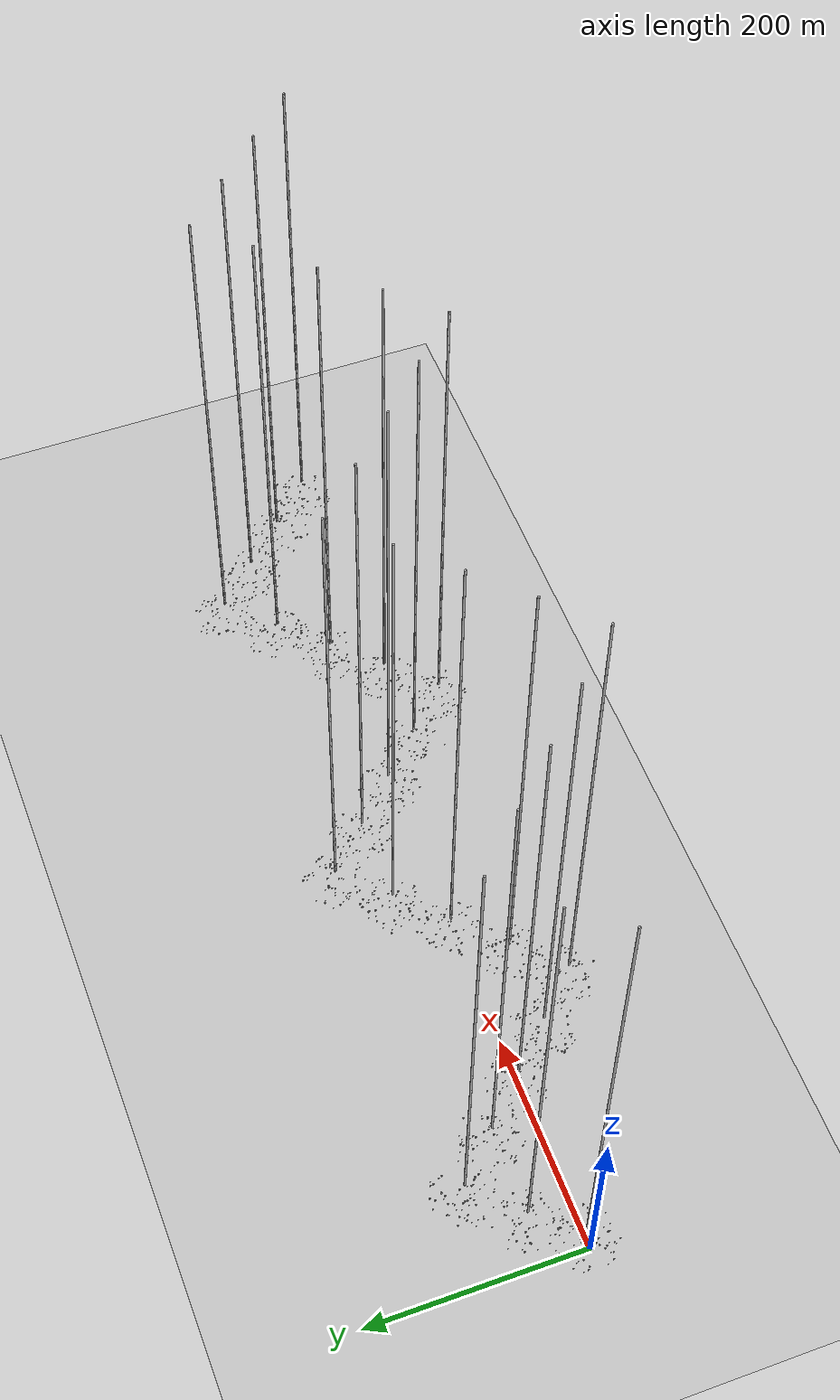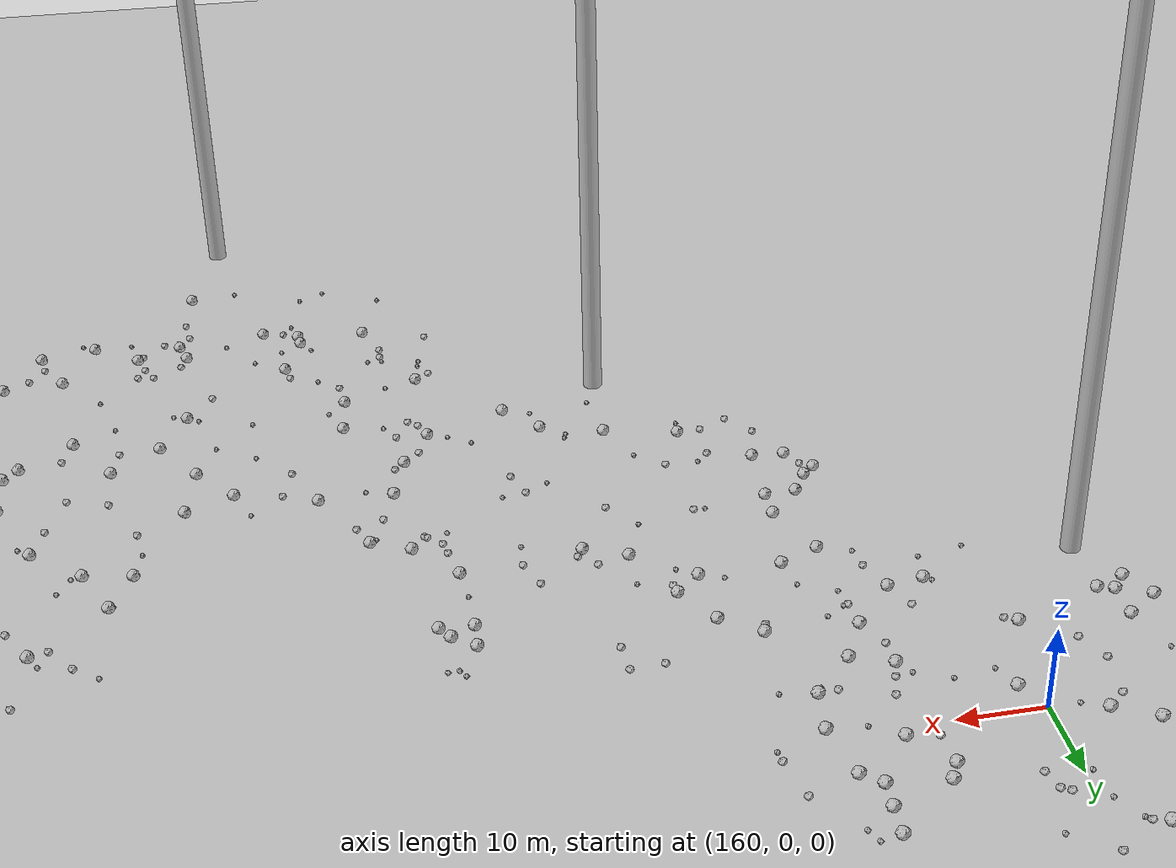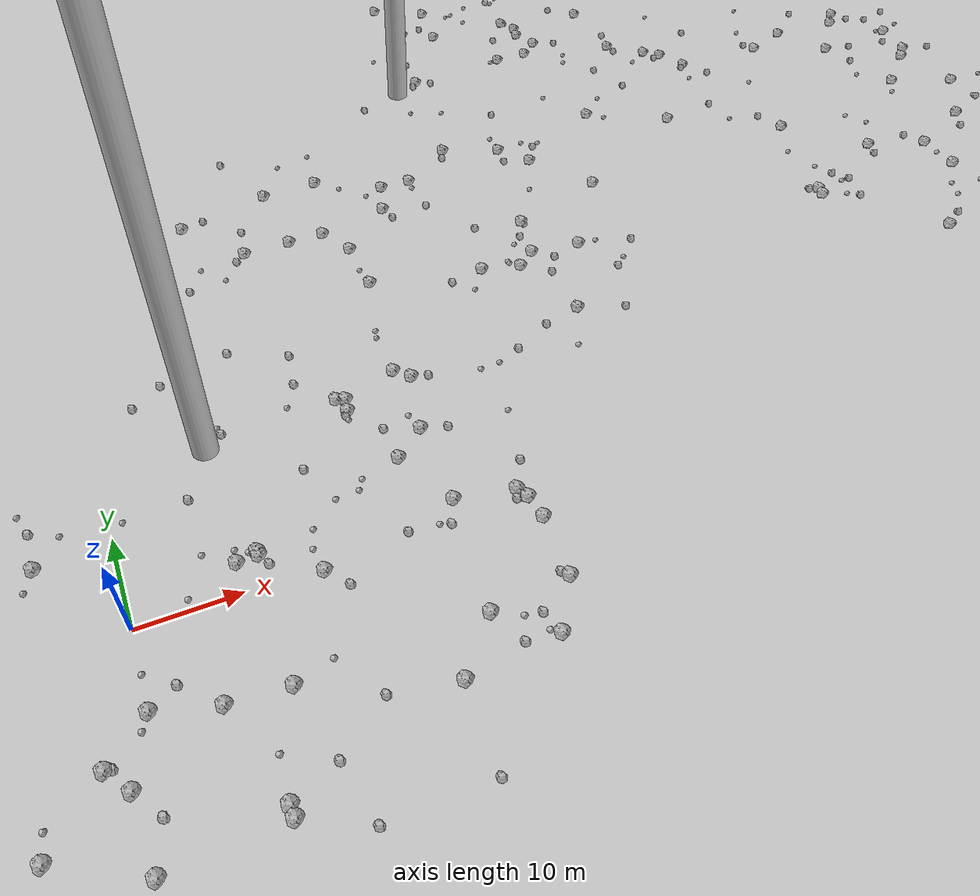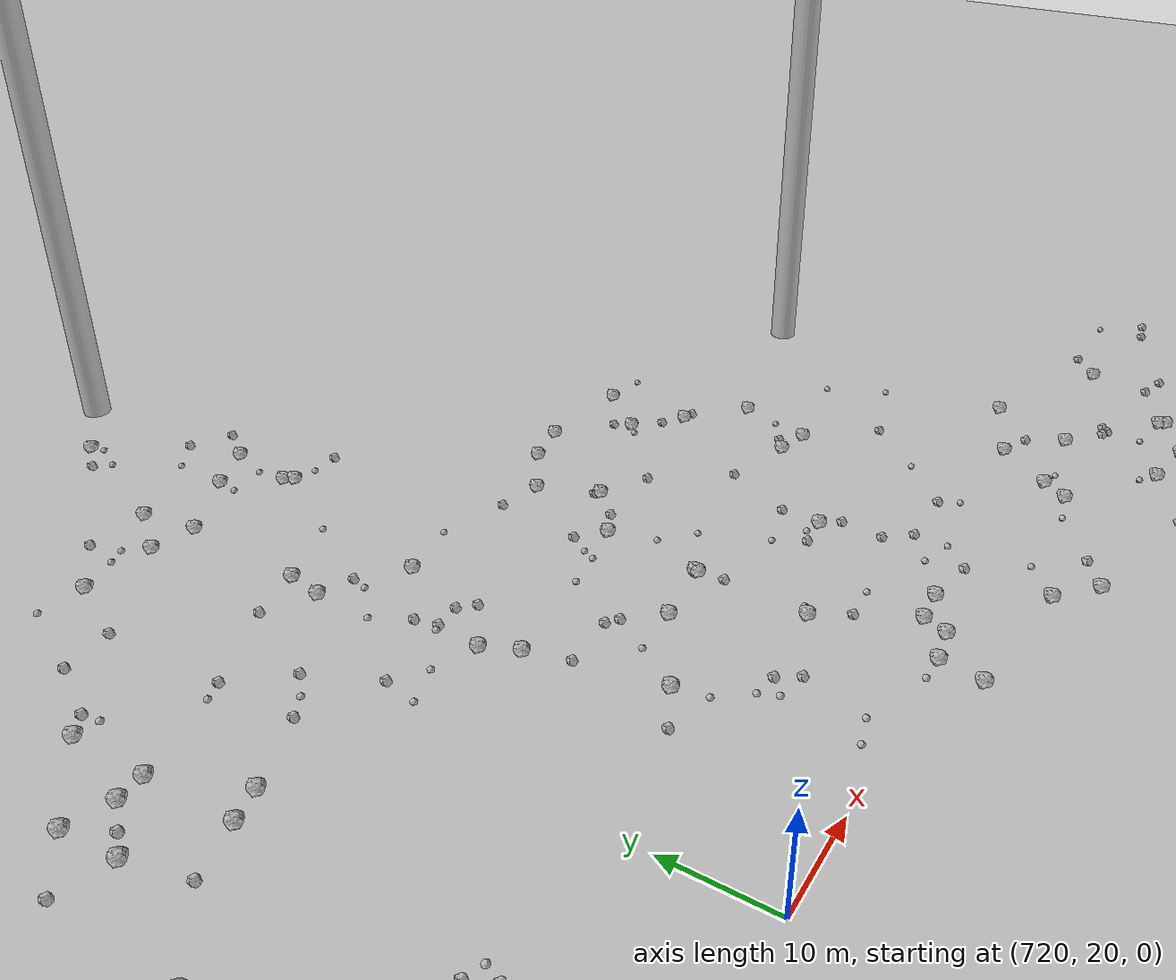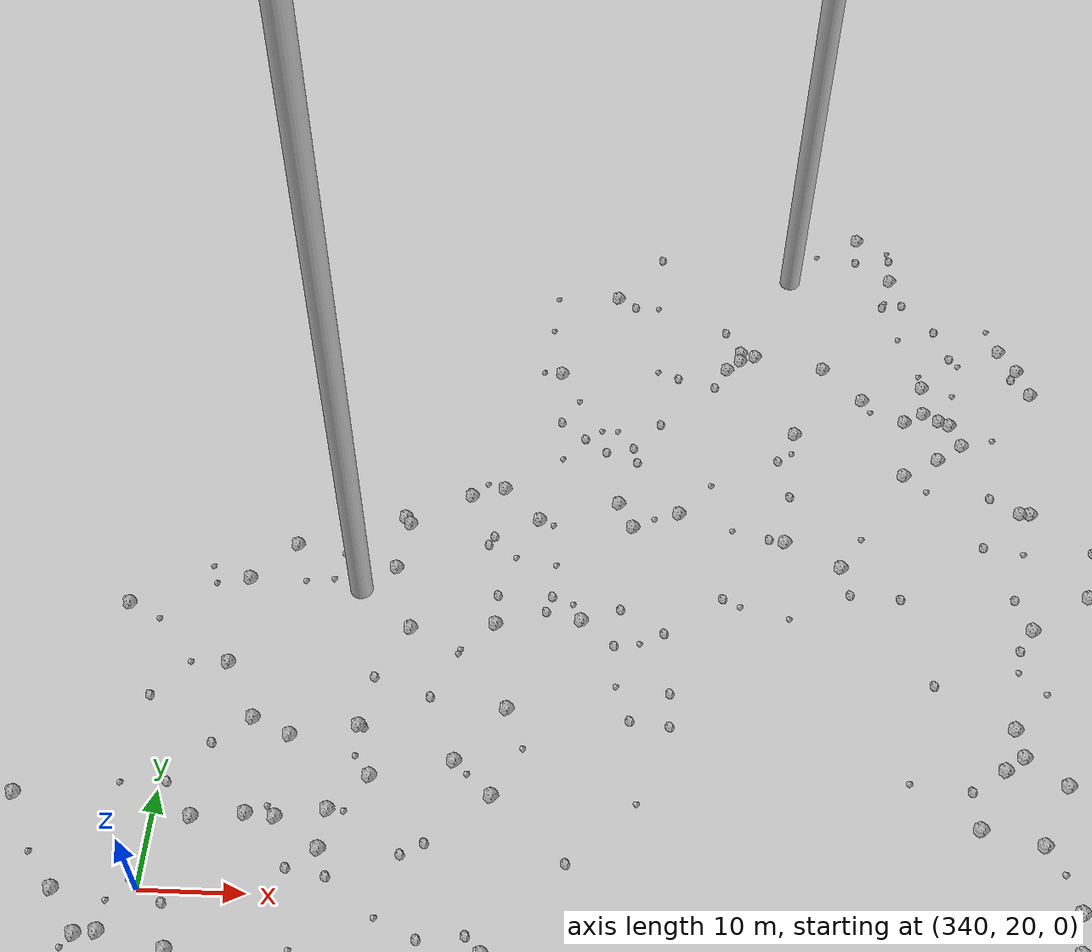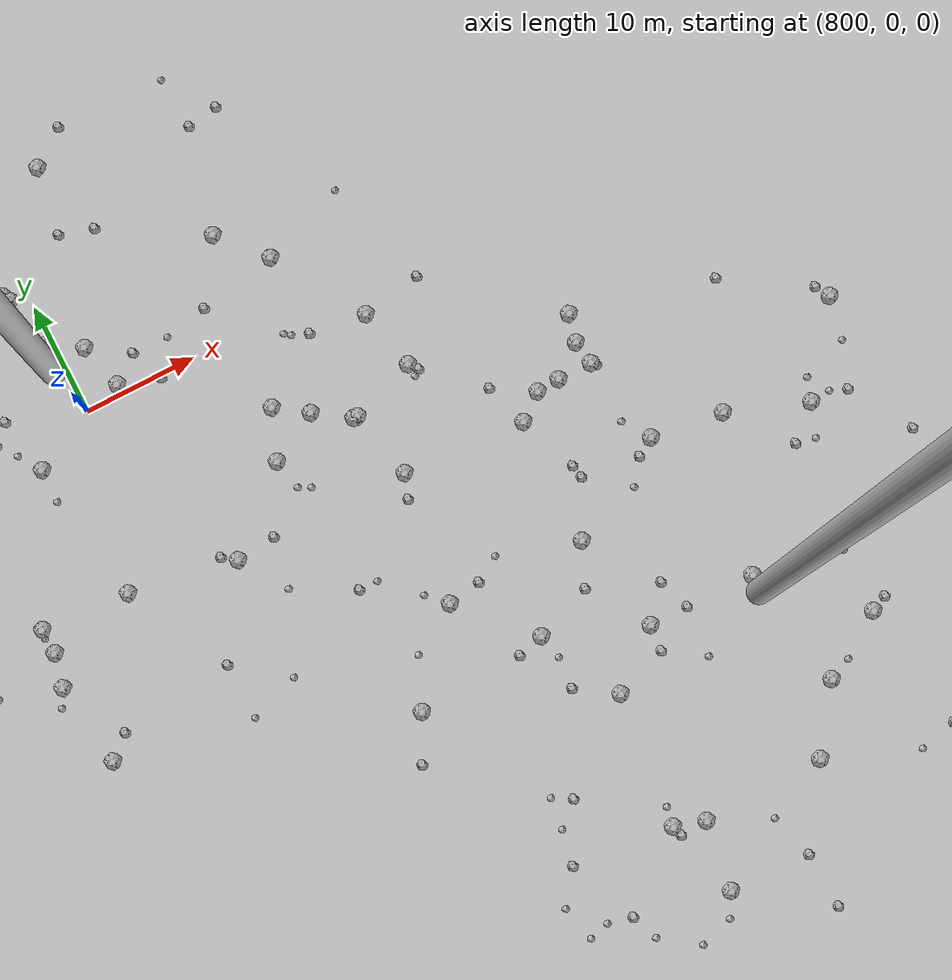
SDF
<sdf version="1.6">
 <world name="default">
  <include><uri>model://custom_ground</uri></include>
  <include><uri>model://sun</uri></include>
  <spherical_coordinates>
   <surface_model>EARTH_WGS84</surface_model>
   <latitude_deg>38.161479</latitude_deg>
   <longitude_deg>-122.454630</longitude_deg>
   <elevation>488.0</elevation>
   <heading_deg>90</heading_deg>
  </spherical_coordinates>
  <model name="rock1_0_0">
   <include><uri>model://rock1</uri><pose>5.771079493146271 -9.819357065651012 0.5 0 0 0</pose></include>
  </model>
  <model name="rock1_0_1">
   <include><uri>model://rock1</uri><pose>-2.4612866904050428 -13.996237861679322 0.5 0 0 0</pose></include>
  </model>
  <model name="rock1_0_2">
   <include><uri>model://rock1</uri><pose>36.985138393442405 1.0681095417302835 0.5 0 0 0</pose></include>
  </model>
  <model name="rock1_0_3">
   <include><uri>model://rock1</uri><pose>10.048795077405583 2.964165694412273 0.5 0 0 0</pose></include>
  </model>
  <model name="rock1_0_4">
   <include><uri>model://rock1</uri><pose>8.486551937444588 -19.46444843012776 0.5 0 0 0</pose></include>
  </model>
  <model name="rock1_0_5">
   <include><uri>model://rock1</uri><pose>37.61261482613806 -0.20267908136619894 0.5 0 0 0</pose></include>
  </model>
  <model name="rock1_0_6">
   <include><uri>model://rock1</uri><pose>12.118830410630451 3.055511634601544 0.5 0 0 0</pose></include>
  </model>
  <model name="rock1_0_7">
   <include><uri>model://rock1</uri><pose>-0.25942421664873905 -26.884336957633725 0.5 0 0 0</pose></include>
  </model>
  <model name="rock1_0_8">
   <include><uri>model://rock1</uri><pose>-16.4514751585276 8.43695050223856 0.5 0 0 0</pose></include>
  </model>
  <model name="rock1_0_9">
   <include><uri>model://rock1</uri><pose>-0.053720074185065414 -8.090334665398736 0.5 0 0 0</pose></include>
  </model>
  <model name="rock1_0_10">
   <include><uri>model://rock1</uri><pose>-7.0837236879827365 9.100488952114972 0.5 0 0 0</pose></include>
  </model>
  <model name="rock1_0_11">
   <include><uri>model://rock1</uri><pose>17.169204407424907 -0.7466109547467568 0.5 0 0 0</pose></include>
  </model>
  <model name="rock1_0_12">
   <include><uri>model://rock1</uri><pose>29.23358540086545 -10.208720388582055 0.5 0 0 0</pose></include>
  </model>
  <model name="rock1_0_13">
   <include><uri>model://rock1</uri><pose>12.058977014299415 3.48241184290449 0.5 0 0 0</pose></include>
  </model>
  <model name="rock1_0_14">
   <include><uri>model://rock1</uri><pose>-14.298259528149014 6.763482802699436 0.5 0 0 0</pose></include>
  </model>
  <model name="rock1_0_15">
   <include><uri>model://rock1</uri><pose>24.753520587321518 -15.1475804853564 0.5 0 0 0</pose></include>
  </model>
  <model name="rock1_0_16">
   <include><uri>model://rock1</uri><pose>-15.022272744730262 -14.593059945984567 0.5 0 0 0</pose></include>
  </model>
  <model name="rock1_0_17">
   <include><uri>model://rock1</uri><pose>37.94356740712384 -2.8302228001194614 0.5 0 0 0</pose></include>
  </model>
  <model name="rock1_0_18">
   <include><uri>model://rock1</uri><pose>8.53937465269518 -20.58841144606827 0.5 0 0 0</pose></include>
  </model>
  <model name="rock1_0_19">
   <include><uri>model://rock1</uri><pose>-1.9562288233087628 -20.901819445603895 0.5 0 0 0</pose></include>
  </model>
  <model name="rock1_0_20">
   <include><uri>model://rock1</uri><pose>37.336657658712475 -9.456053552553655 0.5 0 0 0</pose></include>
  </model>
  <model name="rock1_0_21">
   <include><uri>model://rock1</uri><pose>27.815892051625454 8.796359596386488 0.5 0 0 0</pose></include>
  </model>
  <model name="rock1_0_22">
   <include><uri>model://rock1</uri><pose>34.12363646416154 -14.290007717067683 0.5 0 0 0</pose></include>
  </model>
  <model name="rock1_0_23">
   <include><uri>model://rock1</uri><pose>-4.201134541332083 -11.614262421315978 0.5 0 0 0</pose></include>
  </model>
  <model name="rock1_0_24">
   <include><uri>model://rock1</uri><pose>-9.520718336758359 -16.848834644733778 0.5 0 0 0</pose></include>
  </model>
  <model name="rock1_0_25">
   <include><uri>model://rock1</uri><pose>11.505831305176017 -10.292900423176206 0.5 0 0 0</pose></include>
  </model>
  <model name="rock1_0_26">
   <include><uri>model://rock1</uri><pose>30.890108389444933 2.1822770263824367 0.5 0 0 0</pose></include>
  </model>
  <model name="rock2_0_0">
   <include><uri>model://rock2</uri><pose>36.75452826203608 -8.71694973676739 0.3 0 0 0</pose></include>
  </model>
  <model name="rock2_0_1">
   <include><uri>model://rock2</uri><pose>18.845919006015144 -2.874635789537013 0.3 0 0 0</pose></include>
  </model>
  <model name="rock2_0_2">
   <include><uri>model://rock2</uri><pose>36.50875118751303 0.07579263480426235 0.3 0 0 0</pose></include>
  </model>
  <model name="rock2_0_3">
   <include><uri>model://rock2</uri><pose>29.648643874318047 -0.28101768252950166 0.3 0 0 0</pose></include>
  </model>
  <model name="rock2_0_4">
   <include><uri>model://rock2</uri><pose>-7.100849774027374 13.310976714243047 0.3 0 0 0</pose></include>
  </model>
  <model name="rock2_0_5">
   <include><uri>model://rock2</uri><pose>12.334452939071454 18.44817790222745 0.3 0 0 0</pose></include>
  </model>
  <model name="rock2_0_6">
   <include><uri>model://rock2</uri><pose>7.489600410727853 11.638725358525761 0.3 0 0 0</pose></include>
  </model>
  <model name="rock2_0_7">
   <include><uri>model://rock2</uri><pose>-0.6482757795080047 -16.753241077005903 0.3 0 0 0</pose></include>
  </model>
  <model name="rock2_0_8">
   <include><uri>model://rock2</uri><pose>21.727939803020178 26.43283768588867 0.3 0 0 0</pose></include>
  </model>
  <model name="rock2_0_9">
   <include><uri>model://rock2</uri><pose>18.712546289747927 11.009290664880204 0.3 0 0 0</pose></include>
  </model>
  <model name="rock2_0_10">
   <include><uri>model://rock2</uri><pose>4.661772898698139 25.15558167487726 0.3 0 0 0</pose></include>
  </model>
  <model name="rock2_0_11">
   <include><uri>model://rock2</uri><pose>18.2300358410223 -13.865211978134258 0.3 0 0 0</pose></include>
  </model>
  <model name="rock2_0_12">
   <include><uri>model://rock2</uri><pose>12.997203176114077 -17.63209554636836 0.3 0 0 0</pose></include>
  </model>
  <model name="rock2_0_13">
   <include><uri>model://rock2</uri><pose>14.207515955632125 -23.45207866706702 0.3 0 0 0</pose></include>
  </model>
  <model name="rock2_0_14">
   <include><uri>model://rock2</uri><pose>-11.338271015300743 19.615290800388976 0.3 0 0 0</pose></include>
  </model>
  <model name="rock2_0_15">
   <include><uri>model://rock2</uri><pose>25.591239246778365 0.39410615585265063 0.3 0 0 0</pose></include>
  </model>
  <model name="rock2_0_16">
   <include><uri>model://rock2</uri><pose>33.48041887402398 -11.830657898177112 0.3 0 0 0</pose></include>
  </model>
  <model name="rock2_0_17">
   <include><uri>model://rock2</uri><pose>2.529741784028687 -6.575130743815489 0.3 0 0 0</pose></include>
  </model>
  <model name="rock2_0_18">
   <include><uri>model://rock2</uri><pose>33.8564674563835 10.830129794093708 0.3 0 0 0</pose></include>
  </model>
  <model name="rock2_0_19">
   <include><uri>model://rock2</uri><pose>-16.79588912672681 -2.840633547955939 0.3 0 0 0</pose></include>
  </model>
  <model name="rock2_0_20">
   <include><uri>model://rock2</uri><pose>38.77200022647508 4.182883179168613 0.3 0 0 0</pose></include>
  </model>
  <model name="rock2_0_21">
   <include><uri>model://rock2</uri><pose>7.9766263881879205 27.276403354317026 0.3 0 0 0</pose></include>
  </model>
  <model name="rock2_0_22">
   <include><uri>model://rock2</uri><pose>30.82738978519425 -13.822941380704957 0.3 0 0 0</pose></include>
  </model>
  <model name="rock2_0_23">
   <include><uri>model://rock2</uri><pose>24.18083495290469 -23.573466693524985 0.3 0 0 0</pose></include>
  </model>
  <model name="rock2_0_24">
   <include><uri>model://rock2</uri><pose>12.73416419678329 1.8926628384261193 0.3 0 0 0</pose></include>
  </model>
  <model name="rock2_0_25">
   <include><uri>model://rock2</uri><pose>-3.6276049795563026 -11.627921909339982 0.3 0 0 0</pose></include>
  </model>
  <model name="rock2_0_26">
   <include><uri>model://rock2</uri><pose>-3.421217579666763 -22.145819294265046 0.3 0 0 0</pose></include>
  </model>
  <model name="rock3_0_0">
   <include><uri>model://rock3</uri><pose>31.84902953128693 -11.537268569450728 0.2 0 0 0</pose></include>
  </model>
  <model name="rock3_0_1">
   <include><uri>model://rock3</uri><pose>-0.924309781867727 -9.482891123642286 0.2 0 0 0</pose></include>
  </model>
  <model name="rock3_0_2">
   <include><uri>model://rock3</uri><pose>15.28409374666085 -9.150784119863964 0.2 0 0 0</pose></include>
  </model>
  <model name="rock3_0_3">
   <include><uri>model://rock3</uri><pose>-17.169247294401437 12.624495429024911 0.2 0 0 0</pose></include>
  </model>
  <model name="rock3_0_4">
   <include><uri>model://rock3</uri><pose>10.173097122596946 4.48150940751561 0.2 0 0 0</pose></include>
  </model>
  <model name="rock3_0_5">
   <include><uri>model://rock3</uri><pose>12.128260634983086 19.347315704432525 0.2 0 0 0</pose></include>
  </model>
  <model name="rock3_0_6">
   <include><uri>model://rock3</uri><pose>22.92888021927402 6.604111257474479 0.2 0 0 0</pose></include>
  </model>
  <model name="rock3_0_7">
   <include><uri>model://rock3</uri><pose>-7.857613110841161 15.63376888656449 0.2 0 0 0</pose></include>
  </model>
  <model name="rock3_0_8">
   <include><uri>model://rock3</uri><pose>-17.78611720925753 -8.677737041944894 0.2 0 0 0</pose></include>
  </model>
  <model name="rock3_0_9">
   <include><uri>model://rock3</uri><pose>-0.0008432473640205274 -4.558166511008107 0.2 0 0 0</pose></include>
  </model>
  <model name="rock3_0_10">
   <include><uri>model://rock3</uri><pose>33.31756683790349 -13.616653802878261 0.2 0 0 0</pose></include>
  </model>
  <model name="rock3_0_11">
   <include><uri>model://rock3</uri><pose>11.302791354120796 3.782203305118678 0.2 0 0 0</pose></include>
  </model>
  <model name="rock3_0_12">
   <include><uri>model://rock3</uri><pose>-9.222504575251815 -14.449391005344797 0.2 0 0 0</pose></include>
  </model>
  <model name="rock3_0_13">
   <include><uri>model://rock3</uri><pose>23.63644895614101 7.787942309689491 0.2 0 0 0</pose></include>
  </model>
  <model name="rock3_0_14">
   <include><uri>model://rock3</uri><pose>7.260186804558877 5.055010988613887 0.2 0 0 0</pose></include>
  </model>
  <model name="rock3_0_15">
   <include><uri>model://rock3</uri><pose>-8.227409963616719 7.063497051804276 0.2 0 0 0</pose></include>
  </model>
  <model name="rock3_0_16">
   <include><uri>model://rock3</uri><pose>30.671735748605272 13.690573636682466 0.2 0 0 0</pose></include>
  </model>
  <model name="rock3_0_17">
   <include><uri>model://rock3</uri><pose>8.766523455345066 -15.36896688980929 0.2 0 0 0</pose></include>
  </model>
  <model name="rock3_0_18">
   <include><uri>model://rock3</uri><pose>17.51385259382092 3.9495512704524884 0.2 0 0 0</pose></include>
  </model>
  <model name="rock3_0_19">
   <include><uri>model://rock3</uri><pose>25.040869326638827 17.658900529023825 0.2 0 0 0</pose></include>
  </model>
  <model name="rock3_0_20">
   <include><uri>model://rock3</uri><pose>20.514582298173075 6.4448257024625235 0.2 0 0 0</pose></include>
  </model>
  <model name="rock3_0_21">
   <include><uri>model://rock3</uri><pose>5.1388590221108 0.99715051094838 0.2 0 0 0</pose></include>
  </model>
  <model name="rock3_0_22">
   <include><uri>model://rock3</uri><pose>16.84362449520622 1.8839430328458917 0.2 0 0 0</pose></include>
  </model>
  <model name="rock3_0_23">
   <include><uri>model://rock3</uri><pose>-4.43713914600967 12.017691663422326 0.2 0 0 0</pose></include>
  </model>
  <model name="rock3_0_24">
   <include><uri>model://rock3</uri><pose>11.43998164277588 24.645480449742564 0.2 0 0 0</pose></include>
  </model>
  <model name="rock3_0_25">
   <include><uri>model://rock3</uri><pose>1.233569429075878 11.366454357877103 0.2 0 0 0</pose></include>
  </model>
  <model name="rock3_0_26">
   <include><uri>model://rock3</uri><pose>28.618571652127763 0.057948078994826346 0.2 0 0 0</pose></include>
  </model>
  <model name="rock1_1_0">
   <include><uri>model://rock1</uri><pose>33.520639500289796 54.945637662930544 0.5 0 0 0</pose></include>
  </model>
  <model name="rock1_1_1">
   <include><uri>model://rock1</uri><pose>54.74829157473954 37.813078427312725 0.5 0 0 0</pose></include>
  </model>
  <model name="rock1_1_2">
   <include><uri>model://rock1</uri><pose>26.711169367239204 54.63567444434987 0.5 0 0 0</pose></include>
  </model>
  <model name="rock1_1_3">
   <include><uri>model://rock1</uri><pose>51.1888843530477 30.34975068632231 0.5 0 0 0</pose></include>
  </model>
  <model name="rock1_1_4">
   <include><uri>model://rock1</uri><pose>21.61415684179096 44.635948503750384 0.5 0 0 0</pose></include>
  </model>
  <model name="rock1_1_5">
   <include><uri>model://rock1</uri><pose>51.47725866461011 55.460741164675525 0.5 0 0 0</pose></include>
  </model>
  <model name="rock1_1_6">
   <include><uri>model://rock1</uri><pose>25.098492954862206 16.48540043150706 0.5 0 0 0</pose></include>
  </model>
  <model name="rock1_1_7">
   <include><uri>model://rock1</uri><pose>31.373906877275772 20.029127331004442 0.5 0 0 0</pose></include>
  </model>
  <model name="rock1_1_8">
   <include><uri>model://rock1</uri><pose>61.2443153335247 49.06149193072953 0.5 0 0 0</pose></include>
  </model>
  <model name="rock1_1_9">
   <include><uri>model://rock1</uri><pose>44.91695082215825 50.81113630850751 0.5 0 0 0</pose></include>
  </model>
  <model name="rock1_1_10">
   <include><uri>model://rock1</uri><pose>53.5059482352391 32.15993759346304 0.5 0 0 0</pose></include>
  </model>
  <model name="rock1_1_11">
   <include><uri>model://rock1</uri><pose>31.378364890896542 44.76430813130789 0.5 0 0 0</pose></include>
  </model>
  <model name="rock1_1_12">
   <include><uri>model://rock1</uri><pose>31.19688554812845 11.54417871471912 0.5 0 0 0</pose></include>
  </model>
  <model name="rock1_1_13">
   <include><uri>model://rock1</uri><pose>58.38183281917656 52.75599548074349 0.5 0 0 0</pose></include>
  </model>
  <model name="rock1_1_14">
   <include><uri>model://rock1</uri><pose>25.404439733835247 18.054630187403507 0.5 0 0 0</pose></include>
  </model>
  <model name="rock1_1_15">
   <include><uri>model://rock1</uri><pose>46.702515460808115 31.4730526957405 0.5 0 0 0</pose></include>
  </model>
  <model name="rock1_1_16">
   <include><uri>model://rock1</uri><pose>15.714415151436192 51.98209683413826 0.5 0 0 0</pose></include>
  </model>
  <model name="rock1_1_17">
   <include><uri>model://rock1</uri><pose>33.74172053996963 34.18934749983809 0.5 0 0 0</pose></include>
  </model>
  <model name="rock1_1_18">
   <include><uri>model://rock1</uri><pose>66.66636342844606 41.586491179110794 0.5 0 0 0</pose></include>
  </model>
  <model name="rock1_1_19">
   <include><uri>model://rock1</uri><pose>32.869668641758324 18.539136436411376 0.5 0 0 0</pose></include>
  </model>
  <model name="rock1_1_20">
   <include><uri>model://rock1</uri><pose>24.479201075044188 18.386122393280314 0.5 0 0 0</pose></include>
  </model>
  <model name="rock1_1_21">
   <include><uri>model://rock1</uri><pose>54.09508257308157 21.46157587969597 0.5 0 0 0</pose></include>
  </model>
  <model name="rock1_1_22">
   <include><uri>model://rock1</uri><pose>59.38913654557518 31.456002035630128 0.5 0 0 0</pose></include>
  </model>
  <model name="rock1_1_23">
   <include><uri>model://rock1</uri><pose>27.162897093785354 44.712344953453375 0.5 0 0 0</pose></include>
  </model>
  <model name="rock1_1_24">
   <include><uri>model://rock1</uri><pose>41.14971361410906 50.81554694081131 0.5 0 0 0</pose></include>
  </model>
  <model name="rock1_1_25">
   <include><uri>model://rock1</uri><pose>33.51475420840387 40.78757557635788 0.5 0 0 0</pose></include>
  </model>
  <model name="rock1_1_26">
   <include><uri>model://rock1</uri><pose>39.79277934842389 46.59136812003474 0.5 0 0 0</pose></include>
  </model>
  <model name="rock2_1_0">
   <include><uri>model://rock2</uri><pose>21.009750813803617 22.266229340815347 0.3 0 0 0</pose></include>
  </model>
  <model name="rock2_1_1">
   <include><uri>model://rock2</uri><pose>65.71333381546924 29.983618323124865 0.3 0 0 0</pose></include>
  </model>
  <model name="rock2_1_2">
   <include><uri>model://rock2</uri><pose>55.638453371387946 30.514923018580667 0.3 0 0 0</pose></include>
  </model>
  <model name="rock2_1_3">
   <include><uri>model://rock2</uri><pose>14.10823473462775 40.59574760872878 0.3 0 0 0</pose></include>
  </model>
  <model name="rock2_1_4">
   <include><uri>model://rock2</uri><pose>53.42484193351382 35.437442705536114 0.3 0 0 0</pose></include>
  </model>
  <model name="rock2_1_5">
   <include><uri>model://rock2</uri><pose>58.08443223612627 50.326594783306675 0.3 0 0 0</pose></include>
  </model>
  <model name="rock2_1_6">
   <include><uri>model://rock2</uri><pose>48.96225928700906 38.93366775583021 0.3 0 0 0</pose></include>
  </model>
  <model name="rock2_1_7">
   <include><uri>model://rock2</uri><pose>27.67186796326823 12.95648055096329 0.3 0 0 0</pose></include>
  </model>
  <model name="rock2_1_8">
   <include><uri>model://rock2</uri><pose>54.89447496994159 37.53199992888979 0.3 0 0 0</pose></include>
  </model>
  <model name="rock2_1_9">
   <include><uri>model://rock2</uri><pose>20.374504233039705 43.712759512902444 0.3 0 0 0</pose></include>
  </model>
  <model name="rock2_1_10">
   <include><uri>model://rock2</uri><pose>54.17042225303059 28.171286387259073 0.3 0 0 0</pose></include>
  </model>
  <model name="rock2_1_11">
   <include><uri>model://rock2</uri><pose>42.6213973621285 30.764320453943398 0.3 0 0 0</pose></include>
  </model>
  <model name="rock2_1_12">
   <include><uri>model://rock2</uri><pose>23.18573503533996 63.48222252423776 0.3 0 0 0</pose></include>
  </model>
  <model name="rock2_1_13">
   <include><uri>model://rock2</uri><pose>45.1578554415558 18.175932170383827 0.3 0 0 0</pose></include>
  </model>
  <model name="rock2_1_14">
   <include><uri>model://rock2</uri><pose>59.300761607301226 19.774463832962514 0.3 0 0 0</pose></include>
  </model>
  <model name="rock2_1_15">
   <include><uri>model://rock2</uri><pose>63.037937531098585 51.99126271061628 0.3 0 0 0</pose></include>
  </model>
  <model name="rock2_1_16">
   <include><uri>model://rock2</uri><pose>24.730273662823727 16.03705258442966 0.3 0 0 0</pose></include>
  </model>
  <model name="rock2_1_17">
   <include><uri>model://rock2</uri><pose>34.64060910270528 18.18631154955733 0.3 0 0 0</pose></include>
  </model>
  <model name="rock2_1_18">
   <include><uri>model://rock2</uri><pose>45.11726038119921 45.41192096612794 0.3 0 0 0</pose></include>
  </model>
  <model name="rock2_1_19">
   <include><uri>model://rock2</uri><pose>40.386705187464 44.744764879501105 0.3 0 0 0</pose></include>
  </model>
  <model name="rock2_1_20">
   <include><uri>model://rock2</uri><pose>18.404199433787205 52.701411166373376 0.3 0 0 0</pose></include>
  </model>
  <model name="rock2_1_21">
   <include><uri>model://rock2</uri><pose>22.277258905410605 48.902159314007626 0.3 0 0 0</pose></include>
  </model>
  <model name="rock2_1_22">
   <include><uri>model://rock2</uri><pose>50.76888855490093 54.026004399014404 0.3 0 0 0</pose></include>
  </model>
  <model name="rock2_1_23">
   <include><uri>model://rock2</uri><pose>15.614074350840285 29.308878507850565 0.3 0 0 0</pose></include>
  </model>
  <model name="rock2_1_24">
   <include><uri>model://rock2</uri><pose>45.06005329412517 68.76932629650904 0.3 0 0 0</pose></include>
  </model>
  <model name="rock2_1_25">
   <include><uri>model://rock2</uri><pose>61.909591396748816 26.273813898752866 0.3 0 0 0</pose></include>
  </model>
  <model name="rock2_1_26">
   <include><uri>model://rock2</uri><pose>49.66384997413876 20.465674397863754 0.3 0 0 0</pose></include>
  </model>
  <model name="rock3_1_0">
   <include><uri>model://rock3</uri><pose>38.79137903087861 50.104295968305614 0.2 0 0 0</pose></include>
  </model>
  <model name="rock3_1_1">
   <include><uri>model://rock3</uri><pose>44.795055469946846 49.502656908537645 0.2 0 0 0</pose></include>
  </model>
  <model name="rock3_1_2">
   <include><uri>model://rock3</uri><pose>36.071800701574105 52.836798065104 0.2 0 0 0</pose></include>
  </model>
  <model name="rock3_1_3">
   <include><uri>model://rock3</uri><pose>40.41017973729993 10.521633164880328 0.2 0 0 0</pose></include>
  </model>
  <model name="rock3_1_4">
   <include><uri>model://rock3</uri><pose>18.44353406477851 41.05582326119365 0.2 0 0 0</pose></include>
  </model>
  <model name="rock3_1_5">
   <include><uri>model://rock3</uri><pose>50.13007520509077 31.785409747600156 0.2 0 0 0</pose></include>
  </model>
  <model name="rock3_1_6">
   <include><uri>model://rock3</uri><pose>51.528777407966935 16.27116602333576 0.2 0 0 0</pose></include>
  </model>
  <model name="rock3_1_7">
   <include><uri>model://rock3</uri><pose>50.21312070348267 31.450369021366612 0.2 0 0 0</pose></include>
  </model>
  <model name="rock3_1_8">
   <include><uri>model://rock3</uri><pose>30.021348025754495 60.185645986812546 0.2 0 0 0</pose></include>
  </model>
  <model name="rock3_1_9">
   <include><uri>model://rock3</uri><pose>40.175135368690086 16.911913906526095 0.2 0 0 0</pose></include>
  </model>
  <model name="rock3_1_10">
   <include><uri>model://rock3</uri><pose>34.326813559532255 61.11886519165396 0.2 0 0 0</pose></include>
  </model>
  <model name="rock3_1_11">
   <include><uri>model://rock3</uri><pose>44.62653630643428 28.713197385129565 0.2 0 0 0</pose></include>
  </model>
  <model name="rock3_1_12">
   <include><uri>model://rock3</uri><pose>58.630117572124014 43.59331979495525 0.2 0 0 0</pose></include>
  </model>
  <model name="rock3_1_13">
   <include><uri>model://rock3</uri><pose>31.416936169039435 25.50485429772337 0.2 0 0 0</pose></include>
  </model>
  <model name="rock3_1_14">
   <include><uri>model://rock3</uri><pose>24.82968347503433 15.422925884540753 0.2 0 0 0</pose></include>
  </model>
  <model name="rock3_1_15">
   <include><uri>model://rock3</uri><pose>42.4106222985411 17.044437234170786 0.2 0 0 0</pose></include>
  </model>
  <model name="rock3_1_16">
   <include><uri>model://rock3</uri><pose>19.467639491993683 19.34557081951695 0.2 0 0 0</pose></include>
  </model>
  <model name="rock3_1_17">
   <include><uri>model://rock3</uri><pose>50.81211234487475 65.68872350132955 0.2 0 0 0</pose></include>
  </model>
  <model name="rock3_1_18">
   <include><uri>model://rock3</uri><pose>31.69831963819327 26.59112074703724 0.2 0 0 0</pose></include>
  </model>
  <model name="rock3_1_19">
   <include><uri>model://rock3</uri><pose>61.65105632157461 31.417624269315432 0.2 0 0 0</pose></include>
  </model>
  <model name="rock3_1_20">
   <include><uri>model://rock3</uri><pose>16.129614029743383 43.78298720538682 0.2 0 0 0</pose></include>
  </model>
  <model name="rock3_1_21">
   <include><uri>model://rock3</uri><pose>33.37638880155781 36.883151922255834 0.2 0 0 0</pose></include>
  </model>
  <model name="rock3_1_22">
   <include><uri>model://rock3</uri><pose>64.1045533108299 52.56746923995035 0.2 0 0 0</pose></include>
  </model>
  <model name="rock3_1_23">
   <include><uri>model://rock3</uri><pose>58.48288531830285 55.74543671488377 0.2 0 0 0</pose></include>
  </model>
  <model name="rock3_1_24">
   <include><uri>model://rock3</uri><pose>52.2121534525956 34.346517913847194 0.2 0 0 0</pose></include>
  </model>
  <model name="rock3_1_25">
   <include><uri>model://rock3</uri><pose>63.29906533765314 27.428181149027097 0.2 0 0 0</pose></include>
  </model>
  <model name="rock3_1_26">
   <include><uri>model://rock3</uri><pose>61.99972515934554 53.36036717774298 0.2 0 0 0</pose></include>
  </model>
  <model name="rock1_2_0">
   <include><uri>model://rock1</uri><pose>61.53259778842083 83.77525383133852 0.5 0 0 0</pose></include>
  </model>
  <model name="rock1_2_1">
   <include><uri>model://rock1</uri><pose>83.24959020583404 50.82494009811106 0.5 0 0 0</pose></include>
  </model>
  <model name="rock1_2_2">
   <include><uri>model://rock1</uri><pose>54.297841156828895 72.63943161371775 0.5 0 0 0</pose></include>
  </model>
  <model name="rock1_2_3">
   <include><uri>model://rock1</uri><pose>84.88762264317953 71.33700352810916 0.5 0 0 0</pose></include>
  </model>
  <model name="rock1_2_4">
   <include><uri>model://rock1</uri><pose>83.96320207445663 95.56348609868076 0.5 0 0 0</pose></include>
  </model>
  <model name="rock1_2_5">
   <include><uri>model://rock1</uri><pose>83.24206852769171 104.70699162946794 0.5 0 0 0</pose></include>
  </model>
  <model name="rock1_2_6">
   <include><uri>model://rock1</uri><pose>57.36243347975977 86.20864285533654 0.5 0 0 0</pose></include>
  </model>
  <model name="rock1_2_7">
   <include><uri>model://rock1</uri><pose>72.8650138403664 83.77104504188446 0.5 0 0 0</pose></include>
  </model>
  <model name="rock1_2_8">
   <include><uri>model://rock1</uri><pose>96.87777706045446 101.18200648345744 0.5 0 0 0</pose></include>
  </model>
  <model name="rock1_2_9">
   <include><uri>model://rock1</uri><pose>62.542001337070324 91.17212775698249 0.5 0 0 0</pose></include>
  </model>
  <model name="rock1_2_10">
   <include><uri>model://rock1</uri><pose>90.97322926842196 66.12294404688294 0.5 0 0 0</pose></include>
  </model>
  <model name="rock1_2_11">
   <include><uri>model://rock1</uri><pose>74.04952123543237 81.43546631460097 0.5 0 0 0</pose></include>
  </model>
  <model name="rock1_2_12">
   <include><uri>model://rock1</uri><pose>87.53196904853745 97.38265920719485 0.5 0 0 0</pose></include>
  </model>
  <model name="rock1_2_13">
   <include><uri>model://rock1</uri><pose>84.87912069123945 82.14461872549579 0.5 0 0 0</pose></include>
  </model>
  <model name="rock1_2_14">
   <include><uri>model://rock1</uri><pose>67.73952428558884 99.83659337863023 0.5 0 0 0</pose></include>
  </model>
  <model name="rock1_2_15">
   <include><uri>model://rock1</uri><pose>96.69269063652386 103.60662630393408 0.5 0 0 0</pose></include>
  </model>
  <model name="rock1_2_16">
   <include><uri>model://rock1</uri><pose>101.89048161647978 91.80684320354139 0.5 0 0 0</pose></include>
  </model>
  <model name="rock1_2_17">
   <include><uri>model://rock1</uri><pose>92.73460330703988 62.43647104743001 0.5 0 0 0</pose></include>
  </model>
  <model name="rock1_2_18">
   <include><uri>model://rock1</uri><pose>55.839107163902916 94.75110211145355 0.5 0 0 0</pose></include>
  </model>
  <model name="rock1_2_19">
   <include><uri>model://rock1</uri><pose>86.219008114356 108.38329202765468 0.5 0 0 0</pose></include>
  </model>
  <model name="rock1_2_20">
   <include><uri>model://rock1</uri><pose>74.88513186286387 76.36406330170279 0.5 0 0 0</pose></include>
  </model>
  <model name="rock1_2_21">
   <include><uri>model://rock1</uri><pose>89.09183060706897 67.69762988062479 0.5 0 0 0</pose></include>
  </model>
  <model name="rock1_2_22">
   <include><uri>model://rock1</uri><pose>73.57581967720415 79.58529542051903 0.5 0 0 0</pose></include>
  </model>
  <model name="rock1_2_23">
   <include><uri>model://rock1</uri><pose>73.31055493162327 55.9484996544452 0.5 0 0 0</pose></include>
  </model>
  <model name="rock1_2_24">
   <include><uri>model://rock1</uri><pose>76.7635760443256 95.53147704129887 0.5 0 0 0</pose></include>
  </model>
  <model name="rock1_2_25">
   <include><uri>model://rock1</uri><pose>67.87863776149841 73.94555256181451 0.5 0 0 0</pose></include>
  </model>
  <model name="rock1_2_26">
   <include><uri>model://rock1</uri><pose>72.33281622937022 74.10412507781521 0.5 0 0 0</pose></include>
  </model>
  <model name="rock2_2_0">
   <include><uri>model://rock2</uri><pose>81.72250099388408 60.92785453877795 0.3 0 0 0</pose></include>
  </model>
  <model name="rock2_2_1">
   <include><uri>model://rock2</uri><pose>54.73270086843793 77.81823577473115 0.3 0 0 0</pose></include>
  </model>
  <model name="rock2_2_2">
   <include><uri>model://rock2</uri><pose>81.62888008047116 85.11495013686903 0.3 0 0 0</pose></include>
  </model>
  <model name="rock2_2_3">
   <include><uri>model://rock2</uri><pose>89.82327076475553 65.92095504081423 0.3 0 0 0</pose></include>
  </model>
  <model name="rock2_2_4">
   <include><uri>model://rock2</uri><pose>99.85228292336693 102.33800630959573 0.3 0 0 0</pose></include>
  </model>
  <model name="rock2_2_5">
   <include><uri>model://rock2</uri><pose>75.37023319334739 92.15329977941062 0.3 0 0 0</pose></include>
  </model>
  <model name="rock2_2_6">
   <include><uri>model://rock2</uri><pose>94.98672532875196 59.41031459688839 0.3 0 0 0</pose></include>
  </model>
  <model name="rock2_2_7">
   <include><uri>model://rock2</uri><pose>90.68261521357877 52.045358498313554 0.3 0 0 0</pose></include>
  </model>
  <model name="rock2_2_8">
   <include><uri>model://rock2</uri><pose>88.46922813166108 97.26930618911999 0.3 0 0 0</pose></include>
  </model>
  <model name="rock2_2_9">
   <include><uri>model://rock2</uri><pose>54.7787671413341 83.32000359501113 0.3 0 0 0</pose></include>
  </model>
  <model name="rock2_2_10">
   <include><uri>model://rock2</uri><pose>56.24801783566472 71.9126696162183 0.3 0 0 0</pose></include>
  </model>
  <model name="rock2_2_11">
   <include><uri>model://rock2</uri><pose>85.16698019205012 69.96104903774044 0.3 0 0 0</pose></include>
  </model>
  <model name="rock2_2_12">
   <include><uri>model://rock2</uri><pose>60.35688729837962 87.05636082355778 0.3 0 0 0</pose></include>
  </model>
  <model name="rock2_2_13">
   <include><uri>model://rock2</uri><pose>104.31732429148784 64.01110452857853 0.3 0 0 0</pose></include>
  </model>
  <model name="rock2_2_14">
   <include><uri>model://rock2</uri><pose>79.87680118530999 66.23869133244904 0.3 0 0 0</pose></include>
  </model>
  <model name="rock2_2_15">
   <include><uri>model://rock2</uri><pose>66.7780972167519 98.36631498203234 0.3 0 0 0</pose></include>
  </model>
  <model name="rock2_2_16">
   <include><uri>model://rock2</uri><pose>97.35238074142941 100.39763674254145 0.3 0 0 0</pose></include>
  </model>
  <model name="rock2_2_17">
   <include><uri>model://rock2</uri><pose>92.186282414738 62.07445538043727 0.3 0 0 0</pose></include>
  </model>
  <model name="rock2_2_18">
   <include><uri>model://rock2</uri><pose>100.4011451524523 94.40625951926668 0.3 0 0 0</pose></include>
  </model>
  <model name="rock2_2_19">
   <include><uri>model://rock2</uri><pose>76.39382241520676 109.26939341575678 0.3 0 0 0</pose></include>
  </model>
  <model name="rock2_2_20">
   <include><uri>model://rock2</uri><pose>85.73773058501111 74.74360451526685 0.3 0 0 0</pose></include>
  </model>
  <model name="rock2_2_21">
   <include><uri>model://rock2</uri><pose>69.63045584704572 79.69577586336285 0.3 0 0 0</pose></include>
  </model>
  <model name="rock2_2_22">
   <include><uri>model://rock2</uri><pose>61.046750571075364 61.053984378906655 0.3 0 0 0</pose></include>
  </model>
  <model name="rock2_2_23">
   <include><uri>model://rock2</uri><pose>97.60882829588039 70.8751881614802 0.3 0 0 0</pose></include>
  </model>
  <model name="rock2_2_24">
   <include><uri>model://rock2</uri><pose>73.43179662898191 91.22516576973159 0.3 0 0 0</pose></include>
  </model>
  <model name="rock2_2_25">
   <include><uri>model://rock2</uri><pose>77.8697106245096 75.5202356931045 0.3 0 0 0</pose></include>
  </model>
  <model name="rock2_2_26">
   <include><uri>model://rock2</uri><pose>53.54511015223855 71.9379107697886 0.3 0 0 0</pose></include>
  </model>
  <model name="rock3_2_0">
   <include><uri>model://rock3</uri><pose>91.82762016605656 59.07981290131019 0.2 0 0 0</pose></include>
  </model>
  <model name="rock3_2_1">
   <include><uri>model://rock3</uri><pose>66.75348231401848 74.03996276294123 0.2 0 0 0</pose></include>
  </model>
  <model name="rock3_2_2">
   <include><uri>model://rock3</uri><pose>76.79520671184514 59.28072028563689 0.2 0 0 0</pose></include>
  </model>
  <model name="rock3_2_3">
   <include><uri>model://rock3</uri><pose>74.00883977332688 90.68167094955902 0.2 0 0 0</pose></include>
  </model>
  <model name="rock3_2_4">
   <include><uri>model://rock3</uri><pose>69.71235396062235 62.315615494478195 0.2 0 0 0</pose></include>
  </model>
  <model name="rock3_2_5">
   <include><uri>model://rock3</uri><pose>94.93275249550817 77.39063709718624 0.2 0 0 0</pose></include>
  </model>
  <model name="rock3_2_6">
   <include><uri>model://rock3</uri><pose>66.67046885131882 89.54373594420169 0.2 0 0 0</pose></include>
  </model>
  <model name="rock3_2_7">
   <include><uri>model://rock3</uri><pose>75.33548821511198 54.67328236512178 0.2 0 0 0</pose></include>
  </model>
  <model name="rock3_2_8">
   <include><uri>model://rock3</uri><pose>54.82065015918769 64.1643255298969 0.2 0 0 0</pose></include>
  </model>
  <model name="rock3_2_9">
   <include><uri>model://rock3</uri><pose>86.41319009957341 66.21271707122871 0.2 0 0 0</pose></include>
  </model>
  <model name="rock3_2_10">
   <include><uri>model://rock3</uri><pose>66.92082646161283 95.55780699591568 0.2 0 0 0</pose></include>
  </model>
  <model name="rock3_2_11">
   <include><uri>model://rock3</uri><pose>77.67310664351415 71.86408649335236 0.2 0 0 0</pose></include>
  </model>
  <model name="rock3_2_12">
   <include><uri>model://rock3</uri><pose>85.22231993450214 105.31387179253707 0.2 0 0 0</pose></include>
  </model>
  <model name="rock3_2_13">
   <include><uri>model://rock3</uri><pose>76.73446998762824 69.95155215631816 0.2 0 0 0</pose></include>
  </model>
  <model name="rock3_2_14">
   <include><uri>model://rock3</uri><pose>69.53377707591021 90.96027384521294 0.2 0 0 0</pose></include>
  </model>
  <model name="rock3_2_15">
   <include><uri>model://rock3</uri><pose>67.63173632263815 86.72799866246345 0.2 0 0 0</pose></include>
  </model>
  <model name="rock3_2_16">
   <include><uri>model://rock3</uri><pose>105.5953120606559 67.71939411753273 0.2 0 0 0</pose></include>
  </model>
  <model name="rock3_2_17">
   <include><uri>model://rock3</uri><pose>103.82557126162826 90.36975451079215 0.2 0 0 0</pose></include>
  </model>
  <model name="rock3_2_18">
   <include><uri>model://rock3</uri><pose>72.6168304904595 103.75436845011585 0.2 0 0 0</pose></include>
  </model>
  <model name="rock3_2_19">
   <include><uri>model://rock3</uri><pose>100.69673171430324 95.13401872816851 0.2 0 0 0</pose></include>
  </model>
  <model name="rock3_2_20">
   <include><uri>model://rock3</uri><pose>65.69657696109155 89.26641461903951 0.2 0 0 0</pose></include>
  </model>
  <model name="rock3_2_21">
   <include><uri>model://rock3</uri><pose>109.1418061747126 73.80466757866401 0.2 0 0 0</pose></include>
  </model>
  <model name="rock3_2_22">
   <include><uri>model://rock3</uri><pose>91.88776616835784 91.40495269257056 0.2 0 0 0</pose></include>
  </model>
  <model name="rock3_2_23">
   <include><uri>model://rock3</uri><pose>73.43093505464864 83.73714089111192 0.2 0 0 0</pose></include>
  </model>
  <model name="rock3_2_24">
   <include><uri>model://rock3</uri><pose>50.65614219850903 80.66283063863499 0.2 0 0 0</pose></include>
  </model>
  <model name="rock3_2_25">
   <include><uri>model://rock3</uri><pose>81.69735356265221 97.35035747554716 0.2 0 0 0</pose></include>
  </model>
  <model name="rock3_2_26">
   <include><uri>model://rock3</uri><pose>73.58832753249644 79.91381482005045 0.2 0 0 0</pose></include>
  </model>
  <model name="rock1_3_0">
   <include><uri>model://rock1</uri><pose>92.87310515542443 29.63327935003877 0.5 0 0 0</pose></include>
  </model>
  <model name="rock1_3_1">
   <include><uri>model://rock1</uri><pose>137.24658822125923 36.589705543574965 0.5 0 0 0</pose></include>
  </model>
  <model name="rock1_3_2">
   <include><uri>model://rock1</uri><pose>112.3942174228009 32.895253600897625 0.5 0 0 0</pose></include>
  </model>
  <model name="rock1_3_3">
   <include><uri>model://rock1</uri><pose>126.77541947327275 59.3781118083876 0.5 0 0 0</pose></include>
  </model>
  <model name="rock1_3_4">
   <include><uri>model://rock1</uri><pose>96.72261493970494 43.2519762690808 0.5 0 0 0</pose></include>
  </model>
  <model name="rock1_3_5">
   <include><uri>model://rock1</uri><pose>126.95043938178173 27.77735486741374 0.5 0 0 0</pose></include>
  </model>
  <model name="rock1_3_6">
   <include><uri>model://rock1</uri><pose>121.37559620023956 37.06238909642093 0.5 0 0 0</pose></include>
  </model>
  <model name="rock1_3_7">
   <include><uri>model://rock1</uri><pose>126.61228673041357 44.123322382077404 0.5 0 0 0</pose></include>
  </model>
  <model name="rock1_3_8">
   <include><uri>model://rock1</uri><pose>116.76431626495244 18.8878818121084 0.5 0 0 0</pose></include>
  </model>
  <model name="rock1_3_9">
   <include><uri>model://rock1</uri><pose>115.2460757863652 58.2715505328065 0.5 0 0 0</pose></include>
  </model>
  <model name="rock1_3_10">
   <include><uri>model://rock1</uri><pose>129.21295613137696 37.612178396850126 0.5 0 0 0</pose></include>
  </model>
  <model name="rock1_3_11">
   <include><uri>model://rock1</uri><pose>144.5903261052149 55.698201854738876 0.5 0 0 0</pose></include>
  </model>
  <model name="rock1_3_12">
   <include><uri>model://rock1</uri><pose>132.55801619435334 15.460548609614428 0.5 0 0 0</pose></include>
  </model>
  <model name="rock1_3_13">
   <include><uri>model://rock1</uri><pose>103.36540071216879 17.562183199060687 0.5 0 0 0</pose></include>
  </model>
  <model name="rock1_3_14">
   <include><uri>model://rock1</uri><pose>112.63332748848902 27.701444922115773 0.5 0 0 0</pose></include>
  </model>
  <model name="rock1_3_15">
   <include><uri>model://rock1</uri><pose>118.5312133094142 47.215416034805685 0.5 0 0 0</pose></include>
  </model>
  <model name="rock1_3_16">
   <include><uri>model://rock1</uri><pose>124.42374142580314 52.35230459314074 0.5 0 0 0</pose></include>
  </model>
  <model name="rock1_3_17">
   <include><uri>model://rock1</uri><pose>138.35997575589732 41.090018356694536 0.5 0 0 0</pose></include>
  </model>
  <model name="rock1_3_18">
   <include><uri>model://rock1</uri><pose>105.2340923214185 62.462081514886094 0.5 0 0 0</pose></include>
  </model>
  <model name="rock1_3_19">
   <include><uri>model://rock1</uri><pose>105.02665127572747 35.26156264699994 0.5 0 0 0</pose></include>
  </model>
  <model name="rock1_3_20">
   <include><uri>model://rock1</uri><pose>126.15332536858452 54.11239926504877 0.5 0 0 0</pose></include>
  </model>
  <model name="rock1_3_21">
   <include><uri>model://rock1</uri><pose>120.73274998300192 64.65581626359361 0.5 0 0 0</pose></include>
  </model>
  <model name="rock1_3_22">
   <include><uri>model://rock1</uri><pose>111.20885530214721 64.87304863286573 0.5 0 0 0</pose></include>
  </model>
  <model name="rock1_3_23">
   <include><uri>model://rock1</uri><pose>122.5769717030235 66.81318143247589 0.5 0 0 0</pose></include>
  </model>
  <model name="rock1_3_24">
   <include><uri>model://rock1</uri><pose>117.10599666710736 21.16527971576795 0.5 0 0 0</pose></include>
  </model>
  <model name="rock1_3_25">
   <include><uri>model://rock1</uri><pose>92.62381862051296 28.491517287858077 0.5 0 0 0</pose></include>
  </model>
  <model name="rock1_3_26">
   <include><uri>model://rock1</uri><pose>116.18869660172484 16.97426547189114 0.5 0 0 0</pose></include>
  </model>
  <model name="rock2_3_0">
   <include><uri>model://rock2</uri><pose>130.51282477753665 64.73694120777202 0.3 0 0 0</pose></include>
  </model>
  <model name="rock2_3_1">
   <include><uri>model://rock2</uri><pose>106.43880521766675 14.741407328768313 0.3 0 0 0</pose></include>
  </model>
  <model name="rock2_3_2">
   <include><uri>model://rock2</uri><pose>106.15619196867445 19.255162276484423 0.3 0 0 0</pose></include>
  </model>
  <model name="rock2_3_3">
   <include><uri>model://rock2</uri><pose>138.463597421778 35.899408149195 0.3 0 0 0</pose></include>
  </model>
  <model name="rock2_3_4">
   <include><uri>model://rock2</uri><pose>110.94328595403734 35.36382997818607 0.3 0 0 0</pose></include>
  </model>
  <model name="rock2_3_5">
   <include><uri>model://rock2</uri><pose>116.59055906089576 54.207453640862525 0.3 0 0 0</pose></include>
  </model>
  <model name="rock2_3_6">
   <include><uri>model://rock2</uri><pose>96.5695743731852 31.87861547134507 0.3 0 0 0</pose></include>
  </model>
  <model name="rock2_3_7">
   <include><uri>model://rock2</uri><pose>95.2829322471714 46.78196966895733 0.3 0 0 0</pose></include>
  </model>
  <model name="rock2_3_8">
   <include><uri>model://rock2</uri><pose>119.02310143530634 57.78133722028296 0.3 0 0 0</pose></include>
  </model>
  <model name="rock2_3_9">
   <include><uri>model://rock2</uri><pose>130.0579950891962 53.30512813720407 0.3 0 0 0</pose></include>
  </model>
  <model name="rock2_3_10">
   <include><uri>model://rock2</uri><pose>135.92807727810643 29.427189816684184 0.3 0 0 0</pose></include>
  </model>
  <model name="rock2_3_11">
   <include><uri>model://rock2</uri><pose>127.07127302067258 39.56133633751517 0.3 0 0 0</pose></include>
  </model>
  <model name="rock2_3_12">
   <include><uri>model://rock2</uri><pose>123.95978354492661 64.91374089140322 0.3 0 0 0</pose></include>
  </model>
  <model name="rock2_3_13">
   <include><uri>model://rock2</uri><pose>126.47337303558189 63.69780431452464 0.3 0 0 0</pose></include>
  </model>
  <model name="rock2_3_14">
   <include><uri>model://rock2</uri><pose>143.43756210535315 50.6123400220608 0.3 0 0 0</pose></include>
  </model>
  <model name="rock2_3_15">
   <include><uri>model://rock2</uri><pose>126.52825362018359 35.18031314041316 0.3 0 0 0</pose></include>
  </model>
  <model name="rock2_3_16">
   <include><uri>model://rock2</uri><pose>97.02437056107306 26.665108299451763 0.3 0 0 0</pose></include>
  </model>
  <model name="rock2_3_17">
   <include><uri>model://rock2</uri><pose>131.03559471820168 16.00782993488795 0.3 0 0 0</pose></include>
  </model>
  <model name="rock2_3_18">
   <include><uri>model://rock2</uri><pose>124.76481547790844 57.01772448611163 0.3 0 0 0</pose></include>
  </model>
  <model name="rock2_3_19">
   <include><uri>model://rock2</uri><pose>97.92642941928091 30.167505386503137 0.3 0 0 0</pose></include>
  </model>
  <model name="rock2_3_20">
   <include><uri>model://rock2</uri><pose>125.74788016908522 31.427719699859708 0.3 0 0 0</pose></include>
  </model>
  <model name="rock2_3_21">
   <include><uri>model://rock2</uri><pose>91.76576109519634 30.21914985827011 0.3 0 0 0</pose></include>
  </model>
  <model name="rock2_3_22">
   <include><uri>model://rock2</uri><pose>131.75636335440504 35.830907571997095 0.3 0 0 0</pose></include>
  </model>
  <model name="rock2_3_23">
   <include><uri>model://rock2</uri><pose>119.85310552811322 34.43097580508136 0.3 0 0 0</pose></include>
  </model>
  <model name="rock2_3_24">
   <include><uri>model://rock2</uri><pose>104.59931378296665 33.5148049572252 0.3 0 0 0</pose></include>
  </model>
  <model name="rock2_3_25">
   <include><uri>model://rock2</uri><pose>116.60072152741009 69.6417548872019 0.3 0 0 0</pose></include>
  </model>
  <model name="rock2_3_26">
   <include><uri>model://rock2</uri><pose>140.45212320008326 51.04975822509825 0.3 0 0 0</pose></include>
  </model>
  <model name="rock3_3_0">
   <include><uri>model://rock3</uri><pose>109.6551112193674 24.303335506835538 0.2 0 0 0</pose></include>
  </model>
  <model name="rock3_3_1">
   <include><uri>model://rock3</uri><pose>91.42134291529399 47.83940992875996 0.2 0 0 0</pose></include>
  </model>
  <model name="rock3_3_2">
   <include><uri>model://rock3</uri><pose>131.89852933848113 44.281153615328016 0.2 0 0 0</pose></include>
  </model>
  <model name="rock3_3_3">
   <include><uri>model://rock3</uri><pose>118.36209634269929 19.50376823060187 0.2 0 0 0</pose></include>
  </model>
  <model name="rock3_3_4">
   <include><uri>model://rock3</uri><pose>126.0305292316813 60.092004216045986 0.2 0 0 0</pose></include>
  </model>
  <model name="rock3_3_5">
   <include><uri>model://rock3</uri><pose>99.29735251793026 54.884867495791106 0.2 0 0 0</pose></include>
  </model>
  <model name="rock3_3_6">
   <include><uri>model://rock3</uri><pose>106.76820986261964 42.37175160748056 0.2 0 0 0</pose></include>
  </model>
  <model name="rock3_3_7">
   <include><uri>model://rock3</uri><pose>112.54952901570695 30.535373749043003 0.2 0 0 0</pose></include>
  </model>
  <model name="rock3_3_8">
   <include><uri>model://rock3</uri><pose>140.08419661080057 51.228308751305796 0.2 0 0 0</pose></include>
  </model>
  <model name="rock3_3_9">
   <include><uri>model://rock3</uri><pose>122.0219246564149 66.43068819548839 0.2 0 0 0</pose></include>
  </model>
  <model name="rock3_3_10">
   <include><uri>model://rock3</uri><pose>128.45599546844062 13.84680177048103 0.2 0 0 0</pose></include>
  </model>
  <model name="rock3_3_11">
   <include><uri>model://rock3</uri><pose>127.07313179523376 40.011799481401354 0.2 0 0 0</pose></include>
  </model>
  <model name="rock3_3_12">
   <include><uri>model://rock3</uri><pose>94.22980011835446 38.12087025675464 0.2 0 0 0</pose></include>
  </model>
  <model name="rock3_3_13">
   <include><uri>model://rock3</uri><pose>140.6721164318342 40.46470688941386 0.2 0 0 0</pose></include>
  </model>
  <model name="rock3_3_14">
   <include><uri>model://rock3</uri><pose>113.66740356092743 23.58573395479986 0.2 0 0 0</pose></include>
  </model>
  <model name="rock3_3_15">
   <include><uri>model://rock3</uri><pose>115.13658352186792 50.73575373254721 0.2 0 0 0</pose></include>
  </model>
  <model name="rock3_3_16">
   <include><uri>model://rock3</uri><pose>108.39469711414824 39.92506958862148 0.2 0 0 0</pose></include>
  </model>
  <model name="rock3_3_17">
   <include><uri>model://rock3</uri><pose>130.6513665978494 31.540773378647835 0.2 0 0 0</pose></include>
  </model>
  <model name="rock3_3_18">
   <include><uri>model://rock3</uri><pose>116.88506069791487 44.99091786364206 0.2 0 0 0</pose></include>
  </model>
  <model name="rock3_3_19">
   <include><uri>model://rock3</uri><pose>108.80809256829801 22.22009704323348 0.2 0 0 0</pose></include>
  </model>
  <model name="rock3_3_20">
   <include><uri>model://rock3</uri><pose>96.8673602033926 30.144092453428527 0.2 0 0 0</pose></include>
  </model>
  <model name="rock3_3_21">
   <include><uri>model://rock3</uri><pose>95.75005493631 27.574452121196032 0.2 0 0 0</pose></include>
  </model>
  <model name="rock3_3_22">
   <include><uri>model://rock3</uri><pose>127.3310194565141 59.72530305002684 0.2 0 0 0</pose></include>
  </model>
  <model name="rock3_3_23">
   <include><uri>model://rock3</uri><pose>131.58776966338115 27.313739494010957 0.2 0 0 0</pose></include>
  </model>
  <model name="rock3_3_24">
   <include><uri>model://rock3</uri><pose>122.20336803308223 20.647016911208055 0.2 0 0 0</pose></include>
  </model>
  <model name="rock3_3_25">
   <include><uri>model://rock3</uri><pose>95.50806549950157 34.001077691375514 0.2 0 0 0</pose></include>
  </model>
  <model name="rock3_3_26">
   <include><uri>model://rock3</uri><pose>130.1799161125668 60.8139066520232 0.2 0 0 0</pose></include>
  </model>
  <model name="rock1_4_0">
   <include><uri>model://rock1</uri><pose>180.3379733795401 15.166331055534904 0.5 0 0 0</pose></include>
  </model>
  <model name="rock1_4_1">
   <include><uri>model://rock1</uri><pose>130.57466257313118 -4.068700927733428 0.5 0 0 0</pose></include>
  </model>
  <model name="rock1_4_2">
   <include><uri>model://rock1</uri><pose>173.2920726651725 -9.883927966990228 0.5 0 0 0</pose></include>
  </model>
  <model name="rock1_4_3">
   <include><uri>model://rock1</uri><pose>165.7927010193815 -23.864831941311863 0.5 0 0 0</pose></include>
  </model>
  <model name="rock1_4_4">
   <include><uri>model://rock1</uri><pose>172.0938098103728 6.4987398337395845 0.5 0 0 0</pose></include>
  </model>
  <model name="rock1_4_5">
   <include><uri>model://rock1</uri><pose>162.05214207642794 -3.679491698687805 0.5 0 0 0</pose></include>
  </model>
  <model name="rock1_4_6">
   <include><uri>model://rock1</uri><pose>183.41079800805323 -0.8690768137374469 0.5 0 0 0</pose></include>
  </model>
  <model name="rock1_4_7">
   <include><uri>model://rock1</uri><pose>153.97237989263016 1.4452110576188346 0.5 0 0 0</pose></include>
  </model>
  <model name="rock1_4_8">
   <include><uri>model://rock1</uri><pose>149.37118563068685 3.954546829192026 0.5 0 0 0</pose></include>
  </model>
  <model name="rock1_4_9">
   <include><uri>model://rock1</uri><pose>145.61689614415383 -17.623374874773713 0.5 0 0 0</pose></include>
  </model>
  <model name="rock1_4_10">
   <include><uri>model://rock1</uri><pose>180.11019307238783 11.385242140425703 0.5 0 0 0</pose></include>
  </model>
  <model name="rock1_4_11">
   <include><uri>model://rock1</uri><pose>143.8843023636323 -19.841323630577335 0.5 0 0 0</pose></include>
  </model>
  <model name="rock1_4_12">
   <include><uri>model://rock1</uri><pose>170.18320254073177 -23.081588381636294 0.5 0 0 0</pose></include>
  </model>
  <model name="rock1_4_13">
   <include><uri>model://rock1</uri><pose>141.77460329374617 -15.93079078366554 0.5 0 0 0</pose></include>
  </model>
  <model name="rock1_4_14">
   <include><uri>model://rock1</uri><pose>177.9228637751346 -11.689131440030913 0.5 0 0 0</pose></include>
  </model>
  <model name="rock1_4_15">
   <include><uri>model://rock1</uri><pose>160.85536051091103 27.43847223861986 0.5 0 0 0</pose></include>
  </model>
  <model name="rock1_4_16">
   <include><uri>model://rock1</uri><pose>173.214709317504 8.755429576058155 0.5 0 0 0</pose></include>
  </model>
  <model name="rock1_4_17">
   <include><uri>model://rock1</uri><pose>175.79476830132225 1.6680764953584166 0.5 0 0 0</pose></include>
  </model>
  <model name="rock1_4_18">
   <include><uri>model://rock1</uri><pose>179.9005911071718 8.038715967701613 0.5 0 0 0</pose></include>
  </model>
  <model name="rock1_4_19">
   <include><uri>model://rock1</uri><pose>147.48134839645823 -18.25957367758657 0.5 0 0 0</pose></include>
  </model>
  <model name="rock1_4_20">
   <include><uri>model://rock1</uri><pose>175.1435564738477 -17.113533226225787 0.5 0 0 0</pose></include>
  </model>
  <model name="rock1_4_21">
   <include><uri>model://rock1</uri><pose>158.11396734641556 -14.207853692754329 0.5 0 0 0</pose></include>
  </model>
  <model name="rock1_4_22">
   <include><uri>model://rock1</uri><pose>154.74515820263392 18.479796634942772 0.5 0 0 0</pose></include>
  </model>
  <model name="rock1_4_23">
   <include><uri>model://rock1</uri><pose>182.64804861643455 -6.487580562604801 0.5 0 0 0</pose></include>
  </model>
  <model name="rock1_4_24">
   <include><uri>model://rock1</uri><pose>182.02273460936283 6.189321033892497 0.5 0 0 0</pose></include>
  </model>
  <model name="rock1_4_25">
   <include><uri>model://rock1</uri><pose>136.1339123159862 13.34557204190991 0.5 0 0 0</pose></include>
  </model>
  <model name="rock1_4_26">
   <include><uri>model://rock1</uri><pose>145.6779372494825 -12.99927361382072 0.5 0 0 0</pose></include>
  </model>
  <model name="rock2_4_0">
   <include><uri>model://rock2</uri><pose>180.37899698523623 -6.786027845286103 0.3 0 0 0</pose></include>
  </model>
  <model name="rock2_4_1">
   <include><uri>model://rock2</uri><pose>173.92935269059004 -7.711338693995167 0.3 0 0 0</pose></include>
  </model>
  <model name="rock2_4_2">
   <include><uri>model://rock2</uri><pose>175.32872909775432 -20.798713399729504 0.3 0 0 0</pose></include>
  </model>
  <model name="rock2_4_3">
   <include><uri>model://rock2</uri><pose>173.28758809659425 -13.34770420126145 0.3 0 0 0</pose></include>
  </model>
  <model name="rock2_4_4">
   <include><uri>model://rock2</uri><pose>150.9870519077569 -6.473581556030378 0.3 0 0 0</pose></include>
  </model>
  <model name="rock2_4_5">
   <include><uri>model://rock2</uri><pose>151.70951015164775 -0.6398018075412715 0.3 0 0 0</pose></include>
  </model>
  <model name="rock2_4_6">
   <include><uri>model://rock2</uri><pose>171.65080758066784 -27.562981206936122 0.3 0 0 0</pose></include>
  </model>
  <model name="rock2_4_7">
   <include><uri>model://rock2</uri><pose>163.37305451172193 11.91932170288409 0.3 0 0 0</pose></include>
  </model>
  <model name="rock2_4_8">
   <include><uri>model://rock2</uri><pose>187.62951227656862 8.24458293419292 0.3 0 0 0</pose></include>
  </model>
  <model name="rock2_4_9">
   <include><uri>model://rock2</uri><pose>142.88758221231876 12.370413073194307 0.3 0 0 0</pose></include>
  </model>
  <model name="rock2_4_10">
   <include><uri>model://rock2</uri><pose>152.71259881890205 -10.36356328224468 0.3 0 0 0</pose></include>
  </model>
  <model name="rock2_4_11">
   <include><uri>model://rock2</uri><pose>188.81659372623858 2.8889676906714925 0.3 0 0 0</pose></include>
  </model>
  <model name="rock2_4_12">
   <include><uri>model://rock2</uri><pose>159.41243124466803 -15.139514985129791 0.3 0 0 0</pose></include>
  </model>
  <model name="rock2_4_13">
   <include><uri>model://rock2</uri><pose>172.46226035678356 24.39825173864414 0.3 0 0 0</pose></include>
  </model>
  <model name="rock2_4_14">
   <include><uri>model://rock2</uri><pose>137.2503097601685 13.41829786811497 0.3 0 0 0</pose></include>
  </model>
  <model name="rock2_4_15">
   <include><uri>model://rock2</uri><pose>156.4081559077962 17.830719198987637 0.3 0 0 0</pose></include>
  </model>
  <model name="rock2_4_16">
   <include><uri>model://rock2</uri><pose>160.80277462251064 21.264242502392577 0.3 0 0 0</pose></include>
  </model>
  <model name="rock2_4_17">
   <include><uri>model://rock2</uri><pose>162.3546450389025 12.469518756130938 0.3 0 0 0</pose></include>
  </model>
  <model name="rock2_4_18">
   <include><uri>model://rock2</uri><pose>174.77731291254932 -4.840367304718548 0.3 0 0 0</pose></include>
  </model>
  <model name="rock2_4_19">
   <include><uri>model://rock2</uri><pose>168.44744793404732 -19.447143607388597 0.3 0 0 0</pose></include>
  </model>
  <model name="rock2_4_20">
   <include><uri>model://rock2</uri><pose>137.32453168967868 -16.913646419307444 0.3 0 0 0</pose></include>
  </model>
  <model name="rock2_4_21">
   <include><uri>model://rock2</uri><pose>133.6498755750877 1.382539890047724 0.3 0 0 0</pose></include>
  </model>
  <model name="rock2_4_22">
   <include><uri>model://rock2</uri><pose>143.50754862124447 -4.745082843839345 0.3 0 0 0</pose></include>
  </model>
  <model name="rock2_4_23">
   <include><uri>model://rock2</uri><pose>131.82458701121382 4.887169775898997 0.3 0 0 0</pose></include>
  </model>
  <model name="rock2_4_24">
   <include><uri>model://rock2</uri><pose>131.74122232201893 -1.3483138907758772 0.3 0 0 0</pose></include>
  </model>
  <model name="rock2_4_25">
   <include><uri>model://rock2</uri><pose>172.29434016314937 2.163885949234242 0.3 0 0 0</pose></include>
  </model>
  <model name="rock2_4_26">
   <include><uri>model://rock2</uri><pose>164.02926349797656 9.39721941028158 0.3 0 0 0</pose></include>
  </model>
  <model name="rock3_4_0">
   <include><uri>model://rock3</uri><pose>138.33675895068362 11.997102927834796 0.2 0 0 0</pose></include>
  </model>
  <model name="rock3_4_1">
   <include><uri>model://rock3</uri><pose>167.94669187712086 -6.403532975453533 0.2 0 0 0</pose></include>
  </model>
  <model name="rock3_4_2">
   <include><uri>model://rock3</uri><pose>182.55597287930178 15.46658024265534 0.2 0 0 0</pose></include>
  </model>
  <model name="rock3_4_3">
   <include><uri>model://rock3</uri><pose>150.00187132008585 9.96020662639804 0.2 0 0 0</pose></include>
  </model>
  <model name="rock3_4_4">
   <include><uri>model://rock3</uri><pose>143.59106439855952 -6.943175422596685 0.2 0 0 0</pose></include>
  </model>
  <model name="rock3_4_5">
   <include><uri>model://rock3</uri><pose>183.31403268510843 13.797145595966384 0.2 0 0 0</pose></include>
  </model>
  <model name="rock3_4_6">
   <include><uri>model://rock3</uri><pose>156.54115679078117 -0.007266165875098096 0.2 0 0 0</pose></include>
  </model>
  <model name="rock3_4_7">
   <include><uri>model://rock3</uri><pose>151.29674614188414 13.586251796790052 0.2 0 0 0</pose></include>
  </model>
  <model name="rock3_4_8">
   <include><uri>model://rock3</uri><pose>159.43300764795768 -29.185954475542072 0.2 0 0 0</pose></include>
  </model>
  <model name="rock3_4_9">
   <include><uri>model://rock3</uri><pose>131.83199612067085 -1.5828002989920478 0.2 0 0 0</pose></include>
  </model>
  <model name="rock3_4_10">
   <include><uri>model://rock3</uri><pose>171.89198818092132 -8.165163872941182 0.2 0 0 0</pose></include>
  </model>
  <model name="rock3_4_11">
   <include><uri>model://rock3</uri><pose>188.9230180960676 1.3393150247275365 0.2 0 0 0</pose></include>
  </model>
  <model name="rock3_4_12">
   <include><uri>model://rock3</uri><pose>134.373782354071 -11.45323901661773 0.2 0 0 0</pose></include>
  </model>
  <model name="rock3_4_13">
   <include><uri>model://rock3</uri><pose>158.72563957191184 14.03541315893159 0.2 0 0 0</pose></include>
  </model>
  <model name="rock3_4_14">
   <include><uri>model://rock3</uri><pose>156.86859756286256 17.22581355062259 0.2 0 0 0</pose></include>
  </model>
  <model name="rock3_4_15">
   <include><uri>model://rock3</uri><pose>181.96556432943774 -7.553553088293484 0.2 0 0 0</pose></include>
  </model>
  <model name="rock3_4_16">
   <include><uri>model://rock3</uri><pose>186.5054360419178 -7.394843644946487 0.2 0 0 0</pose></include>
  </model>
  <model name="rock3_4_17">
   <include><uri>model://rock3</uri><pose>177.986403248866 -19.25450340992444 0.2 0 0 0</pose></include>
  </model>
  <model name="rock3_4_18">
   <include><uri>model://rock3</uri><pose>159.18509833548126 9.926522957535695 0.2 0 0 0</pose></include>
  </model>
  <model name="rock3_4_19">
   <include><uri>model://rock3</uri><pose>136.18480272803575 2.410287180223932 0.2 0 0 0</pose></include>
  </model>
  <model name="rock3_4_20">
   <include><uri>model://rock3</uri><pose>164.7930941780076 -23.493209063615126 0.2 0 0 0</pose></include>
  </model>
  <model name="rock3_4_21">
   <include><uri>model://rock3</uri><pose>165.16925610649938 17.931431354360292 0.2 0 0 0</pose></include>
  </model>
  <model name="rock3_4_22">
   <include><uri>model://rock3</uri><pose>178.94512716071984 -0.7063153199884624 0.2 0 0 0</pose></include>
  </model>
  <model name="rock3_4_23">
   <include><uri>model://rock3</uri><pose>163.2068295598661 -7.122703714015682 0.2 0 0 0</pose></include>
  </model>
  <model name="rock3_4_24">
   <include><uri>model://rock3</uri><pose>164.93594481435355 -28.110539616111044 0.2 0 0 0</pose></include>
  </model>
  <model name="rock3_4_25">
   <include><uri>model://rock3</uri><pose>175.78323621616684 -20.808121918854166 0.2 0 0 0</pose></include>
  </model>
  <model name="rock3_4_26">
   <include><uri>model://rock3</uri><pose>142.24943538953588 14.69102841922819 0.2 0 0 0</pose></include>
  </model>
  <model name="rock1_5_0">
   <include><uri>model://rock1</uri><pose>206.9946546243647 -68.85897454685086 0.5 0 0 0</pose></include>
  </model>
  <model name="rock1_5_1">
   <include><uri>model://rock1</uri><pose>202.1331414316134 -36.73792848741846 0.5 0 0 0</pose></include>
  </model>
  <model name="rock1_5_2">
   <include><uri>model://rock1</uri><pose>179.02467454917488 -43.55319475785042 0.5 0 0 0</pose></include>
  </model>
  <model name="rock1_5_3">
   <include><uri>model://rock1</uri><pose>215.87072991837937 -24.943584777544828 0.5 0 0 0</pose></include>
  </model>
  <model name="rock1_5_4">
   <include><uri>model://rock1</uri><pose>216.34312412494427 -34.795514612583226 0.5 0 0 0</pose></include>
  </model>
  <model name="rock1_5_5">
   <include><uri>model://rock1</uri><pose>173.37162404623533 -46.96663142043007 0.5 0 0 0</pose></include>
  </model>
  <model name="rock1_5_6">
   <include><uri>model://rock1</uri><pose>189.97253671441135 -20.99579522607049 0.5 0 0 0</pose></include>
  </model>
  <model name="rock1_5_7">
   <include><uri>model://rock1</uri><pose>202.93273826608052 -63.94621585360366 0.5 0 0 0</pose></include>
  </model>
  <model name="rock1_5_8">
   <include><uri>model://rock1</uri><pose>179.07292676842923 -39.584946715166964 0.5 0 0 0</pose></include>
  </model>
  <model name="rock1_5_9">
   <include><uri>model://rock1</uri><pose>186.29450278147957 -59.40499700626253 0.5 0 0 0</pose></include>
  </model>
  <model name="rock1_5_10">
   <include><uri>model://rock1</uri><pose>197.14184738006978 -34.55479303245148 0.5 0 0 0</pose></include>
  </model>
  <model name="rock1_5_11">
   <include><uri>model://rock1</uri><pose>171.81486237428004 -48.487914286709014 0.5 0 0 0</pose></include>
  </model>
  <model name="rock1_5_12">
   <include><uri>model://rock1</uri><pose>218.62031729454884 -23.38246376897512 0.5 0 0 0</pose></include>
  </model>
  <model name="rock1_5_13">
   <include><uri>model://rock1</uri><pose>174.57552876276674 -51.985760586454184 0.5 0 0 0</pose></include>
  </model>
  <model name="rock1_5_14">
   <include><uri>model://rock1</uri><pose>193.21022230704727 -26.475416849532117 0.5 0 0 0</pose></include>
  </model>
  <model name="rock1_5_15">
   <include><uri>model://rock1</uri><pose>175.25017075598646 -43.74597323183697 0.5 0 0 0</pose></include>
  </model>
  <model name="rock1_5_16">
   <include><uri>model://rock1</uri><pose>195.29500631980613 -61.55676646956689 0.5 0 0 0</pose></include>
  </model>
  <model name="rock1_5_17">
   <include><uri>model://rock1</uri><pose>219.76018571626804 -25.135162556936194 0.5 0 0 0</pose></include>
  </model>
  <model name="rock1_5_18">
   <include><uri>model://rock1</uri><pose>180.60871216765136 -29.60541265881212 0.5 0 0 0</pose></include>
  </model>
  <model name="rock1_5_19">
   <include><uri>model://rock1</uri><pose>178.50280543884318 -52.2447629733598 0.5 0 0 0</pose></include>
  </model>
  <model name="rock1_5_20">
   <include><uri>model://rock1</uri><pose>175.91232904685216 -31.794638027465737 0.5 0 0 0</pose></include>
  </model>
  <model name="rock1_5_21">
   <include><uri>model://rock1</uri><pose>222.12969077676553 -52.41042393086481 0.5 0 0 0</pose></include>
  </model>
  <model name="rock1_5_22">
   <include><uri>model://rock1</uri><pose>225.7266030724444 -42.758317592531654 0.5 0 0 0</pose></include>
  </model>
  <model name="rock1_5_23">
   <include><uri>model://rock1</uri><pose>221.14785889270144 -40.56128080922681 0.5 0 0 0</pose></include>
  </model>
  <model name="rock1_5_24">
   <include><uri>model://rock1</uri><pose>190.2474723982615 -29.284083071765764 0.5 0 0 0</pose></include>
  </model>
  <model name="rock1_5_25">
   <include><uri>model://rock1</uri><pose>185.52462810280673 -17.661815810888548 0.5 0 0 0</pose></include>
  </model>
  <model name="rock1_5_26">
   <include><uri>model://rock1</uri><pose>216.05590042115142 -21.339758215419366 0.5 0 0 0</pose></include>
  </model>
  <model name="rock2_5_0">
   <include><uri>model://rock2</uri><pose>185.0386887035185 -19.11506340279577 0.3 0 0 0</pose></include>
  </model>
  <model name="rock2_5_1">
   <include><uri>model://rock2</uri><pose>187.9008184363941 -42.29668291294088 0.3 0 0 0</pose></include>
  </model>
  <model name="rock2_5_2">
   <include><uri>model://rock2</uri><pose>197.98092643405195 -44.71274433793257 0.3 0 0 0</pose></include>
  </model>
  <model name="rock2_5_3">
   <include><uri>model://rock2</uri><pose>219.44551751784385 -42.92050128761515 0.3 0 0 0</pose></include>
  </model>
  <model name="rock2_5_4">
   <include><uri>model://rock2</uri><pose>202.83049016205564 -35.513004357647006 0.3 0 0 0</pose></include>
  </model>
  <model name="rock2_5_5">
   <include><uri>model://rock2</uri><pose>219.17199046450116 -42.662190627230785 0.3 0 0 0</pose></include>
  </model>
  <model name="rock2_5_6">
   <include><uri>model://rock2</uri><pose>179.75871240701326 -61.50933744514367 0.3 0 0 0</pose></include>
  </model>
  <model name="rock2_5_7">
   <include><uri>model://rock2</uri><pose>223.76844392308436 -47.33811904464932 0.3 0 0 0</pose></include>
  </model>
  <model name="rock2_5_8">
   <include><uri>model://rock2</uri><pose>201.0872281965505 -18.214928049533363 0.3 0 0 0</pose></include>
  </model>
  <model name="rock2_5_9">
   <include><uri>model://rock2</uri><pose>173.1801039838537 -49.569943385142736 0.3 0 0 0</pose></include>
  </model>
  <model name="rock2_5_10">
   <include><uri>model://rock2</uri><pose>206.6969993882719 -49.771377651187734 0.3 0 0 0</pose></include>
  </model>
  <model name="rock2_5_11">
   <include><uri>model://rock2</uri><pose>209.1408824239628 -35.10959539365143 0.3 0 0 0</pose></include>
  </model>
  <model name="rock2_5_12">
   <include><uri>model://rock2</uri><pose>226.98480304835354 -45.9044146329159 0.3 0 0 0</pose></include>
  </model>
  <model name="rock2_5_13">
   <include><uri>model://rock2</uri><pose>196.98735176745046 -14.58011051201644 0.3 0 0 0</pose></include>
  </model>
  <model name="rock2_5_14">
   <include><uri>model://rock2</uri><pose>222.3349298887723 -53.0952255820422 0.3 0 0 0</pose></include>
  </model>
  <model name="rock2_5_15">
   <include><uri>model://rock2</uri><pose>193.3436797660636 -28.05062260765513 0.3 0 0 0</pose></include>
  </model>
  <model name="rock2_5_16">
   <include><uri>model://rock2</uri><pose>207.7061812387703 -31.239930533385547 0.3 0 0 0</pose></include>
  </model>
  <model name="rock2_5_17">
   <include><uri>model://rock2</uri><pose>189.16433817816 -52.5743586462141 0.3 0 0 0</pose></include>
  </model>
  <model name="rock2_5_18">
   <include><uri>model://rock2</uri><pose>200.8527568677524 -14.323944678144244 0.3 0 0 0</pose></include>
  </model>
  <model name="rock2_5_19">
   <include><uri>model://rock2</uri><pose>217.17201983463133 -39.12806572514798 0.3 0 0 0</pose></include>
  </model>
  <model name="rock2_5_20">
   <include><uri>model://rock2</uri><pose>200.80348268656795 -33.59788034843404 0.3 0 0 0</pose></include>
  </model>
  <model name="rock2_5_21">
   <include><uri>model://rock2</uri><pose>177.02350567103548 -57.93968263823484 0.3 0 0 0</pose></include>
  </model>
  <model name="rock2_5_22">
   <include><uri>model://rock2</uri><pose>207.98081067780868 -53.55644499960751 0.3 0 0 0</pose></include>
  </model>
  <model name="rock2_5_23">
   <include><uri>model://rock2</uri><pose>218.27733457003927 -61.17873853186677 0.3 0 0 0</pose></include>
  </model>
  <model name="rock2_5_24">
   <include><uri>model://rock2</uri><pose>217.53804009475462 -41.087715805397856 0.3 0 0 0</pose></include>
  </model>
  <model name="rock2_5_25">
   <include><uri>model://rock2</uri><pose>183.3281433453346 -59.6386227435786 0.3 0 0 0</pose></include>
  </model>
  <model name="rock2_5_26">
   <include><uri>model://rock2</uri><pose>183.66074217742607 -54.05668281390753 0.3 0 0 0</pose></include>
  </model>
  <model name="rock3_5_0">
   <include><uri>model://rock3</uri><pose>192.38050887799432 -31.05638220433857 0.2 0 0 0</pose></include>
  </model>
  <model name="rock3_5_1">
   <include><uri>model://rock3</uri><pose>218.29636590707713 -17.75834447311467 0.2 0 0 0</pose></include>
  </model>
  <model name="rock3_5_2">
   <include><uri>model://rock3</uri><pose>175.63423197247585 -23.525722569166696 0.2 0 0 0</pose></include>
  </model>
  <model name="rock3_5_3">
   <include><uri>model://rock3</uri><pose>185.09652795587186 -52.61208471308639 0.2 0 0 0</pose></include>
  </model>
  <model name="rock3_5_4">
   <include><uri>model://rock3</uri><pose>196.04004422189234 -69.04302593206671 0.2 0 0 0</pose></include>
  </model>
  <model name="rock3_5_5">
   <include><uri>model://rock3</uri><pose>219.5297357451783 -17.711327235041956 0.2 0 0 0</pose></include>
  </model>
  <model name="rock3_5_6">
   <include><uri>model://rock3</uri><pose>197.17401748211228 -29.181859965355663 0.2 0 0 0</pose></include>
  </model>
  <model name="rock3_5_7">
   <include><uri>model://rock3</uri><pose>214.38256416488417 -64.24080662928216 0.2 0 0 0</pose></include>
  </model>
  <model name="rock3_5_8">
   <include><uri>model://rock3</uri><pose>215.83258320411903 -30.539521214846758 0.2 0 0 0</pose></include>
  </model>
  <model name="rock3_5_9">
   <include><uri>model://rock3</uri><pose>203.56107781265592 -67.8346301580961 0.2 0 0 0</pose></include>
  </model>
  <model name="rock3_5_10">
   <include><uri>model://rock3</uri><pose>186.48387955886938 -42.39072492416107 0.2 0 0 0</pose></include>
  </model>
  <model name="rock3_5_11">
   <include><uri>model://rock3</uri><pose>203.86726995630713 -51.531019449254345 0.2 0 0 0</pose></include>
  </model>
  <model name="rock3_5_12">
   <include><uri>model://rock3</uri><pose>209.4971580209985 -49.40586691308522 0.2 0 0 0</pose></include>
  </model>
  <model name="rock3_5_13">
   <include><uri>model://rock3</uri><pose>200.2019591425428 -61.20309765138087 0.2 0 0 0</pose></include>
  </model>
  <model name="rock3_5_14">
   <include><uri>model://rock3</uri><pose>199.9277448800981 -62.08680554657385 0.2 0 0 0</pose></include>
  </model>
  <model name="rock3_5_15">
   <include><uri>model://rock3</uri><pose>192.4633844425337 -55.543774515561424 0.2 0 0 0</pose></include>
  </model>
  <model name="rock3_5_16">
   <include><uri>model://rock3</uri><pose>194.78735727397344 -40.740310797452096 0.2 0 0 0</pose></include>
  </model>
  <model name="rock3_5_17">
   <include><uri>model://rock3</uri><pose>179.76967577946792 -25.611804491463182 0.2 0 0 0</pose></include>
  </model>
  <model name="rock3_5_18">
   <include><uri>model://rock3</uri><pose>216.77028596181464 -43.34842643915317 0.2 0 0 0</pose></include>
  </model>
  <model name="rock3_5_19">
   <include><uri>model://rock3</uri><pose>187.3521266602636 -28.45842922940664 0.2 0 0 0</pose></include>
  </model>
  <model name="rock3_5_20">
   <include><uri>model://rock3</uri><pose>225.30378974548697 -53.68653895782269 0.2 0 0 0</pose></include>
  </model>
  <model name="rock3_5_21">
   <include><uri>model://rock3</uri><pose>208.79606735094035 -38.87656219500022 0.2 0 0 0</pose></include>
  </model>
  <model name="rock3_5_22">
   <include><uri>model://rock3</uri><pose>171.96501919661114 -30.65394598873913 0.2 0 0 0</pose></include>
  </model>
  <model name="rock3_5_23">
   <include><uri>model://rock3</uri><pose>217.704519331168 -16.732039760130355 0.2 0 0 0</pose></include>
  </model>
  <model name="rock3_5_24">
   <include><uri>model://rock3</uri><pose>211.65033347990013 -62.35500800626402 0.2 0 0 0</pose></include>
  </model>
  <model name="rock3_5_25">
   <include><uri>model://rock3</uri><pose>185.9316894205034 -61.81823772597851 0.2 0 0 0</pose></include>
  </model>
  <model name="rock3_5_26">
   <include><uri>model://rock3</uri><pose>224.86174619659357 -43.51948168938982 0.2 0 0 0</pose></include>
  </model>
  <model name="rock1_6_0">
   <include><uri>model://rock1</uri><pose>220.29877989347142 -59.10341676588328 0.5 0 0 0</pose></include>
  </model>
  <model name="rock1_6_1">
   <include><uri>model://rock1</uri><pose>269.3032012546105 -86.29989248148189 0.5 0 0 0</pose></include>
  </model>
  <model name="rock1_6_2">
   <include><uri>model://rock1</uri><pose>264.88012828716717 -93.61737631506372 0.5 0 0 0</pose></include>
  </model>
  <model name="rock1_6_3">
   <include><uri>model://rock1</uri><pose>258.0928830966525 -95.14881072367616 0.5 0 0 0</pose></include>
  </model>
  <model name="rock1_6_4">
   <include><uri>model://rock1</uri><pose>227.0202551604051 -68.44027963423265 0.5 0 0 0</pose></include>
  </model>
  <model name="rock1_6_5">
   <include><uri>model://rock1</uri><pose>226.41887673182373 -74.8567527921256 0.5 0 0 0</pose></include>
  </model>
  <model name="rock1_6_6">
   <include><uri>model://rock1</uri><pose>245.34401411723806 -106.77015198587289 0.5 0 0 0</pose></include>
  </model>
  <model name="rock1_6_7">
   <include><uri>model://rock1</uri><pose>245.08594669568595 -61.38086864668496 0.5 0 0 0</pose></include>
  </model>
  <model name="rock1_6_8">
   <include><uri>model://rock1</uri><pose>246.46904372308774 -53.2061609581414 0.5 0 0 0</pose></include>
  </model>
  <model name="rock1_6_9">
   <include><uri>model://rock1</uri><pose>266.1704679455145 -66.5020286252757 0.5 0 0 0</pose></include>
  </model>
  <model name="rock1_6_10">
   <include><uri>model://rock1</uri><pose>240.760043092814 -55.827800750837135 0.5 0 0 0</pose></include>
  </model>
  <model name="rock1_6_11">
   <include><uri>model://rock1</uri><pose>235.95879941610085 -94.96090891485093 0.5 0 0 0</pose></include>
  </model>
  <model name="rock1_6_12">
   <include><uri>model://rock1</uri><pose>249.42575405066268 -68.14259522615004 0.5 0 0 0</pose></include>
  </model>
  <model name="rock1_6_13">
   <include><uri>model://rock1</uri><pose>247.03303681564836 -93.51967990301287 0.5 0 0 0</pose></include>
  </model>
  <model name="rock1_6_14">
   <include><uri>model://rock1</uri><pose>246.1168621992052 -74.81288240398547 0.5 0 0 0</pose></include>
  </model>
  <model name="rock1_6_15">
   <include><uri>model://rock1</uri><pose>217.02386429755293 -78.85708412937532 0.5 0 0 0</pose></include>
  </model>
  <model name="rock1_6_16">
   <include><uri>model://rock1</uri><pose>259.93296899368164 -71.15286865027939 0.5 0 0 0</pose></include>
  </model>
  <model name="rock1_6_17">
   <include><uri>model://rock1</uri><pose>246.10970168064028 -90.42604071752184 0.5 0 0 0</pose></include>
  </model>
  <model name="rock1_6_18">
   <include><uri>model://rock1</uri><pose>216.88630253835368 -64.97042737529637 0.5 0 0 0</pose></include>
  </model>
  <model name="rock1_6_19">
   <include><uri>model://rock1</uri><pose>252.43991234435356 -91.03168931915214 0.5 0 0 0</pose></include>
  </model>
  <model name="rock1_6_20">
   <include><uri>model://rock1</uri><pose>255.2239030022168 -63.622378350964276 0.5 0 0 0</pose></include>
  </model>
  <model name="rock1_6_21">
   <include><uri>model://rock1</uri><pose>261.94111182520567 -86.83448243415774 0.5 0 0 0</pose></include>
  </model>
  <model name="rock1_6_22">
   <include><uri>model://rock1</uri><pose>231.00010857782203 -52.70629834611724 0.5 0 0 0</pose></include>
  </model>
  <model name="rock1_6_23">
   <include><uri>model://rock1</uri><pose>222.82987006827364 -92.85664491024859 0.5 0 0 0</pose></include>
  </model>
  <model name="rock1_6_24">
   <include><uri>model://rock1</uri><pose>233.47312044204295 -84.88020507696017 0.5 0 0 0</pose></include>
  </model>
  <model name="rock1_6_25">
   <include><uri>model://rock1</uri><pose>231.17804952643021 -91.55182456480613 0.5 0 0 0</pose></include>
  </model>
  <model name="rock1_6_26">
   <include><uri>model://rock1</uri><pose>231.40905358573167 -93.38297433538118 0.5 0 0 0</pose></include>
  </model>
  <model name="rock2_6_0">
   <include><uri>model://rock2</uri><pose>252.36252080084103 -86.47362247876211 0.3 0 0 0</pose></include>
  </model>
  <model name="rock2_6_1">
   <include><uri>model://rock2</uri><pose>221.47564063846724 -57.85313260011863 0.3 0 0 0</pose></include>
  </model>
  <model name="rock2_6_2">
   <include><uri>model://rock2</uri><pose>220.93851775537416 -87.819623061005 0.3 0 0 0</pose></include>
  </model>
  <model name="rock2_6_3">
   <include><uri>model://rock2</uri><pose>217.79544340619535 -67.50987139591402 0.3 0 0 0</pose></include>
  </model>
  <model name="rock2_6_4">
   <include><uri>model://rock2</uri><pose>246.85155963815777 -88.38180702571779 0.3 0 0 0</pose></include>
  </model>
  <model name="rock2_6_5">
   <include><uri>model://rock2</uri><pose>248.99563066896428 -94.67170654364516 0.3 0 0 0</pose></include>
  </model>
  <model name="rock2_6_6">
   <include><uri>model://rock2</uri><pose>226.78771352698763 -78.76779547608503 0.3 0 0 0</pose></include>
  </model>
  <model name="rock2_6_7">
   <include><uri>model://rock2</uri><pose>218.95367419458782 -68.62983001979771 0.3 0 0 0</pose></include>
  </model>
  <model name="rock2_6_8">
   <include><uri>model://rock2</uri><pose>233.76316459329317 -59.35450832985294 0.3 0 0 0</pose></include>
  </model>
  <model name="rock2_6_9">
   <include><uri>model://rock2</uri><pose>232.91173610216026 -82.59533019987413 0.3 0 0 0</pose></include>
  </model>
  <model name="rock2_6_10">
   <include><uri>model://rock2</uri><pose>251.70513372849356 -91.85459932423178 0.3 0 0 0</pose></include>
  </model>
  <model name="rock2_6_11">
   <include><uri>model://rock2</uri><pose>235.08480233480202 -54.57808679160753 0.3 0 0 0</pose></include>
  </model>
  <model name="rock2_6_12">
   <include><uri>model://rock2</uri><pose>260.1380933742121 -58.399433923228635 0.3 0 0 0</pose></include>
  </model>
  <model name="rock2_6_13">
   <include><uri>model://rock2</uri><pose>214.7045098275254 -90.30705859142807 0.3 0 0 0</pose></include>
  </model>
  <model name="rock2_6_14">
   <include><uri>model://rock2</uri><pose>254.26947690813756 -67.89332899474337 0.3 0 0 0</pose></include>
  </model>
  <model name="rock2_6_15">
   <include><uri>model://rock2</uri><pose>220.6790542724462 -65.19319083102617 0.3 0 0 0</pose></include>
  </model>
  <model name="rock2_6_16">
   <include><uri>model://rock2</uri><pose>250.3495029949103 -86.20643632561934 0.3 0 0 0</pose></include>
  </model>
  <model name="rock2_6_17">
   <include><uri>model://rock2</uri><pose>246.17387902862595 -99.52495314015857 0.3 0 0 0</pose></include>
  </model>
  <model name="rock2_6_18">
   <include><uri>model://rock2</uri><pose>264.3511792023226 -90.84858124261667 0.3 0 0 0</pose></include>
  </model>
  <model name="rock2_6_19">
   <include><uri>model://rock2</uri><pose>245.71839496872036 -96.01117003893889 0.3 0 0 0</pose></include>
  </model>
  <model name="rock2_6_20">
   <include><uri>model://rock2</uri><pose>251.45233782375055 -88.43595748274605 0.3 0 0 0</pose></include>
  </model>
  <model name="rock2_6_21">
   <include><uri>model://rock2</uri><pose>266.1914863028444 -88.13943758209916 0.3 0 0 0</pose></include>
  </model>
  <model name="rock2_6_22">
   <include><uri>model://rock2</uri><pose>221.0331973646419 -85.88100025081971 0.3 0 0 0</pose></include>
  </model>
  <model name="rock2_6_23">
   <include><uri>model://rock2</uri><pose>215.17660866372728 -80.36833785730497 0.3 0 0 0</pose></include>
  </model>
  <model name="rock2_6_24">
   <include><uri>model://rock2</uri><pose>242.93583111473282 -79.35025021771783 0.3 0 0 0</pose></include>
  </model>
  <model name="rock2_6_25">
   <include><uri>model://rock2</uri><pose>233.29390828294362 -94.60026389168263 0.3 0 0 0</pose></include>
  </model>
  <model name="rock2_6_26">
   <include><uri>model://rock2</uri><pose>261.12457009915346 -67.4398705268928 0.3 0 0 0</pose></include>
  </model>
  <model name="rock3_6_0">
   <include><uri>model://rock3</uri><pose>237.22470450278118 -87.66480601135711 0.2 0 0 0</pose></include>
  </model>
  <model name="rock3_6_1">
   <include><uri>model://rock3</uri><pose>222.02876710856492 -67.8584767906348 0.2 0 0 0</pose></include>
  </model>
  <model name="rock3_6_2">
   <include><uri>model://rock3</uri><pose>233.67764111317115 -89.85145518186711 0.2 0 0 0</pose></include>
  </model>
  <model name="rock3_6_3">
   <include><uri>model://rock3</uri><pose>216.10602073516756 -83.94311739782229 0.2 0 0 0</pose></include>
  </model>
  <model name="rock3_6_4">
   <include><uri>model://rock3</uri><pose>227.44345689841327 -105.88586662082997 0.2 0 0 0</pose></include>
  </model>
  <model name="rock3_6_5">
   <include><uri>model://rock3</uri><pose>259.6366003897884 -96.55036561063602 0.2 0 0 0</pose></include>
  </model>
  <model name="rock3_6_6">
   <include><uri>model://rock3</uri><pose>222.6465237311853 -85.00841960261039 0.2 0 0 0</pose></include>
  </model>
  <model name="rock3_6_7">
   <include><uri>model://rock3</uri><pose>220.9560276131924 -77.77488600651546 0.2 0 0 0</pose></include>
  </model>
  <model name="rock3_6_8">
   <include><uri>model://rock3</uri><pose>216.32755267008608 -82.70490287978521 0.2 0 0 0</pose></include>
  </model>
  <model name="rock3_6_9">
   <include><uri>model://rock3</uri><pose>232.12393344564566 -96.58528817729052 0.2 0 0 0</pose></include>
  </model>
  <model name="rock3_6_10">
   <include><uri>model://rock3</uri><pose>229.7950401843367 -89.79942762353434 0.2 0 0 0</pose></include>
  </model>
  <model name="rock3_6_11">
   <include><uri>model://rock3</uri><pose>230.61604769664913 -104.16457521638223 0.2 0 0 0</pose></include>
  </model>
  <model name="rock3_6_12">
   <include><uri>model://rock3</uri><pose>247.73921674023097 -75.72719347336002 0.2 0 0 0</pose></include>
  </model>
  <model name="rock3_6_13">
   <include><uri>model://rock3</uri><pose>254.89345763254983 -73.98010414702608 0.2 0 0 0</pose></include>
  </model>
  <model name="rock3_6_14">
   <include><uri>model://rock3</uri><pose>228.471673612994 -72.62509540704608 0.2 0 0 0</pose></include>
  </model>
  <model name="rock3_6_15">
   <include><uri>model://rock3</uri><pose>240.85139156165184 -92.6861255561783 0.2 0 0 0</pose></include>
  </model>
  <model name="rock3_6_16">
   <include><uri>model://rock3</uri><pose>239.478319425943 -107.83064809118218 0.2 0 0 0</pose></include>
  </model>
  <model name="rock3_6_17">
   <include><uri>model://rock3</uri><pose>242.5927659688012 -67.03745767924786 0.2 0 0 0</pose></include>
  </model>
  <model name="rock3_6_18">
   <include><uri>model://rock3</uri><pose>220.84148100129897 -84.89344102606653 0.2 0 0 0</pose></include>
  </model>
  <model name="rock3_6_19">
   <include><uri>model://rock3</uri><pose>238.035033447325 -72.00593646300882 0.2 0 0 0</pose></include>
  </model>
  <model name="rock3_6_20">
   <include><uri>model://rock3</uri><pose>237.85159836187327 -63.98539250678979 0.2 0 0 0</pose></include>
  </model>
  <model name="rock3_6_21">
   <include><uri>model://rock3</uri><pose>253.32408765297484 -95.53272916861502 0.2 0 0 0</pose></include>
  </model>
  <model name="rock3_6_22">
   <include><uri>model://rock3</uri><pose>229.3712174196781 -81.14419591140737 0.2 0 0 0</pose></include>
  </model>
  <model name="rock3_6_23">
   <include><uri>model://rock3</uri><pose>220.0557296040019 -102.35057266742963 0.2 0 0 0</pose></include>
  </model>
  <model name="rock3_6_24">
   <include><uri>model://rock3</uri><pose>238.8427046019969 -51.455052111553385 0.2 0 0 0</pose></include>
  </model>
  <model name="rock3_6_25">
   <include><uri>model://rock3</uri><pose>244.66299774647536 -74.2330094486508 0.2 0 0 0</pose></include>
  </model>
  <model name="rock3_6_26">
   <include><uri>model://rock3</uri><pose>256.93646145185255 -81.0262548709849 0.2 0 0 0</pose></include>
  </model>
  <model name="rock1_7_0">
   <include><uri>model://rock1</uri><pose>263.7572503035709 -47.94821481928368 0.5 0 0 0</pose></include>
  </model>
  <model name="rock1_7_1">
   <include><uri>model://rock1</uri><pose>293.48551213859287 -49.439402960204774 0.5 0 0 0</pose></include>
  </model>
  <model name="rock1_7_2">
   <include><uri>model://rock1</uri><pose>284.5586431848848 -50.506747860724424 0.5 0 0 0</pose></include>
  </model>
  <model name="rock1_7_3">
   <include><uri>model://rock1</uri><pose>299.49917066698293 -45.93992322697391 0.5 0 0 0</pose></include>
  </model>
  <model name="rock1_7_4">
   <include><uri>model://rock1</uri><pose>252.1169904816731 -41.51408054517307 0.5 0 0 0</pose></include>
  </model>
  <model name="rock1_7_5">
   <include><uri>model://rock1</uri><pose>291.93872879331093 -40.883293145754166 0.5 0 0 0</pose></include>
  </model>
  <model name="rock1_7_6">
   <include><uri>model://rock1</uri><pose>286.2780994808879 -16.518380733145236 0.5 0 0 0</pose></include>
  </model>
  <model name="rock1_7_7">
   <include><uri>model://rock1</uri><pose>281.223943182996 -20.580640805509844 0.5 0 0 0</pose></include>
  </model>
  <model name="rock1_7_8">
   <include><uri>model://rock1</uri><pose>295.9710690827585 -44.77505109381614 0.5 0 0 0</pose></include>
  </model>
  <model name="rock1_7_9">
   <include><uri>model://rock1</uri><pose>290.01503307615053 -28.31142113117533 0.5 0 0 0</pose></include>
  </model>
  <model name="rock1_7_10">
   <include><uri>model://rock1</uri><pose>287.04741689570784 -43.573095046299514 0.5 0 0 0</pose></include>
  </model>
  <model name="rock1_7_11">
   <include><uri>model://rock1</uri><pose>262.8246569081661 -28.72432568988563 0.5 0 0 0</pose></include>
  </model>
  <model name="rock1_7_12">
   <include><uri>model://rock1</uri><pose>284.66034073074053 -28.715899458291148 0.5 0 0 0</pose></include>
  </model>
  <model name="rock1_7_13">
   <include><uri>model://rock1</uri><pose>267.922610179493 -64.56167022080298 0.5 0 0 0</pose></include>
  </model>
  <model name="rock1_7_14">
   <include><uri>model://rock1</uri><pose>268.20969959687227 -24.01818088203028 0.5 0 0 0</pose></include>
  </model>
  <model name="rock1_7_15">
   <include><uri>model://rock1</uri><pose>272.6281766754837 -64.06121260215019 0.5 0 0 0</pose></include>
  </model>
  <model name="rock1_7_16">
   <include><uri>model://rock1</uri><pose>269.5842757521637 -61.75318964447101 0.5 0 0 0</pose></include>
  </model>
  <model name="rock1_7_17">
   <include><uri>model://rock1</uri><pose>257.77480208138047 -42.57315248326621 0.5 0 0 0</pose></include>
  </model>
  <model name="rock1_7_18">
   <include><uri>model://rock1</uri><pose>291.20775402151565 -32.16563300318944 0.5 0 0 0</pose></include>
  </model>
  <model name="rock1_7_19">
   <include><uri>model://rock1</uri><pose>274.82647154395977 -69.20097902348759 0.5 0 0 0</pose></include>
  </model>
  <model name="rock1_7_20">
   <include><uri>model://rock1</uri><pose>268.10256616232436 -57.86350212671583 0.5 0 0 0</pose></include>
  </model>
  <model name="rock1_7_21">
   <include><uri>model://rock1</uri><pose>279.64544001648943 -37.25521543059901 0.5 0 0 0</pose></include>
  </model>
  <model name="rock1_7_22">
   <include><uri>model://rock1</uri><pose>254.67719337845696 -35.94384595735234 0.5 0 0 0</pose></include>
  </model>
  <model name="rock1_7_23">
   <include><uri>model://rock1</uri><pose>291.7961739650543 -36.87039092107649 0.5 0 0 0</pose></include>
  </model>
  <model name="rock1_7_24">
   <include><uri>model://rock1</uri><pose>285.5560986220403 -38.98618273009409 0.5 0 0 0</pose></include>
  </model>
  <model name="rock1_7_25">
   <include><uri>model://rock1</uri><pose>273.0390450632885 -50.38657948425082 0.5 0 0 0</pose></include>
  </model>
  <model name="rock1_7_26">
   <include><uri>model://rock1</uri><pose>290.71231124134226 -54.09020246351257 0.5 0 0 0</pose></include>
  </model>
  <model name="rock2_7_0">
   <include><uri>model://rock2</uri><pose>292.3259553796654 -25.203324736076787 0.3 0 0 0</pose></include>
  </model>
  <model name="rock2_7_1">
   <include><uri>model://rock2</uri><pose>251.86196988585087 -49.71665782064884 0.3 0 0 0</pose></include>
  </model>
  <model name="rock2_7_2">
   <include><uri>model://rock2</uri><pose>306.17219954893073 -34.28621629821571 0.3 0 0 0</pose></include>
  </model>
  <model name="rock2_7_3">
   <include><uri>model://rock2</uri><pose>284.7570039542718 -59.85117688850982 0.3 0 0 0</pose></include>
  </model>
  <model name="rock2_7_4">
   <include><uri>model://rock2</uri><pose>291.56729062928423 -25.631831685415904 0.3 0 0 0</pose></include>
  </model>
  <model name="rock2_7_5">
   <include><uri>model://rock2</uri><pose>260.67657815452446 -29.430942676213455 0.3 0 0 0</pose></include>
  </model>
  <model name="rock2_7_6">
   <include><uri>model://rock2</uri><pose>262.34121785058863 -52.44950512825083 0.3 0 0 0</pose></include>
  </model>
  <model name="rock2_7_7">
   <include><uri>model://rock2</uri><pose>295.2705994280012 -34.05788275640123 0.3 0 0 0</pose></include>
  </model>
  <model name="rock2_7_8">
   <include><uri>model://rock2</uri><pose>271.8798570770379 -60.17624132957183 0.3 0 0 0</pose></include>
  </model>
  <model name="rock2_7_9">
   <include><uri>model://rock2</uri><pose>273.6170820752403 -19.366889653488386 0.3 0 0 0</pose></include>
  </model>
  <model name="rock2_7_10">
   <include><uri>model://rock2</uri><pose>302.78697535712416 -55.152146660561826 0.3 0 0 0</pose></include>
  </model>
  <model name="rock2_7_11">
   <include><uri>model://rock2</uri><pose>277.3706761291201 -33.064604623430036 0.3 0 0 0</pose></include>
  </model>
  <model name="rock2_7_12">
   <include><uri>model://rock2</uri><pose>255.25997462091482 -56.775917560099344 0.3 0 0 0</pose></include>
  </model>
  <model name="rock2_7_13">
   <include><uri>model://rock2</uri><pose>287.9357164441976 -47.31538677716748 0.3 0 0 0</pose></include>
  </model>
  <model name="rock2_7_14">
   <include><uri>model://rock2</uri><pose>279.1617642309915 -60.14564583689727 0.3 0 0 0</pose></include>
  </model>
  <model name="rock2_7_15">
   <include><uri>model://rock2</uri><pose>303.4845081173375 -28.43234335053505 0.3 0 0 0</pose></include>
  </model>
  <model name="rock2_7_16">
   <include><uri>model://rock2</uri><pose>295.99716739383666 -25.83841773391 0.3 0 0 0</pose></include>
  </model>
  <model name="rock2_7_17">
   <include><uri>model://rock2</uri><pose>300.214898581502 -40.0249331992875 0.3 0 0 0</pose></include>
  </model>
  <model name="rock2_7_18">
   <include><uri>model://rock2</uri><pose>289.9600940714128 -32.200971976507006 0.3 0 0 0</pose></include>
  </model>
  <model name="rock2_7_19">
   <include><uri>model://rock2</uri><pose>285.5274851705275 -11.025315512641619 0.3 0 0 0</pose></include>
  </model>
  <model name="rock2_7_20">
   <include><uri>model://rock2</uri><pose>293.7856257431675 -54.503137573121094 0.3 0 0 0</pose></include>
  </model>
  <model name="rock2_7_21">
   <include><uri>model://rock2</uri><pose>279.23107252123026 -29.27671573361976 0.3 0 0 0</pose></include>
  </model>
  <model name="rock2_7_22">
   <include><uri>model://rock2</uri><pose>258.0456738239808 -25.911912565729182 0.3 0 0 0</pose></include>
  </model>
  <model name="rock2_7_23">
   <include><uri>model://rock2</uri><pose>263.996931459685 -20.36895041094578 0.3 0 0 0</pose></include>
  </model>
  <model name="rock2_7_24">
   <include><uri>model://rock2</uri><pose>265.4127436161201 -33.29185667563924 0.3 0 0 0</pose></include>
  </model>
  <model name="rock2_7_25">
   <include><uri>model://rock2</uri><pose>291.94564716236243 -29.435110573903764 0.3 0 0 0</pose></include>
  </model>
  <model name="rock2_7_26">
   <include><uri>model://rock2</uri><pose>293.5231596049436 -64.48876535777538 0.3 0 0 0</pose></include>
  </model>
  <model name="rock3_7_0">
   <include><uri>model://rock3</uri><pose>268.48678218984776 -25.699249983515486 0.2 0 0 0</pose></include>
  </model>
  <model name="rock3_7_1">
   <include><uri>model://rock3</uri><pose>268.95182363449084 -15.327340942849006 0.2 0 0 0</pose></include>
  </model>
  <model name="rock3_7_2">
   <include><uri>model://rock3</uri><pose>284.22635975496996 -44.11076502535589 0.2 0 0 0</pose></include>
  </model>
  <model name="rock3_7_3">
   <include><uri>model://rock3</uri><pose>271.665887662351 -44.308031177659615 0.2 0 0 0</pose></include>
  </model>
  <model name="rock3_7_4">
   <include><uri>model://rock3</uri><pose>268.56865902151736 -41.98562044059781 0.2 0 0 0</pose></include>
  </model>
  <model name="rock3_7_5">
   <include><uri>model://rock3</uri><pose>287.8559856612721 -57.96253812571469 0.2 0 0 0</pose></include>
  </model>
  <model name="rock3_7_6">
   <include><uri>model://rock3</uri><pose>265.1666745972286 -49.447387455440506 0.2 0 0 0</pose></include>
  </model>
  <model name="rock3_7_7">
   <include><uri>model://rock3</uri><pose>273.2431914100586 -59.71571330826154 0.2 0 0 0</pose></include>
  </model>
  <model name="rock3_7_8">
   <include><uri>model://rock3</uri><pose>260.3890978856679 -39.90887280564039 0.2 0 0 0</pose></include>
  </model>
  <model name="rock3_7_9">
   <include><uri>model://rock3</uri><pose>278.72482128765756 -55.40875174256504 0.2 0 0 0</pose></include>
  </model>
  <model name="rock3_7_10">
   <include><uri>model://rock3</uri><pose>304.31148330129145 -42.64002119691021 0.2 0 0 0</pose></include>
  </model>
  <model name="rock3_7_11">
   <include><uri>model://rock3</uri><pose>258.94549880889446 -42.45823190294581 0.2 0 0 0</pose></include>
  </model>
  <model name="rock3_7_12">
   <include><uri>model://rock3</uri><pose>254.1663150319735 -36.33987925670174 0.2 0 0 0</pose></include>
  </model>
  <model name="rock3_7_13">
   <include><uri>model://rock3</uri><pose>251.17273753344543 -45.71849499779412 0.2 0 0 0</pose></include>
  </model>
  <model name="rock3_7_14">
   <include><uri>model://rock3</uri><pose>290.64739832081546 -22.736320098039748 0.2 0 0 0</pose></include>
  </model>
  <model name="rock3_7_15">
   <include><uri>model://rock3</uri><pose>255.26591445237128 -23.925351717686056 0.2 0 0 0</pose></include>
  </model>
  <model name="rock3_7_16">
   <include><uri>model://rock3</uri><pose>278.2350734971118 -52.14315366738615 0.2 0 0 0</pose></include>
  </model>
  <model name="rock3_7_17">
   <include><uri>model://rock3</uri><pose>296.0088527771133 -35.94272315435814 0.2 0 0 0</pose></include>
  </model>
  <model name="rock3_7_18">
   <include><uri>model://rock3</uri><pose>287.4796652443713 -31.845146796795156 0.2 0 0 0</pose></include>
  </model>
  <model name="rock3_7_19">
   <include><uri>model://rock3</uri><pose>278.515032844909 -59.85055691568937 0.2 0 0 0</pose></include>
  </model>
  <model name="rock3_7_20">
   <include><uri>model://rock3</uri><pose>261.6832092044776 -27.04304357897457 0.2 0 0 0</pose></include>
  </model>
  <model name="rock3_7_21">
   <include><uri>model://rock3</uri><pose>269.1707186551537 -60.94137433927361 0.2 0 0 0</pose></include>
  </model>
  <model name="rock3_7_22">
   <include><uri>model://rock3</uri><pose>266.7697119080138 -30.406552232788556 0.2 0 0 0</pose></include>
  </model>
  <model name="rock3_7_23">
   <include><uri>model://rock3</uri><pose>273.2633970911089 -68.21914022034096 0.2 0 0 0</pose></include>
  </model>
  <model name="rock3_7_24">
   <include><uri>model://rock3</uri><pose>307.09262569491415 -32.78360920080408 0.2 0 0 0</pose></include>
  </model>
  <model name="rock3_7_25">
   <include><uri>model://rock3</uri><pose>296.22564336441985 -59.61503575719273 0.2 0 0 0</pose></include>
  </model>
  <model name="rock3_7_26">
   <include><uri>model://rock3</uri><pose>299.0417288676388 -42.377183033792164 0.2 0 0 0</pose></include>
  </model>
  <model name="rock1_8_0">
   <include><uri>model://rock1</uri><pose>341.94517289736643 -16.572755935320814 0.5 0 0 0</pose></include>
  </model>
  <model name="rock1_8_1">
   <include><uri>model://rock1</uri><pose>343.6012550416146 14.33923103442983 0.5 0 0 0</pose></include>
  </model>
  <model name="rock1_8_2">
   <include><uri>model://rock1</uri><pose>294.51987717976505 0.8942582398553895 0.5 0 0 0</pose></include>
  </model>
  <model name="rock1_8_3">
   <include><uri>model://rock1</uri><pose>312.1252835839726 18.542542618948794 0.5 0 0 0</pose></include>
  </model>
  <model name="rock1_8_4">
   <include><uri>model://rock1</uri><pose>305.09859840820036 -16.415491346717722 0.5 0 0 0</pose></include>
  </model>
  <model name="rock1_8_5">
   <include><uri>model://rock1</uri><pose>291.848181195519 0.30777114956326557 0.5 0 0 0</pose></include>
  </model>
  <model name="rock1_8_6">
   <include><uri>model://rock1</uri><pose>315.25213869020473 -3.578378448663674 0.5 0 0 0</pose></include>
  </model>
  <model name="rock1_8_7">
   <include><uri>model://rock1</uri><pose>326.54126238874557 29.088529052214405 0.5 0 0 0</pose></include>
  </model>
  <model name="rock1_8_8">
   <include><uri>model://rock1</uri><pose>302.26494070259366 -4.005235346728146 0.5 0 0 0</pose></include>
  </model>
  <model name="rock1_8_9">
   <include><uri>model://rock1</uri><pose>335.243282689256 15.49409463303332 0.5 0 0 0</pose></include>
  </model>
  <model name="rock1_8_10">
   <include><uri>model://rock1</uri><pose>337.25985113794866 15.7848849342692 0.5 0 0 0</pose></include>
  </model>
  <model name="rock1_8_11">
   <include><uri>model://rock1</uri><pose>332.5347735482401 0.9242117126226432 0.5 0 0 0</pose></include>
  </model>
  <model name="rock1_8_12">
   <include><uri>model://rock1</uri><pose>312.27277579143106 22.697618207953603 0.5 0 0 0</pose></include>
  </model>
  <model name="rock1_8_13">
   <include><uri>model://rock1</uri><pose>332.28241427476235 19.67531326781645 0.5 0 0 0</pose></include>
  </model>
  <model name="rock1_8_14">
   <include><uri>model://rock1</uri><pose>327.3419082702459 -18.151133403923794 0.5 0 0 0</pose></include>
  </model>
  <model name="rock1_8_15">
   <include><uri>model://rock1</uri><pose>315.721946540733 -1.4001387230475828 0.5 0 0 0</pose></include>
  </model>
  <model name="rock1_8_16">
   <include><uri>model://rock1</uri><pose>307.93616680364664 -3.237972986132174 0.5 0 0 0</pose></include>
  </model>
  <model name="rock1_8_17">
   <include><uri>model://rock1</uri><pose>329.51843113035994 7.7045599431745515 0.5 0 0 0</pose></include>
  </model>
  <model name="rock1_8_18">
   <include><uri>model://rock1</uri><pose>318.6432334784436 -25.721126594561348 0.5 0 0 0</pose></include>
  </model>
  <model name="rock1_8_19">
   <include><uri>model://rock1</uri><pose>296.9090363038885 0.9774105072385737 0.5 0 0 0</pose></include>
  </model>
  <model name="rock1_8_20">
   <include><uri>model://rock1</uri><pose>322.8216933309776 -0.05812397113692924 0.5 0 0 0</pose></include>
  </model>
  <model name="rock1_8_21">
   <include><uri>model://rock1</uri><pose>298.87338424125807 7.682358694554168 0.5 0 0 0</pose></include>
  </model>
  <model name="rock1_8_22">
   <include><uri>model://rock1</uri><pose>338.350823852816 11.299689462003641 0.5 0 0 0</pose></include>
  </model>
  <model name="rock1_8_23">
   <include><uri>model://rock1</uri><pose>311.546978419806 8.740813435975546 0.5 0 0 0</pose></include>
  </model>
  <model name="rock1_8_24">
   <include><uri>model://rock1</uri><pose>318.51470539498223 13.912674251140814 0.5 0 0 0</pose></include>
  </model>
  <model name="rock1_8_25">
   <include><uri>model://rock1</uri><pose>334.8216005446202 0.013571984409161075 0.5 0 0 0</pose></include>
  </model>
  <model name="rock1_8_26">
   <include><uri>model://rock1</uri><pose>313.09852190005626 7.419226721389535 0.5 0 0 0</pose></include>
  </model>
  <model name="rock2_8_0">
   <include><uri>model://rock2</uri><pose>329.5842331975433 -4.997152836060323 0.3 0 0 0</pose></include>
  </model>
  <model name="rock2_8_1">
   <include><uri>model://rock2</uri><pose>308.917182512529 10.122086547600063 0.3 0 0 0</pose></include>
  </model>
  <model name="rock2_8_2">
   <include><uri>model://rock2</uri><pose>330.14957595441604 -12.531859074603066 0.3 0 0 0</pose></include>
  </model>
  <model name="rock2_8_3">
   <include><uri>model://rock2</uri><pose>317.2052317354804 23.163510271632873 0.3 0 0 0</pose></include>
  </model>
  <model name="rock2_8_4">
   <include><uri>model://rock2</uri><pose>315.90302958346535 3.014305990395343 0.3 0 0 0</pose></include>
  </model>
  <model name="rock2_8_5">
   <include><uri>model://rock2</uri><pose>324.7569718030162 25.48857788328297 0.3 0 0 0</pose></include>
  </model>
  <model name="rock2_8_6">
   <include><uri>model://rock2</uri><pose>326.8445340870434 -0.9867181979697683 0.3 0 0 0</pose></include>
  </model>
  <model name="rock2_8_7">
   <include><uri>model://rock2</uri><pose>312.3324026080899 20.346830257720548 0.3 0 0 0</pose></include>
  </model>
  <model name="rock2_8_8">
   <include><uri>model://rock2</uri><pose>315.51974768930376 -11.386521692440297 0.3 0 0 0</pose></include>
  </model>
  <model name="rock2_8_9">
   <include><uri>model://rock2</uri><pose>342.480294047558 18.745344194092425 0.3 0 0 0</pose></include>
  </model>
  <model name="rock2_8_10">
   <include><uri>model://rock2</uri><pose>306.6846994002742 18.583532527517704 0.3 0 0 0</pose></include>
  </model>
  <model name="rock2_8_11">
   <include><uri>model://rock2</uri><pose>334.6986859095796 -25.62542055727406 0.3 0 0 0</pose></include>
  </model>
  <model name="rock2_8_12">
   <include><uri>model://rock2</uri><pose>331.07107611980666 -15.612242564384491 0.3 0 0 0</pose></include>
  </model>
  <model name="rock2_8_13">
   <include><uri>model://rock2</uri><pose>330.4124720297438 3.791652568202629 0.3 0 0 0</pose></include>
  </model>
  <model name="rock2_8_14">
   <include><uri>model://rock2</uri><pose>317.3025917047918 1.6276185151338431 0.3 0 0 0</pose></include>
  </model>
  <model name="rock2_8_15">
   <include><uri>model://rock2</uri><pose>339.17962182721226 -3.992531537655722 0.3 0 0 0</pose></include>
  </model>
  <model name="rock2_8_16">
   <include><uri>model://rock2</uri><pose>319.2086856832294 -21.074663754193498 0.3 0 0 0</pose></include>
  </model>
  <model name="rock2_8_17">
   <include><uri>model://rock2</uri><pose>316.12614233850127 21.927411459410727 0.3 0 0 0</pose></include>
  </model>
  <model name="rock2_8_18">
   <include><uri>model://rock2</uri><pose>334.50677230252603 -23.149125358299397 0.3 0 0 0</pose></include>
  </model>
  <model name="rock2_8_19">
   <include><uri>model://rock2</uri><pose>345.1928880287071 3.617551076349436 0.3 0 0 0</pose></include>
  </model>
  <model name="rock2_8_20">
   <include><uri>model://rock2</uri><pose>339.17301112079434 4.559145186085402 0.3 0 0 0</pose></include>
  </model>
  <model name="rock2_8_21">
   <include><uri>model://rock2</uri><pose>346.09494598883583 6.598965404547137 0.3 0 0 0</pose></include>
  </model>
  <model name="rock2_8_22">
   <include><uri>model://rock2</uri><pose>314.7564203424869 -10.568923407895735 0.3 0 0 0</pose></include>
  </model>
  <model name="rock2_8_23">
   <include><uri>model://rock2</uri><pose>316.95060945057617 -19.157691233193425 0.3 0 0 0</pose></include>
  </model>
  <model name="rock2_8_24">
   <include><uri>model://rock2</uri><pose>302.2267101252206 1.2879092746920193 0.3 0 0 0</pose></include>
  </model>
  <model name="rock2_8_25">
   <include><uri>model://rock2</uri><pose>335.66729266663316 2.919655125520606 0.3 0 0 0</pose></include>
  </model>
  <model name="rock2_8_26">
   <include><uri>model://rock2</uri><pose>344.1853335206225 1.9177273385044344 0.3 0 0 0</pose></include>
  </model>
  <model name="rock3_8_0">
   <include><uri>model://rock3</uri><pose>332.6536706449246 -15.789651772630247 0.2 0 0 0</pose></include>
  </model>
  <model name="rock3_8_1">
   <include><uri>model://rock3</uri><pose>326.7566932922415 3.894792790751758 0.2 0 0 0</pose></include>
  </model>
  <model name="rock3_8_2">
   <include><uri>model://rock3</uri><pose>334.7187302298188 -22.1167135084873 0.2 0 0 0</pose></include>
  </model>
  <model name="rock3_8_3">
   <include><uri>model://rock3</uri><pose>321.08167923898463 -12.082556588612068 0.2 0 0 0</pose></include>
  </model>
  <model name="rock3_8_4">
   <include><uri>model://rock3</uri><pose>313.1254790381028 -22.411451933384512 0.2 0 0 0</pose></include>
  </model>
  <model name="rock3_8_5">
   <include><uri>model://rock3</uri><pose>326.1085374115297 -2.870818567206168 0.2 0 0 0</pose></include>
  </model>
  <model name="rock3_8_6">
   <include><uri>model://rock3</uri><pose>313.08144783218495 13.579772237499839 0.2 0 0 0</pose></include>
  </model>
  <model name="rock3_8_7">
   <include><uri>model://rock3</uri><pose>334.1883428463157 14.224865348908196 0.2 0 0 0</pose></include>
  </model>
  <model name="rock3_8_8">
   <include><uri>model://rock3</uri><pose>344.800146607649 5.883058488973447 0.2 0 0 0</pose></include>
  </model>
  <model name="rock3_8_9">
   <include><uri>model://rock3</uri><pose>306.53954028991586 12.99556230145037 0.2 0 0 0</pose></include>
  </model>
  <model name="rock3_8_10">
   <include><uri>model://rock3</uri><pose>323.4180315754467 -11.769917827173966 0.2 0 0 0</pose></include>
  </model>
  <model name="rock3_8_11">
   <include><uri>model://rock3</uri><pose>314.26895528968913 -12.691430673517068 0.2 0 0 0</pose></include>
  </model>
  <model name="rock3_8_12">
   <include><uri>model://rock3</uri><pose>318.82254360248385 -8.335847027306194 0.2 0 0 0</pose></include>
  </model>
  <model name="rock3_8_13">
   <include><uri>model://rock3</uri><pose>307.4605115406229 -4.577750465998541 0.2 0 0 0</pose></include>
  </model>
  <model name="rock3_8_14">
   <include><uri>model://rock3</uri><pose>337.35642883204025 18.806432510590724 0.2 0 0 0</pose></include>
  </model>
  <model name="rock3_8_15">
   <include><uri>model://rock3</uri><pose>296.95183072156374 0.9700492029127901 0.2 0 0 0</pose></include>
  </model>
  <model name="rock3_8_16">
   <include><uri>model://rock3</uri><pose>345.99610861976106 -12.403706832371533 0.2 0 0 0</pose></include>
  </model>
  <model name="rock3_8_17">
   <include><uri>model://rock3</uri><pose>314.8242745890879 2.2306573238911582 0.2 0 0 0</pose></include>
  </model>
  <model name="rock3_8_18">
   <include><uri>model://rock3</uri><pose>340.4793890129847 -17.466697623024363 0.2 0 0 0</pose></include>
  </model>
  <model name="rock3_8_19">
   <include><uri>model://rock3</uri><pose>332.14020242262006 -25.08491739604045 0.2 0 0 0</pose></include>
  </model>
  <model name="rock3_8_20">
   <include><uri>model://rock3</uri><pose>329.2753228282336 23.287294400466713 0.2 0 0 0</pose></include>
  </model>
  <model name="rock3_8_21">
   <include><uri>model://rock3</uri><pose>306.7766277286399 14.777474367261206 0.2 0 0 0</pose></include>
  </model>
  <model name="rock3_8_22">
   <include><uri>model://rock3</uri><pose>327.68304709635174 -3.970716435495806 0.2 0 0 0</pose></include>
  </model>
  <model name="rock3_8_23">
   <include><uri>model://rock3</uri><pose>322.45736971444717 8.604032501265259 0.2 0 0 0</pose></include>
  </model>
  <model name="rock3_8_24">
   <include><uri>model://rock3</uri><pose>313.7260733404987 4.011168663010039 0.2 0 0 0</pose></include>
  </model>
  <model name="rock3_8_25">
   <include><uri>model://rock3</uri><pose>299.38355651482027 5.686359938326127 0.2 0 0 0</pose></include>
  </model>
  <model name="rock3_8_26">
   <include><uri>model://rock3</uri><pose>293.4026100572435 1.5887562290457957 0.2 0 0 0</pose></include>
  </model>
  <model name="rock1_9_0">
   <include><uri>model://rock1</uri><pose>360.64218261374134 62.88422284053111 0.5 0 0 0</pose></include>
  </model>
  <model name="rock1_9_1">
   <include><uri>model://rock1</uri><pose>345.2374854916813 54.41089297965459 0.5 0 0 0</pose></include>
  </model>
  <model name="rock1_9_2">
   <include><uri>model://rock1</uri><pose>347.93991799496297 37.99079134626696 0.5 0 0 0</pose></include>
  </model>
  <model name="rock1_9_3">
   <include><uri>model://rock1</uri><pose>362.34021529990684 48.93434551813003 0.5 0 0 0</pose></include>
  </model>
  <model name="rock1_9_4">
   <include><uri>model://rock1</uri><pose>370.9754548985063 67.12645898148591 0.5 0 0 0</pose></include>
  </model>
  <model name="rock1_9_5">
   <include><uri>model://rock1</uri><pose>367.48881637111595 66.01209739153727 0.5 0 0 0</pose></include>
  </model>
  <model name="rock1_9_6">
   <include><uri>model://rock1</uri><pose>344.5635451947222 44.1768547353704 0.5 0 0 0</pose></include>
  </model>
  <model name="rock1_9_7">
   <include><uri>model://rock1</uri><pose>372.56234236446653 39.92925041843951 0.5 0 0 0</pose></include>
  </model>
  <model name="rock1_9_8">
   <include><uri>model://rock1</uri><pose>338.18456847743704 23.07376817354381 0.5 0 0 0</pose></include>
  </model>
  <model name="rock1_9_9">
   <include><uri>model://rock1</uri><pose>343.6981812331919 27.277180146743305 0.5 0 0 0</pose></include>
  </model>
  <model name="rock1_9_10">
   <include><uri>model://rock1</uri><pose>348.7340658038739 27.781194921856777 0.5 0 0 0</pose></include>
  </model>
  <model name="rock1_9_11">
   <include><uri>model://rock1</uri><pose>358.3192223674671 37.54756133186996 0.5 0 0 0</pose></include>
  </model>
  <model name="rock1_9_12">
   <include><uri>model://rock1</uri><pose>355.9748524401532 24.49000725509258 0.5 0 0 0</pose></include>
  </model>
  <model name="rock1_9_13">
   <include><uri>model://rock1</uri><pose>361.20583559201043 62.052916518022535 0.5 0 0 0</pose></include>
  </model>
  <model name="rock1_9_14">
   <include><uri>model://rock1</uri><pose>356.35199212178685 28.486636295520917 0.5 0 0 0</pose></include>
  </model>
  <model name="rock1_9_15">
   <include><uri>model://rock1</uri><pose>359.9099298372672 32.16888169156489 0.5 0 0 0</pose></include>
  </model>
  <model name="rock1_9_16">
   <include><uri>model://rock1</uri><pose>374.85930925438225 63.07666804324708 0.5 0 0 0</pose></include>
  </model>
  <model name="rock1_9_17">
   <include><uri>model://rock1</uri><pose>371.56388530455973 14.946767026409109 0.5 0 0 0</pose></include>
  </model>
  <model name="rock1_9_18">
   <include><uri>model://rock1</uri><pose>367.8373274247172 34.03476913161874 0.5 0 0 0</pose></include>
  </model>
  <model name="rock1_9_19">
   <include><uri>model://rock1</uri><pose>371.58651053018446 30.480677609062763 0.5 0 0 0</pose></include>
  </model>
  <model name="rock1_9_20">
   <include><uri>model://rock1</uri><pose>379.5807403372014 50.49035915773454 0.5 0 0 0</pose></include>
  </model>
  <model name="rock1_9_21">
   <include><uri>model://rock1</uri><pose>349.6479953006958 58.878140219078816 0.5 0 0 0</pose></include>
  </model>
  <model name="rock1_9_22">
   <include><uri>model://rock1</uri><pose>360.25075628021824 56.31871637943349 0.5 0 0 0</pose></include>
  </model>
  <model name="rock1_9_23">
   <include><uri>model://rock1</uri><pose>351.76762108817405 36.24310914561976 0.5 0 0 0</pose></include>
  </model>
  <model name="rock1_9_24">
   <include><uri>model://rock1</uri><pose>370.91012926021256 49.76004465207159 0.5 0 0 0</pose></include>
  </model>
  <model name="rock1_9_25">
   <include><uri>model://rock1</uri><pose>333.36175722195804 50.88690807914914 0.5 0 0 0</pose></include>
  </model>
  <model name="rock1_9_26">
   <include><uri>model://rock1</uri><pose>351.5295175263017 27.55343716346077 0.5 0 0 0</pose></include>
  </model>
  <model name="rock2_9_0">
   <include><uri>model://rock2</uri><pose>365.71366478705187 16.16335352804093 0.3 0 0 0</pose></include>
  </model>
  <model name="rock2_9_1">
   <include><uri>model://rock2</uri><pose>375.97571654426093 51.519371884048745 0.3 0 0 0</pose></include>
  </model>
  <model name="rock2_9_2">
   <include><uri>model://rock2</uri><pose>369.6325026484781 59.72660103595915 0.3 0 0 0</pose></include>
  </model>
  <model name="rock2_9_3">
   <include><uri>model://rock2</uri><pose>340.7734232500219 30.860553513365495 0.3 0 0 0</pose></include>
  </model>
  <model name="rock2_9_4">
   <include><uri>model://rock2</uri><pose>363.5408477047465 24.275169686507358 0.3 0 0 0</pose></include>
  </model>
  <model name="rock2_9_5">
   <include><uri>model://rock2</uri><pose>339.2901253943004 20.910191575444433 0.3 0 0 0</pose></include>
  </model>
  <model name="rock2_9_6">
   <include><uri>model://rock2</uri><pose>388.43784705934513 38.637187298393414 0.3 0 0 0</pose></include>
  </model>
  <model name="rock2_9_7">
   <include><uri>model://rock2</uri><pose>370.94299987457777 53.351280557277775 0.3 0 0 0</pose></include>
  </model>
  <model name="rock2_9_8">
   <include><uri>model://rock2</uri><pose>365.6588545550486 25.477997999980616 0.3 0 0 0</pose></include>
  </model>
  <model name="rock2_9_9">
   <include><uri>model://rock2</uri><pose>378.75654559641947 23.944714327671342 0.3 0 0 0</pose></include>
  </model>
  <model name="rock2_9_10">
   <include><uri>model://rock2</uri><pose>356.93369454888364 21.860867439583835 0.3 0 0 0</pose></include>
  </model>
  <model name="rock2_9_11">
   <include><uri>model://rock2</uri><pose>358.76114873423796 37.480810166093505 0.3 0 0 0</pose></include>
  </model>
  <model name="rock2_9_12">
   <include><uri>model://rock2</uri><pose>387.95988439310094 49.3508624602038 0.3 0 0 0</pose></include>
  </model>
  <model name="rock2_9_13">
   <include><uri>model://rock2</uri><pose>383.5418892706144 52.07745470768325 0.3 0 0 0</pose></include>
  </model>
  <model name="rock2_9_14">
   <include><uri>model://rock2</uri><pose>367.37765504841695 66.64809495800807 0.3 0 0 0</pose></include>
  </model>
  <model name="rock2_9_15">
   <include><uri>model://rock2</uri><pose>382.924517284302 47.70937523784135 0.3 0 0 0</pose></include>
  </model>
  <model name="rock2_9_16">
   <include><uri>model://rock2</uri><pose>388.46981532038274 42.35045764847987 0.3 0 0 0</pose></include>
  </model>
  <model name="rock2_9_17">
   <include><uri>model://rock2</uri><pose>359.26031808798564 43.15139416769584 0.3 0 0 0</pose></include>
  </model>
  <model name="rock2_9_18">
   <include><uri>model://rock2</uri><pose>360.2438939381041 56.52824097165245 0.3 0 0 0</pose></include>
  </model>
  <model name="rock2_9_19">
   <include><uri>model://rock2</uri><pose>376.52922262027573 53.405268207439796 0.3 0 0 0</pose></include>
  </model>
  <model name="rock2_9_20">
   <include><uri>model://rock2</uri><pose>337.3993866095857 40.24833459710007 0.3 0 0 0</pose></include>
  </model>
  <model name="rock2_9_21">
   <include><uri>model://rock2</uri><pose>364.97288128269946 41.069411421397476 0.3 0 0 0</pose></include>
  </model>
  <model name="rock2_9_22">
   <include><uri>model://rock2</uri><pose>370.06539378946314 16.680527427547954 0.3 0 0 0</pose></include>
  </model>
  <model name="rock2_9_23">
   <include><uri>model://rock2</uri><pose>353.18052046329075 22.552595551785103 0.3 0 0 0</pose></include>
  </model>
  <model name="rock2_9_24">
   <include><uri>model://rock2</uri><pose>384.537120078279 39.11457281951306 0.3 0 0 0</pose></include>
  </model>
  <model name="rock2_9_25">
   <include><uri>model://rock2</uri><pose>370.169088216575 60.831662644997344 0.3 0 0 0</pose></include>
  </model>
  <model name="rock2_9_26">
   <include><uri>model://rock2</uri><pose>344.3471472898429 35.1893076618866 0.3 0 0 0</pose></include>
  </model>
  <model name="rock3_9_0">
   <include><uri>model://rock3</uri><pose>361.73999701802984 18.071006295020204 0.2 0 0 0</pose></include>
  </model>
  <model name="rock3_9_1">
   <include><uri>model://rock3</uri><pose>354.8427864216256 64.72779023971914 0.2 0 0 0</pose></include>
  </model>
  <model name="rock3_9_2">
   <include><uri>model://rock3</uri><pose>336.66332385463187 49.23075535253286 0.2 0 0 0</pose></include>
  </model>
  <model name="rock3_9_3">
   <include><uri>model://rock3</uri><pose>358.2975053659967 34.31487912674662 0.2 0 0 0</pose></include>
  </model>
  <model name="rock3_9_4">
   <include><uri>model://rock3</uri><pose>336.3170544917407 30.640396512856615 0.2 0 0 0</pose></include>
  </model>
  <model name="rock3_9_5">
   <include><uri>model://rock3</uri><pose>378.68018014267744 52.52936878456322 0.2 0 0 0</pose></include>
  </model>
  <model name="rock3_9_6">
   <include><uri>model://rock3</uri><pose>369.1088831961121 32.763273439699844 0.2 0 0 0</pose></include>
  </model>
  <model name="rock3_9_7">
   <include><uri>model://rock3</uri><pose>357.83664535200654 28.479226835263734 0.2 0 0 0</pose></include>
  </model>
  <model name="rock3_9_8">
   <include><uri>model://rock3</uri><pose>350.65203521742995 28.686139173819516 0.2 0 0 0</pose></include>
  </model>
  <model name="rock3_9_9">
   <include><uri>model://rock3</uri><pose>354.6315380861324 58.04320263143165 0.2 0 0 0</pose></include>
  </model>
  <model name="rock3_9_10">
   <include><uri>model://rock3</uri><pose>354.89530558242615 66.14758978602066 0.2 0 0 0</pose></include>
  </model>
  <model name="rock3_9_11">
   <include><uri>model://rock3</uri><pose>385.2381537042544 30.217763822010692 0.2 0 0 0</pose></include>
  </model>
  <model name="rock3_9_12">
   <include><uri>model://rock3</uri><pose>341.1455160110241 55.892575174925994 0.2 0 0 0</pose></include>
  </model>
  <model name="rock3_9_13">
   <include><uri>model://rock3</uri><pose>372.5668435695502 58.20138540063474 0.2 0 0 0</pose></include>
  </model>
  <model name="rock3_9_14">
   <include><uri>model://rock3</uri><pose>340.7570222476364 44.215855452120095 0.2 0 0 0</pose></include>
  </model>
  <model name="rock3_9_15">
   <include><uri>model://rock3</uri><pose>374.301286828834 35.69095902576653 0.2 0 0 0</pose></include>
  </model>
  <model name="rock3_9_16">
   <include><uri>model://rock3</uri><pose>350.9860889591364 54.43378264506467 0.2 0 0 0</pose></include>
  </model>
  <model name="rock3_9_17">
   <include><uri>model://rock3</uri><pose>341.80436779696714 53.79692579050171 0.2 0 0 0</pose></include>
  </model>
  <model name="rock3_9_18">
   <include><uri>model://rock3</uri><pose>383.167105466032 42.95499787717726 0.2 0 0 0</pose></include>
  </model>
  <model name="rock3_9_19">
   <include><uri>model://rock3</uri><pose>385.49393144045706 48.026698510752205 0.2 0 0 0</pose></include>
  </model>
  <model name="rock3_9_20">
   <include><uri>model://rock3</uri><pose>369.0730718309439 67.82141882692596 0.2 0 0 0</pose></include>
  </model>
  <model name="rock3_9_21">
   <include><uri>model://rock3</uri><pose>376.78904089853836 57.38166104725605 0.2 0 0 0</pose></include>
  </model>
  <model name="rock3_9_22">
   <include><uri>model://rock3</uri><pose>353.88877395886277 54.77371684827596 0.2 0 0 0</pose></include>
  </model>
  <model name="rock3_9_23">
   <include><uri>model://rock3</uri><pose>354.4657793646152 14.722036016653972 0.2 0 0 0</pose></include>
  </model>
  <model name="rock3_9_24">
   <include><uri>model://rock3</uri><pose>367.5425274063535 46.69092846265664 0.2 0 0 0</pose></include>
  </model>
  <model name="rock3_9_25">
   <include><uri>model://rock3</uri><pose>367.34186584706094 46.16832980916599 0.2 0 0 0</pose></include>
  </model>
  <model name="rock3_9_26">
   <include><uri>model://rock3</uri><pose>376.29939393151943 62.563485835997 0.2 0 0 0</pose></include>
  </model>
  <model name="rock1_10_0">
   <include><uri>model://rock1</uri><pose>384.7513153077212 62.502234644155834 0.5 0 0 0</pose></include>
  </model>
  <model name="rock1_10_1">
   <include><uri>model://rock1</uri><pose>376.59300877655926 84.06712720897032 0.5 0 0 0</pose></include>
  </model>
  <model name="rock1_10_2">
   <include><uri>model://rock1</uri><pose>397.0844848395701 87.96906146432235 0.5 0 0 0</pose></include>
  </model>
  <model name="rock1_10_3">
   <include><uri>model://rock1</uri><pose>415.24580811803537 100.42625450580118 0.5 0 0 0</pose></include>
  </model>
  <model name="rock1_10_4">
   <include><uri>model://rock1</uri><pose>382.9052053818893 96.30087855578716 0.5 0 0 0</pose></include>
  </model>
  <model name="rock1_10_5">
   <include><uri>model://rock1</uri><pose>395.40218479111843 85.37096465403208 0.5 0 0 0</pose></include>
  </model>
  <model name="rock1_10_6">
   <include><uri>model://rock1</uri><pose>420.85030102367926 75.08343569672785 0.5 0 0 0</pose></include>
  </model>
  <model name="rock1_10_7">
   <include><uri>model://rock1</uri><pose>398.66325210353807 87.5122274749365 0.5 0 0 0</pose></include>
  </model>
  <model name="rock1_10_8">
   <include><uri>model://rock1</uri><pose>389.66514126355025 64.47732590237662 0.5 0 0 0</pose></include>
  </model>
  <model name="rock1_10_9">
   <include><uri>model://rock1</uri><pose>383.2386530251182 65.60303379965278 0.5 0 0 0</pose></include>
  </model>
  <model name="rock1_10_10">
   <include><uri>model://rock1</uri><pose>410.42210096037513 81.29042285765378 0.5 0 0 0</pose></include>
  </model>
  <model name="rock1_10_11">
   <include><uri>model://rock1</uri><pose>417.1251394514923 79.55904822907483 0.5 0 0 0</pose></include>
  </model>
  <model name="rock1_10_12">
   <include><uri>model://rock1</uri><pose>406.4044259005473 58.08613828048382 0.5 0 0 0</pose></include>
  </model>
  <model name="rock1_10_13">
   <include><uri>model://rock1</uri><pose>414.1100641741707 70.60504471938216 0.5 0 0 0</pose></include>
  </model>
  <model name="rock1_10_14">
   <include><uri>model://rock1</uri><pose>406.32324779670745 85.8698216569597 0.5 0 0 0</pose></include>
  </model>
  <model name="rock1_10_15">
   <include><uri>model://rock1</uri><pose>414.91007603373225 78.26440168501864 0.5 0 0 0</pose></include>
  </model>
  <model name="rock1_10_16">
   <include><uri>model://rock1</uri><pose>411.8718975883878 107.22616744086093 0.5 0 0 0</pose></include>
  </model>
  <model name="rock1_10_17">
   <include><uri>model://rock1</uri><pose>426.7326391119647 89.31024430857508 0.5 0 0 0</pose></include>
  </model>
  <model name="rock1_10_18">
   <include><uri>model://rock1</uri><pose>428.42622718894637 86.38816151616243 0.5 0 0 0</pose></include>
  </model>
  <model name="rock1_10_19">
   <include><uri>model://rock1</uri><pose>402.57884943789736 76.0070260316048 0.5 0 0 0</pose></include>
  </model>
  <model name="rock1_10_20">
   <include><uri>model://rock1</uri><pose>417.3397547186555 83.42467293318404 0.5 0 0 0</pose></include>
  </model>
  <model name="rock1_10_21">
   <include><uri>model://rock1</uri><pose>419.8527518258359 77.97220674793212 0.5 0 0 0</pose></include>
  </model>
  <model name="rock1_10_22">
   <include><uri>model://rock1</uri><pose>418.739964094573 78.51888512156621 0.5 0 0 0</pose></include>
  </model>
  <model name="rock1_10_23">
   <include><uri>model://rock1</uri><pose>396.94302367422813 86.81687925850491 0.5 0 0 0</pose></include>
  </model>
  <model name="rock1_10_24">
   <include><uri>model://rock1</uri><pose>429.472721209216 82.84236554050835 0.5 0 0 0</pose></include>
  </model>
  <model name="rock1_10_25">
   <include><uri>model://rock1</uri><pose>400.7352325235007 61.1409172075966 0.5 0 0 0</pose></include>
  </model>
  <model name="rock1_10_26">
   <include><uri>model://rock1</uri><pose>418.0390962408883 72.96113141241344 0.5 0 0 0</pose></include>
  </model>
  <model name="rock2_10_0">
   <include><uri>model://rock2</uri><pose>415.23132212968824 100.95755298333748 0.3 0 0 0</pose></include>
  </model>
  <model name="rock2_10_1">
   <include><uri>model://rock2</uri><pose>423.0398792647829 67.95741774404183 0.3 0 0 0</pose></include>
  </model>
  <model name="rock2_10_2">
   <include><uri>model://rock2</uri><pose>393.9082050463225 82.76485316917274 0.3 0 0 0</pose></include>
  </model>
  <model name="rock2_10_3">
   <include><uri>model://rock2</uri><pose>376.7577756856373 76.93651063473868 0.3 0 0 0</pose></include>
  </model>
  <model name="rock2_10_4">
   <include><uri>model://rock2</uri><pose>387.75792328988 77.02267007554204 0.3 0 0 0</pose></include>
  </model>
  <model name="rock2_10_5">
   <include><uri>model://rock2</uri><pose>388.1224071653696 103.11854831848706 0.3 0 0 0</pose></include>
  </model>
  <model name="rock2_10_6">
   <include><uri>model://rock2</uri><pose>407.07792814985305 54.7889722911919 0.3 0 0 0</pose></include>
  </model>
  <model name="rock2_10_7">
   <include><uri>model://rock2</uri><pose>427.6266975802289 85.23845764804832 0.3 0 0 0</pose></include>
  </model>
  <model name="rock2_10_8">
   <include><uri>model://rock2</uri><pose>421.53607968155956 61.37901352859449 0.3 0 0 0</pose></include>
  </model>
  <model name="rock2_10_9">
   <include><uri>model://rock2</uri><pose>419.6358251532148 92.3668335024304 0.3 0 0 0</pose></include>
  </model>
  <model name="rock2_10_10">
   <include><uri>model://rock2</uri><pose>412.2303327494968 54.4550293019897 0.3 0 0 0</pose></include>
  </model>
  <model name="rock2_10_11">
   <include><uri>model://rock2</uri><pose>385.174559405408 71.47762601887105 0.3 0 0 0</pose></include>
  </model>
  <model name="rock2_10_12">
   <include><uri>model://rock2</uri><pose>416.30737748693656 96.58427510994568 0.3 0 0 0</pose></include>
  </model>
  <model name="rock2_10_13">
   <include><uri>model://rock2</uri><pose>413.9567857233091 96.17196508476621 0.3 0 0 0</pose></include>
  </model>
  <model name="rock2_10_14">
   <include><uri>model://rock2</uri><pose>384.8924042204564 95.04635450517203 0.3 0 0 0</pose></include>
  </model>
  <model name="rock2_10_15">
   <include><uri>model://rock2</uri><pose>411.4201108287208 103.65800107535676 0.3 0 0 0</pose></include>
  </model>
  <model name="rock2_10_16">
   <include><uri>model://rock2</uri><pose>399.0930018134258 61.575237964693535 0.3 0 0 0</pose></include>
  </model>
  <model name="rock2_10_17">
   <include><uri>model://rock2</uri><pose>415.4571662975194 104.07088826665833 0.3 0 0 0</pose></include>
  </model>
  <model name="rock2_10_18">
   <include><uri>model://rock2</uri><pose>379.4350228703968 74.60921686344737 0.3 0 0 0</pose></include>
  </model>
  <model name="rock2_10_19">
   <include><uri>model://rock2</uri><pose>400.5282481330785 72.26016067187422 0.3 0 0 0</pose></include>
  </model>
  <model name="rock2_10_20">
   <include><uri>model://rock2</uri><pose>395.42277504886556 91.31224559866911 0.3 0 0 0</pose></include>
  </model>
  <model name="rock2_10_21">
   <include><uri>model://rock2</uri><pose>394.00235500512923 53.82002646054323 0.3 0 0 0</pose></include>
  </model>
  <model name="rock2_10_22">
   <include><uri>model://rock2</uri><pose>401.54575248009866 67.37621403185342 0.3 0 0 0</pose></include>
  </model>
  <model name="rock2_10_23">
   <include><uri>model://rock2</uri><pose>381.79261048860604 72.79300420373897 0.3 0 0 0</pose></include>
  </model>
  <model name="rock2_10_24">
   <include><uri>model://rock2</uri><pose>389.78270105499325 83.96307235244743 0.3 0 0 0</pose></include>
  </model>
  <model name="rock2_10_25">
   <include><uri>model://rock2</uri><pose>384.7704033560553 73.45628118084242 0.3 0 0 0</pose></include>
  </model>
  <model name="rock2_10_26">
   <include><uri>model://rock2</uri><pose>420.94745735930707 88.20479830338388 0.3 0 0 0</pose></include>
  </model>
  <model name="rock3_10_0">
   <include><uri>model://rock3</uri><pose>421.82574413060644 87.1201819150387 0.2 0 0 0</pose></include>
  </model>
  <model name="rock3_10_1">
   <include><uri>model://rock3</uri><pose>425.75929874757315 92.70064241670805 0.2 0 0 0</pose></include>
  </model>
  <model name="rock3_10_2">
   <include><uri>model://rock3</uri><pose>375.42132548376657 90.91558701578134 0.2 0 0 0</pose></include>
  </model>
  <model name="rock3_10_3">
   <include><uri>model://rock3</uri><pose>415.36862987370694 91.06740477118717 0.2 0 0 0</pose></include>
  </model>
  <model name="rock3_10_4">
   <include><uri>model://rock3</uri><pose>402.08654254376574 73.38999249285432 0.2 0 0 0</pose></include>
  </model>
  <model name="rock3_10_5">
   <include><uri>model://rock3</uri><pose>415.34564075946474 105.38643251471865 0.2 0 0 0</pose></include>
  </model>
  <model name="rock3_10_6">
   <include><uri>model://rock3</uri><pose>387.52550519079904 84.89995872356735 0.2 0 0 0</pose></include>
  </model>
  <model name="rock3_10_7">
   <include><uri>model://rock3</uri><pose>416.348621028931 68.6475285433391 0.2 0 0 0</pose></include>
  </model>
  <model name="rock3_10_8">
   <include><uri>model://rock3</uri><pose>377.0351715643449 71.67875088373214 0.2 0 0 0</pose></include>
  </model>
  <model name="rock3_10_9">
   <include><uri>model://rock3</uri><pose>387.02751362568534 63.79594367801025 0.2 0 0 0</pose></include>
  </model>
  <model name="rock3_10_10">
   <include><uri>model://rock3</uri><pose>382.99344694937304 75.86164106433564 0.2 0 0 0</pose></include>
  </model>
  <model name="rock3_10_11">
   <include><uri>model://rock3</uri><pose>420.69463897883037 82.51214778709644 0.2 0 0 0</pose></include>
  </model>
  <model name="rock3_10_12">
   <include><uri>model://rock3</uri><pose>417.1694104781001 85.37848698209481 0.2 0 0 0</pose></include>
  </model>
  <model name="rock3_10_13">
   <include><uri>model://rock3</uri><pose>400.6878612234229 51.599631683736035 0.2 0 0 0</pose></include>
  </model>
  <model name="rock3_10_14">
   <include><uri>model://rock3</uri><pose>406.8521239372938 104.46584188471203 0.2 0 0 0</pose></include>
  </model>
  <model name="rock3_10_15">
   <include><uri>model://rock3</uri><pose>411.24082506101075 79.76769104601648 0.2 0 0 0</pose></include>
  </model>
  <model name="rock3_10_16">
   <include><uri>model://rock3</uri><pose>381.2517219684199 75.83214558766574 0.2 0 0 0</pose></include>
  </model>
  <model name="rock3_10_17">
   <include><uri>model://rock3</uri><pose>378.6256308701501 80.1186244663393 0.2 0 0 0</pose></include>
  </model>
  <model name="rock3_10_18">
   <include><uri>model://rock3</uri><pose>375.79998934556335 96.13212794316189 0.2 0 0 0</pose></include>
  </model>
  <model name="rock3_10_19">
   <include><uri>model://rock3</uri><pose>424.36816193106347 76.10961975907502 0.2 0 0 0</pose></include>
  </model>
  <model name="rock3_10_20">
   <include><uri>model://rock3</uri><pose>395.7438909316045 52.91087938193355 0.2 0 0 0</pose></include>
  </model>
  <model name="rock3_10_21">
   <include><uri>model://rock3</uri><pose>414.31875168254743 96.9697115000896 0.2 0 0 0</pose></include>
  </model>
  <model name="rock3_10_22">
   <include><uri>model://rock3</uri><pose>395.2511193655827 62.56830524523913 0.2 0 0 0</pose></include>
  </model>
  <model name="rock3_10_23">
   <include><uri>model://rock3</uri><pose>374.53647011330816 84.38158765212313 0.2 0 0 0</pose></include>
  </model>
  <model name="rock3_10_24">
   <include><uri>model://rock3</uri><pose>408.8183400510017 61.96781163385326 0.2 0 0 0</pose></include>
  </model>
  <model name="rock3_10_25">
   <include><uri>model://rock3</uri><pose>393.16091278788866 68.60161697532095 0.2 0 0 0</pose></include>
  </model>
  <model name="rock3_10_26">
   <include><uri>model://rock3</uri><pose>387.603090257927 94.99714335628458 0.2 0 0 0</pose></include>
  </model>
  <model name="rock1_11_0">
   <include><uri>model://rock1</uri><pose>426.04076762549323 14.99968087800799 0.5 0 0 0</pose></include>
  </model>
  <model name="rock1_11_1">
   <include><uri>model://rock1</uri><pose>445.9819459645919 12.795551191018513 0.5 0 0 0</pose></include>
  </model>
  <model name="rock1_11_2">
   <include><uri>model://rock1</uri><pose>453.81478227255724 29.623983258337642 0.5 0 0 0</pose></include>
  </model>
  <model name="rock1_11_3">
   <include><uri>model://rock1</uri><pose>425.3678018251427 20.897151390938777 0.5 0 0 0</pose></include>
  </model>
  <model name="rock1_11_4">
   <include><uri>model://rock1</uri><pose>437.3147956397132 54.629153531095696 0.5 0 0 0</pose></include>
  </model>
  <model name="rock1_11_5">
   <include><uri>model://rock1</uri><pose>465.70140778761447 49.64567598323618 0.5 0 0 0</pose></include>
  </model>
  <model name="rock1_11_6">
   <include><uri>model://rock1</uri><pose>442.3595351711866 32.520988482854364 0.5 0 0 0</pose></include>
  </model>
  <model name="rock1_11_7">
   <include><uri>model://rock1</uri><pose>431.5610840380162 55.26710479077981 0.5 0 0 0</pose></include>
  </model>
  <model name="rock1_11_8">
   <include><uri>model://rock1</uri><pose>437.5159166325498 50.01324906377154 0.5 0 0 0</pose></include>
  </model>
  <model name="rock1_11_9">
   <include><uri>model://rock1</uri><pose>424.69854311242307 17.003073158304815 0.5 0 0 0</pose></include>
  </model>
  <model name="rock1_11_10">
   <include><uri>model://rock1</uri><pose>420.3816923288014 35.023374323582466 0.5 0 0 0</pose></include>
  </model>
  <model name="rock1_11_11">
   <include><uri>model://rock1</uri><pose>422.9786470029294 27.37107919679408 0.5 0 0 0</pose></include>
  </model>
  <model name="rock1_11_12">
   <include><uri>model://rock1</uri><pose>448.2741713674437 18.52893363317725 0.5 0 0 0</pose></include>
  </model>
  <model name="rock1_11_13">
   <include><uri>model://rock1</uri><pose>441.43589069520584 51.38902332631062 0.5 0 0 0</pose></include>
  </model>
  <model name="rock1_11_14">
   <include><uri>model://rock1</uri><pose>426.02030222392807 65.86669685752787 0.5 0 0 0</pose></include>
  </model>
  <model name="rock1_11_15">
   <include><uri>model://rock1</uri><pose>465.87609747246154 28.836401799161987 0.5 0 0 0</pose></include>
  </model>
  <model name="rock1_11_16">
   <include><uri>model://rock1</uri><pose>427.0586532346699 65.83775881452145 0.5 0 0 0</pose></include>
  </model>
  <model name="rock1_11_17">
   <include><uri>model://rock1</uri><pose>445.04382070066174 29.65180494369422 0.5 0 0 0</pose></include>
  </model>
  <model name="rock1_11_18">
   <include><uri>model://rock1</uri><pose>421.92893982362875 39.52356378803641 0.5 0 0 0</pose></include>
  </model>
  <model name="rock1_11_19">
   <include><uri>model://rock1</uri><pose>422.35514442003296 36.51135632627084 0.5 0 0 0</pose></include>
  </model>
  <model name="rock1_11_20">
   <include><uri>model://rock1</uri><pose>457.13105416335543 44.00173026359253 0.5 0 0 0</pose></include>
  </model>
  <model name="rock1_11_21">
   <include><uri>model://rock1</uri><pose>434.37650820037726 65.68790762934239 0.5 0 0 0</pose></include>
  </model>
  <model name="rock1_11_22">
   <include><uri>model://rock1</uri><pose>417.25223485365774 28.76100155994741 0.5 0 0 0</pose></include>
  </model>
  <model name="rock1_11_23">
   <include><uri>model://rock1</uri><pose>460.9998487166989 58.112532953779045 0.5 0 0 0</pose></include>
  </model>
  <model name="rock1_11_24">
   <include><uri>model://rock1</uri><pose>425.25320964930785 51.05799255432097 0.5 0 0 0</pose></include>
  </model>
  <model name="rock1_11_25">
   <include><uri>model://rock1</uri><pose>441.7031299470734 20.481336565113065 0.5 0 0 0</pose></include>
  </model>
  <model name="rock1_11_26">
   <include><uri>model://rock1</uri><pose>426.101937783187 33.609860346048855 0.5 0 0 0</pose></include>
  </model>
  <model name="rock2_11_0">
   <include><uri>model://rock2</uri><pose>448.5730377624979 37.71612183297587 0.3 0 0 0</pose></include>
  </model>
  <model name="rock2_11_1">
   <include><uri>model://rock2</uri><pose>452.59732413129984 56.0467406055477 0.3 0 0 0</pose></include>
  </model>
  <model name="rock2_11_2">
   <include><uri>model://rock2</uri><pose>414.5780133209986 44.262611888715284 0.3 0 0 0</pose></include>
  </model>
  <model name="rock2_11_3">
   <include><uri>model://rock2</uri><pose>459.3619568161305 39.51409357643989 0.3 0 0 0</pose></include>
  </model>
  <model name="rock2_11_4">
   <include><uri>model://rock2</uri><pose>436.53719725373514 43.23546928592914 0.3 0 0 0</pose></include>
  </model>
  <model name="rock2_11_5">
   <include><uri>model://rock2</uri><pose>444.38284119244344 41.42544660703189 0.3 0 0 0</pose></include>
  </model>
  <model name="rock2_11_6">
   <include><uri>model://rock2</uri><pose>428.9941692830957 27.346305986150274 0.3 0 0 0</pose></include>
  </model>
  <model name="rock2_11_7">
   <include><uri>model://rock2</uri><pose>423.62339783896755 48.62877510165368 0.3 0 0 0</pose></include>
  </model>
  <model name="rock2_11_8">
   <include><uri>model://rock2</uri><pose>446.8558410145952 60.37174910816998 0.3 0 0 0</pose></include>
  </model>
  <model name="rock2_11_9">
   <include><uri>model://rock2</uri><pose>416.93723544437955 32.744382416320306 0.3 0 0 0</pose></include>
  </model>
  <model name="rock2_11_10">
   <include><uri>model://rock2</uri><pose>440.57108550307646 38.04014046636293 0.3 0 0 0</pose></include>
  </model>
  <model name="rock2_11_11">
   <include><uri>model://rock2</uri><pose>450.0041726010272 68.16031578657739 0.3 0 0 0</pose></include>
  </model>
  <model name="rock2_11_12">
   <include><uri>model://rock2</uri><pose>443.44807465541953 57.09466585849576 0.3 0 0 0</pose></include>
  </model>
  <model name="rock2_11_13">
   <include><uri>model://rock2</uri><pose>428.6994377492814 22.573735130619404 0.3 0 0 0</pose></include>
  </model>
  <model name="rock2_11_14">
   <include><uri>model://rock2</uri><pose>423.91318319385437 54.80495281674707 0.3 0 0 0</pose></include>
  </model>
  <model name="rock2_11_15">
   <include><uri>model://rock2</uri><pose>438.5523010142917 67.24124574717766 0.3 0 0 0</pose></include>
  </model>
  <model name="rock2_11_16">
   <include><uri>model://rock2</uri><pose>441.61093350647565 19.06215687519682 0.3 0 0 0</pose></include>
  </model>
  <model name="rock2_11_17">
   <include><uri>model://rock2</uri><pose>450.87974578033663 14.868038999908272 0.3 0 0 0</pose></include>
  </model>
  <model name="rock2_11_18">
   <include><uri>model://rock2</uri><pose>428.733710839624 22.5626513633174 0.3 0 0 0</pose></include>
  </model>
  <model name="rock2_11_19">
   <include><uri>model://rock2</uri><pose>432.8518121401669 61.059411275527495 0.3 0 0 0</pose></include>
  </model>
  <model name="rock2_11_20">
   <include><uri>model://rock2</uri><pose>440.1901698933884 17.290988249769974 0.3 0 0 0</pose></include>
  </model>
  <model name="rock2_11_21">
   <include><uri>model://rock2</uri><pose>451.5881139294046 66.16472435286491 0.3 0 0 0</pose></include>
  </model>
  <model name="rock2_11_22">
   <include><uri>model://rock2</uri><pose>456.3683678057373 36.602587216627946 0.3 0 0 0</pose></include>
  </model>
  <model name="rock2_11_23">
   <include><uri>model://rock2</uri><pose>442.89811690967747 14.667874660953665 0.3 0 0 0</pose></include>
  </model>
  <model name="rock2_11_24">
   <include><uri>model://rock2</uri><pose>436.4842706713378 31.287916409425463 0.3 0 0 0</pose></include>
  </model>
  <model name="rock2_11_25">
   <include><uri>model://rock2</uri><pose>426.3622460831587 18.727805234788086 0.3 0 0 0</pose></include>
  </model>
  <model name="rock2_11_26">
   <include><uri>model://rock2</uri><pose>428.7703504633126 15.728682975133669 0.3 0 0 0</pose></include>
  </model>
  <model name="rock3_11_0">
   <include><uri>model://rock3</uri><pose>436.09316406123264 39.93253931765193 0.2 0 0 0</pose></include>
  </model>
  <model name="rock3_11_1">
   <include><uri>model://rock3</uri><pose>443.0891456593408 31.102004638965646 0.2 0 0 0</pose></include>
  </model>
  <model name="rock3_11_2">
   <include><uri>model://rock3</uri><pose>456.3662868868628 59.35789800325574 0.2 0 0 0</pose></include>
  </model>
  <model name="rock3_11_3">
   <include><uri>model://rock3</uri><pose>453.88228100312386 58.87504037704522 0.2 0 0 0</pose></include>
  </model>
  <model name="rock3_11_4">
   <include><uri>model://rock3</uri><pose>445.66804326778134 53.673692254817226 0.2 0 0 0</pose></include>
  </model>
  <model name="rock3_11_5">
   <include><uri>model://rock3</uri><pose>451.0205376143384 62.8447028025082 0.2 0 0 0</pose></include>
  </model>
  <model name="rock3_11_6">
   <include><uri>model://rock3</uri><pose>439.3775627810346 51.39279664014629 0.2 0 0 0</pose></include>
  </model>
  <model name="rock3_11_7">
   <include><uri>model://rock3</uri><pose>460.60470937006335 30.304867802973348 0.2 0 0 0</pose></include>
  </model>
  <model name="rock3_11_8">
   <include><uri>model://rock3</uri><pose>444.78859076609126 37.11265482173228 0.2 0 0 0</pose></include>
  </model>
  <model name="rock3_11_9">
   <include><uri>model://rock3</uri><pose>440.6427394046731 22.355790701636415 0.2 0 0 0</pose></include>
  </model>
  <model name="rock3_11_10">
   <include><uri>model://rock3</uri><pose>425.5926293301435 43.713890417281206 0.2 0 0 0</pose></include>
  </model>
  <model name="rock3_11_11">
   <include><uri>model://rock3</uri><pose>424.44935881461765 24.665446402357276 0.2 0 0 0</pose></include>
  </model>
  <model name="rock3_11_12">
   <include><uri>model://rock3</uri><pose>436.31232989964093 24.717947351608153 0.2 0 0 0</pose></include>
  </model>
  <model name="rock3_11_13">
   <include><uri>model://rock3</uri><pose>457.3250746215498 21.37477527052866 0.2 0 0 0</pose></include>
  </model>
  <model name="rock3_11_14">
   <include><uri>model://rock3</uri><pose>462.0818827634888 48.30807442190161 0.2 0 0 0</pose></include>
  </model>
  <model name="rock3_11_15">
   <include><uri>model://rock3</uri><pose>440.5207048943964 27.96874271023273 0.2 0 0 0</pose></include>
  </model>
  <model name="rock3_11_16">
   <include><uri>model://rock3</uri><pose>453.4183423717875 16.833320458642774 0.2 0 0 0</pose></include>
  </model>
  <model name="rock3_11_17">
   <include><uri>model://rock3</uri><pose>423.1405287114963 46.12780103080836 0.2 0 0 0</pose></include>
  </model>
  <model name="rock3_11_18">
   <include><uri>model://rock3</uri><pose>446.68048172078636 41.1832650354461 0.2 0 0 0</pose></include>
  </model>
  <model name="rock3_11_19">
   <include><uri>model://rock3</uri><pose>425.63787859491873 60.670761829781334 0.2 0 0 0</pose></include>
  </model>
  <model name="rock3_11_20">
   <include><uri>model://rock3</uri><pose>459.225242501879 43.717551180622294 0.2 0 0 0</pose></include>
  </model>
  <model name="rock3_11_21">
   <include><uri>model://rock3</uri><pose>433.3459349614126 17.80702654864387 0.2 0 0 0</pose></include>
  </model>
  <model name="rock3_11_22">
   <include><uri>model://rock3</uri><pose>462.2257317206529 38.16931878144267 0.2 0 0 0</pose></include>
  </model>
  <model name="rock3_11_23">
   <include><uri>model://rock3</uri><pose>442.1772926334907 34.28667682315113 0.2 0 0 0</pose></include>
  </model>
  <model name="rock3_11_24">
   <include><uri>model://rock3</uri><pose>444.8294501809479 68.54633785924305 0.2 0 0 0</pose></include>
  </model>
  <model name="rock3_11_25">
   <include><uri>model://rock3</uri><pose>411.0865345161748 33.34786202190824 0.2 0 0 0</pose></include>
  </model>
  <model name="rock3_11_26">
   <include><uri>model://rock3</uri><pose>443.95412733868574 50.01851573791253 0.2 0 0 0</pose></include>
  </model>
  <model name="rock1_12_0">
   <include><uri>model://rock1</uri><pose>506.15749468301914 -3.148099073518523 0.5 0 0 0</pose></include>
  </model>
  <model name="rock1_12_1">
   <include><uri>model://rock1</uri><pose>460.5764547762682 -7.133394282397813 0.5 0 0 0</pose></include>
  </model>
  <model name="rock1_12_2">
   <include><uri>model://rock1</uri><pose>464.4763778524805 17.617780714415694 0.5 0 0 0</pose></include>
  </model>
  <model name="rock1_12_3">
   <include><uri>model://rock1</uri><pose>469.4868832797219 -27.208781817622203 0.5 0 0 0</pose></include>
  </model>
  <model name="rock1_12_4">
   <include><uri>model://rock1</uri><pose>484.2693806753254 -8.1476761363704 0.5 0 0 0</pose></include>
  </model>
  <model name="rock1_12_5">
   <include><uri>model://rock1</uri><pose>466.85688387394225 15.188771819619504 0.5 0 0 0</pose></include>
  </model>
  <model name="rock1_12_6">
   <include><uri>model://rock1</uri><pose>489.2240336236195 -8.973700709457027 0.5 0 0 0</pose></include>
  </model>
  <model name="rock1_12_7">
   <include><uri>model://rock1</uri><pose>484.68591474053 23.58511716485303 0.5 0 0 0</pose></include>
  </model>
  <model name="rock1_12_8">
   <include><uri>model://rock1</uri><pose>470.00105113161965 -16.960628716296107 0.5 0 0 0</pose></include>
  </model>
  <model name="rock1_12_9">
   <include><uri>model://rock1</uri><pose>478.0625827846768 -27.467511127511337 0.5 0 0 0</pose></include>
  </model>
  <model name="rock1_12_10">
   <include><uri>model://rock1</uri><pose>470.58767006955054 -9.525552698773385 0.5 0 0 0</pose></include>
  </model>
  <model name="rock1_12_11">
   <include><uri>model://rock1</uri><pose>481.2483462075405 -16.567359486010506 0.5 0 0 0</pose></include>
  </model>
  <model name="rock1_12_12">
   <include><uri>model://rock1</uri><pose>488.1149797732077 -26.54814319896714 0.5 0 0 0</pose></include>
  </model>
  <model name="rock1_12_13">
   <include><uri>model://rock1</uri><pose>482.0667017012541 -4.3380740907780755 0.5 0 0 0</pose></include>
  </model>
  <model name="rock1_12_14">
   <include><uri>model://rock1</uri><pose>502.8596409044389 -3.3263143332105614 0.5 0 0 0</pose></include>
  </model>
  <model name="rock1_12_15">
   <include><uri>model://rock1</uri><pose>450.340592053688 0.7269387387248258 0.5 0 0 0</pose></include>
  </model>
  <model name="rock1_12_16">
   <include><uri>model://rock1</uri><pose>493.8825636804905 3.3218449681834272 0.5 0 0 0</pose></include>
  </model>
  <model name="rock1_12_17">
   <include><uri>model://rock1</uri><pose>458.3915237040825 4.743511735615712 0.5 0 0 0</pose></include>
  </model>
  <model name="rock1_12_18">
   <include><uri>model://rock1</uri><pose>464.3553180227807 6.1185099917174455 0.5 0 0 0</pose></include>
  </model>
  <model name="rock1_12_19">
   <include><uri>model://rock1</uri><pose>487.92907454772705 -27.251990473518312 0.5 0 0 0</pose></include>
  </model>
  <model name="rock1_12_20">
   <include><uri>model://rock1</uri><pose>475.1930351511687 9.515601475723109 0.5 0 0 0</pose></include>
  </model>
  <model name="rock1_12_21">
   <include><uri>model://rock1</uri><pose>479.2161668559766 -25.581579843705338 0.5 0 0 0</pose></include>
  </model>
  <model name="rock1_12_22">
   <include><uri>model://rock1</uri><pose>485.88506892338546 26.21760338256984 0.5 0 0 0</pose></include>
  </model>
  <model name="rock1_12_23">
   <include><uri>model://rock1</uri><pose>501.94713668815086 7.491624049687125 0.5 0 0 0</pose></include>
  </model>
  <model name="rock1_12_24">
   <include><uri>model://rock1</uri><pose>481.25797595711697 -4.709325935682717 0.5 0 0 0</pose></include>
  </model>
  <model name="rock1_12_25">
   <include><uri>model://rock1</uri><pose>502.90967335923585 12.042728271805558 0.5 0 0 0</pose></include>
  </model>
  <model name="rock1_12_26">
   <include><uri>model://rock1</uri><pose>502.30995529762606 11.24470361070567 0.5 0 0 0</pose></include>
  </model>
  <model name="rock2_12_0">
   <include><uri>model://rock2</uri><pose>489.54257489704975 -14.092217530489442 0.3 0 0 0</pose></include>
  </model>
  <model name="rock2_12_1">
   <include><uri>model://rock2</uri><pose>470.91755384198495 20.6819897268727 0.3 0 0 0</pose></include>
  </model>
  <model name="rock2_12_2">
   <include><uri>model://rock2</uri><pose>476.498441074251 -21.178451123063358 0.3 0 0 0</pose></include>
  </model>
  <model name="rock2_12_3">
   <include><uri>model://rock2</uri><pose>455.7893442977398 -15.73789880367386 0.3 0 0 0</pose></include>
  </model>
  <model name="rock2_12_4">
   <include><uri>model://rock2</uri><pose>480.4205955095277 -18.996362800446832 0.3 0 0 0</pose></include>
  </model>
  <model name="rock2_12_5">
   <include><uri>model://rock2</uri><pose>473.24651931194126 14.683356933841331 0.3 0 0 0</pose></include>
  </model>
  <model name="rock2_12_6">
   <include><uri>model://rock2</uri><pose>479.153926594575 -3.8024401263848304 0.3 0 0 0</pose></include>
  </model>
  <model name="rock2_12_7">
   <include><uri>model://rock2</uri><pose>492.6005480667026 7.962549735656452 0.3 0 0 0</pose></include>
  </model>
  <model name="rock2_12_8">
   <include><uri>model://rock2</uri><pose>494.4077014553697 -22.182085888088157 0.3 0 0 0</pose></include>
  </model>
  <model name="rock2_12_9">
   <include><uri>model://rock2</uri><pose>483.81661057943575 -18.146092012358885 0.3 0 0 0</pose></include>
  </model>
  <model name="rock2_12_10">
   <include><uri>model://rock2</uri><pose>492.1536220001634 -18.83162449401585 0.3 0 0 0</pose></include>
  </model>
  <model name="rock2_12_11">
   <include><uri>model://rock2</uri><pose>474.0946962296672 17.987213364048984 0.3 0 0 0</pose></include>
  </model>
  <model name="rock2_12_12">
   <include><uri>model://rock2</uri><pose>497.9450475734303 -9.589678345560454 0.3 0 0 0</pose></include>
  </model>
  <model name="rock2_12_13">
   <include><uri>model://rock2</uri><pose>463.53999890976684 -6.328176575384937 0.3 0 0 0</pose></include>
  </model>
  <model name="rock2_12_14">
   <include><uri>model://rock2</uri><pose>468.48063458402527 -10.642595024977904 0.3 0 0 0</pose></include>
  </model>
  <model name="rock2_12_15">
   <include><uri>model://rock2</uri><pose>464.4667001050398 2.7738006183114194 0.3 0 0 0</pose></include>
  </model>
  <model name="rock2_12_16">
   <include><uri>model://rock2</uri><pose>456.4703078229992 12.783611943598885 0.3 0 0 0</pose></include>
  </model>
  <model name="rock2_12_17">
   <include><uri>model://rock2</uri><pose>508.51312228053814 -6.370961478895147 0.3 0 0 0</pose></include>
  </model>
  <model name="rock2_12_18">
   <include><uri>model://rock2</uri><pose>468.432151816595 2.3772680752763407 0.3 0 0 0</pose></include>
  </model>
  <model name="rock2_12_19">
   <include><uri>model://rock2</uri><pose>494.4571275471639 -6.75033494242896 0.3 0 0 0</pose></include>
  </model>
  <model name="rock2_12_20">
   <include><uri>model://rock2</uri><pose>500.39540648064593 -16.752849958069618 0.3 0 0 0</pose></include>
  </model>
  <model name="rock2_12_21">
   <include><uri>model://rock2</uri><pose>454.9072206279006 -6.1196251967970525 0.3 0 0 0</pose></include>
  </model>
  <model name="rock2_12_22">
   <include><uri>model://rock2</uri><pose>466.68353981244377 10.488327826476592 0.3 0 0 0</pose></include>
  </model>
  <model name="rock2_12_23">
   <include><uri>model://rock2</uri><pose>487.09135927615256 8.682420154463628 0.3 0 0 0</pose></include>
  </model>
  <model name="rock2_12_24">
   <include><uri>model://rock2</uri><pose>474.1893993725684 16.745774157115214 0.3 0 0 0</pose></include>
  </model>
  <model name="rock2_12_25">
   <include><uri>model://rock2</uri><pose>481.6415660862254 -9.138820895061851 0.3 0 0 0</pose></include>
  </model>
  <model name="rock2_12_26">
   <include><uri>model://rock2</uri><pose>463.7510216560822 4.015287696996943 0.3 0 0 0</pose></include>
  </model>
  <model name="rock3_12_0">
   <include><uri>model://rock3</uri><pose>503.2160918879799 -0.5072584086948666 0.2 0 0 0</pose></include>
  </model>
  <model name="rock3_12_1">
   <include><uri>model://rock3</uri><pose>482.65250212448484 8.225085295342197 0.2 0 0 0</pose></include>
  </model>
  <model name="rock3_12_2">
   <include><uri>model://rock3</uri><pose>503.6546277956655 9.487863414392073 0.2 0 0 0</pose></include>
  </model>
  <model name="rock3_12_3">
   <include><uri>model://rock3</uri><pose>477.0161516255073 18.3497382932211 0.2 0 0 0</pose></include>
  </model>
  <model name="rock3_12_4">
   <include><uri>model://rock3</uri><pose>474.3008246710431 -1.2323349876001046 0.2 0 0 0</pose></include>
  </model>
  <model name="rock3_12_5">
   <include><uri>model://rock3</uri><pose>494.72976852379475 -17.55745439263009 0.2 0 0 0</pose></include>
  </model>
  <model name="rock3_12_6">
   <include><uri>model://rock3</uri><pose>492.56040402172323 20.743936383158875 0.2 0 0 0</pose></include>
  </model>
  <model name="rock3_12_7">
   <include><uri>model://rock3</uri><pose>471.5000551974906 14.353071349843091 0.2 0 0 0</pose></include>
  </model>
  <model name="rock3_12_8">
   <include><uri>model://rock3</uri><pose>491.48012157508134 -22.825120331444225 0.2 0 0 0</pose></include>
  </model>
  <model name="rock3_12_9">
   <include><uri>model://rock3</uri><pose>494.24838787358715 4.0855190238934895 0.2 0 0 0</pose></include>
  </model>
  <model name="rock3_12_10">
   <include><uri>model://rock3</uri><pose>474.86494678878154 -12.702500529535957 0.2 0 0 0</pose></include>
  </model>
  <model name="rock3_12_11">
   <include><uri>model://rock3</uri><pose>464.43587856369834 -18.87428845931207 0.2 0 0 0</pose></include>
  </model>
  <model name="rock3_12_12">
   <include><uri>model://rock3</uri><pose>476.54907908843205 5.930089274814392 0.2 0 0 0</pose></include>
  </model>
  <model name="rock3_12_13">
   <include><uri>model://rock3</uri><pose>479.54717659051596 -23.57453936872055 0.2 0 0 0</pose></include>
  </model>
  <model name="rock3_12_14">
   <include><uri>model://rock3</uri><pose>492.1330331030142 24.006979839371127 0.2 0 0 0</pose></include>
  </model>
  <model name="rock3_12_15">
   <include><uri>model://rock3</uri><pose>465.9320553293546 -19.584757643936243 0.2 0 0 0</pose></include>
  </model>
  <model name="rock3_12_16">
   <include><uri>model://rock3</uri><pose>493.8293611739999 -15.227761882973585 0.2 0 0 0</pose></include>
  </model>
  <model name="rock3_12_17">
   <include><uri>model://rock3</uri><pose>464.2059460069599 -1.6987731266296748 0.2 0 0 0</pose></include>
  </model>
  <model name="rock3_12_18">
   <include><uri>model://rock3</uri><pose>464.3836775094254 -4.6178501294921865 0.2 0 0 0</pose></include>
  </model>
  <model name="rock3_12_19">
   <include><uri>model://rock3</uri><pose>482.36043633369593 -2.1078170841209243 0.2 0 0 0</pose></include>
  </model>
  <model name="rock3_12_20">
   <include><uri>model://rock3</uri><pose>451.60119342126563 -7.893147537806001 0.2 0 0 0</pose></include>
  </model>
  <model name="rock3_12_21">
   <include><uri>model://rock3</uri><pose>497.32371238167354 5.007950430252492 0.2 0 0 0</pose></include>
  </model>
  <model name="rock3_12_22">
   <include><uri>model://rock3</uri><pose>472.38372146937934 0.842655526594406 0.2 0 0 0</pose></include>
  </model>
  <model name="rock3_12_23">
   <include><uri>model://rock3</uri><pose>471.0401095145345 -16.506009795420482 0.2 0 0 0</pose></include>
  </model>
  <model name="rock3_12_24">
   <include><uri>model://rock3</uri><pose>501.0857444208051 2.9470751637874173 0.2 0 0 0</pose></include>
  </model>
  <model name="rock3_12_25">
   <include><uri>model://rock3</uri><pose>471.86136399919394 2.044043350015947 0.2 0 0 0</pose></include>
  </model>
  <model name="rock3_12_26">
   <include><uri>model://rock3</uri><pose>500.6049359415388 -6.2870731448027755 0.2 0 0 0</pose></include>
  </model>
  <model name="rock1_13_0">
   <include><uri>model://rock1</uri><pose>524.4727026556368 -49.51502287739717 0.5 0 0 0</pose></include>
  </model>
  <model name="rock1_13_1">
   <include><uri>model://rock1</uri><pose>513.3902352482195 -17.437256473414443 0.5 0 0 0</pose></include>
  </model>
  <model name="rock1_13_2">
   <include><uri>model://rock1</uri><pose>503.11974661626425 -37.16874317707717 0.5 0 0 0</pose></include>
  </model>
  <model name="rock1_13_3">
   <include><uri>model://rock1</uri><pose>530.8078237871666 -46.84652607812687 0.5 0 0 0</pose></include>
  </model>
  <model name="rock1_13_4">
   <include><uri>model://rock1</uri><pose>530.2917213499168 -24.153712411592196 0.5 0 0 0</pose></include>
  </model>
  <model name="rock1_13_5">
   <include><uri>model://rock1</uri><pose>526.4704244668496 -55.567833504014175 0.5 0 0 0</pose></include>
  </model>
  <model name="rock1_13_6">
   <include><uri>model://rock1</uri><pose>507.4320250258057 -45.27769468603387 0.5 0 0 0</pose></include>
  </model>
  <model name="rock1_13_7">
   <include><uri>model://rock1</uri><pose>498.76594411506176 -42.55733867395266 0.5 0 0 0</pose></include>
  </model>
  <model name="rock1_13_8">
   <include><uri>model://rock1</uri><pose>535.6653110063334 -19.554721573508154 0.5 0 0 0</pose></include>
  </model>
  <model name="rock1_13_9">
   <include><uri>model://rock1</uri><pose>531.7549093079847 -20.70628795623469 0.5 0 0 0</pose></include>
  </model>
  <model name="rock1_13_10">
   <include><uri>model://rock1</uri><pose>504.9633492565578 -46.86786273937357 0.5 0 0 0</pose></include>
  </model>
  <model name="rock1_13_11">
   <include><uri>model://rock1</uri><pose>530.7573443920204 -41.899700922287806 0.5 0 0 0</pose></include>
  </model>
  <model name="rock1_13_12">
   <include><uri>model://rock1</uri><pose>501.0504212815351 -44.53343840544201 0.5 0 0 0</pose></include>
  </model>
  <model name="rock1_13_13">
   <include><uri>model://rock1</uri><pose>505.4923094178488 -18.237600009069112 0.5 0 0 0</pose></include>
  </model>
  <model name="rock1_13_14">
   <include><uri>model://rock1</uri><pose>518.4405908510907 -43.207613509989 0.5 0 0 0</pose></include>
  </model>
  <model name="rock1_13_15">
   <include><uri>model://rock1</uri><pose>499.5150824638301 -39.6146024308337 0.5 0 0 0</pose></include>
  </model>
  <model name="rock1_13_16">
   <include><uri>model://rock1</uri><pose>546.0191868942372 -32.20423908154204 0.5 0 0 0</pose></include>
  </model>
  <model name="rock1_13_17">
   <include><uri>model://rock1</uri><pose>517.9238508471296 -11.43725548427625 0.5 0 0 0</pose></include>
  </model>
  <model name="rock1_13_18">
   <include><uri>model://rock1</uri><pose>535.6490041655563 -45.89122585619557 0.5 0 0 0</pose></include>
  </model>
  <model name="rock1_13_19">
   <include><uri>model://rock1</uri><pose>524.5234937341679 -36.98534866867789 0.5 0 0 0</pose></include>
  </model>
  <model name="rock1_13_20">
   <include><uri>model://rock1</uri><pose>523.1366922341105 -19.67003958976867 0.5 0 0 0</pose></include>
  </model>
  <model name="rock1_13_21">
   <include><uri>model://rock1</uri><pose>507.6338271055675 -36.051081878702625 0.5 0 0 0</pose></include>
  </model>
  <model name="rock1_13_22">
   <include><uri>model://rock1</uri><pose>502.90498793622703 -19.130171022187746 0.5 0 0 0</pose></include>
  </model>
  <model name="rock1_13_23">
   <include><uri>model://rock1</uri><pose>541.4953134588096 -23.551887265204925 0.5 0 0 0</pose></include>
  </model>
  <model name="rock1_13_24">
   <include><uri>model://rock1</uri><pose>523.4639755629207 -26.443263274947128 0.5 0 0 0</pose></include>
  </model>
  <model name="rock1_13_25">
   <include><uri>model://rock1</uri><pose>513.7914965086397 -12.788384010870871 0.5 0 0 0</pose></include>
  </model>
  <model name="rock1_13_26">
   <include><uri>model://rock1</uri><pose>527.2997446562604 -55.46063396854575 0.5 0 0 0</pose></include>
  </model>
  <model name="rock2_13_0">
   <include><uri>model://rock2</uri><pose>516.0586434068043 -24.203391340448235 0.3 0 0 0</pose></include>
  </model>
  <model name="rock2_13_1">
   <include><uri>model://rock2</uri><pose>501.8186026230113 -57.48004115434144 0.3 0 0 0</pose></include>
  </model>
  <model name="rock2_13_2">
   <include><uri>model://rock2</uri><pose>545.5696325377061 -50.15039720642461 0.3 0 0 0</pose></include>
  </model>
  <model name="rock2_13_3">
   <include><uri>model://rock2</uri><pose>502.40189987692435 -42.94773473228905 0.3 0 0 0</pose></include>
  </model>
  <model name="rock2_13_4">
   <include><uri>model://rock2</uri><pose>527.4968700732669 -32.853131776814266 0.3 0 0 0</pose></include>
  </model>
  <model name="rock2_13_5">
   <include><uri>model://rock2</uri><pose>510.8439446702136 -32.17798149081921 0.3 0 0 0</pose></include>
  </model>
  <model name="rock2_13_6">
   <include><uri>model://rock2</uri><pose>538.123929046684 -26.826699964881556 0.3 0 0 0</pose></include>
  </model>
  <model name="rock2_13_7">
   <include><uri>model://rock2</uri><pose>506.42070387257604 -45.562346675885244 0.3 0 0 0</pose></include>
  </model>
  <model name="rock2_13_8">
   <include><uri>model://rock2</uri><pose>527.4996429403155 -28.691264876255147 0.3 0 0 0</pose></include>
  </model>
  <model name="rock2_13_9">
   <include><uri>model://rock2</uri><pose>520.8418898822097 -53.99044225439302 0.3 0 0 0</pose></include>
  </model>
  <model name="rock2_13_10">
   <include><uri>model://rock2</uri><pose>523.0214506782299 -60.69106034683253 0.3 0 0 0</pose></include>
  </model>
  <model name="rock2_13_11">
   <include><uri>model://rock2</uri><pose>536.3118642812253 -34.1667784443216 0.3 0 0 0</pose></include>
  </model>
  <model name="rock2_13_12">
   <include><uri>model://rock2</uri><pose>521.2825209854021 -12.209135253818957 0.3 0 0 0</pose></include>
  </model>
  <model name="rock2_13_13">
   <include><uri>model://rock2</uri><pose>499.6820491225178 -33.44345110208181 0.3 0 0 0</pose></include>
  </model>
  <model name="rock2_13_14">
   <include><uri>model://rock2</uri><pose>517.760319638281 -28.08389150067626 0.3 0 0 0</pose></include>
  </model>
  <model name="rock2_13_15">
   <include><uri>model://rock2</uri><pose>531.8147558947992 -57.22835021888411 0.3 0 0 0</pose></include>
  </model>
  <model name="rock2_13_16">
   <include><uri>model://rock2</uri><pose>527.8592541986546 -28.211518450680778 0.3 0 0 0</pose></include>
  </model>
  <model name="rock2_13_17">
   <include><uri>model://rock2</uri><pose>521.102701858392 -17.3788869580847 0.3 0 0 0</pose></include>
  </model>
  <model name="rock2_13_18">
   <include><uri>model://rock2</uri><pose>510.98565617061365 -16.126378172692675 0.3 0 0 0</pose></include>
  </model>
  <model name="rock2_13_19">
   <include><uri>model://rock2</uri><pose>535.676896444317 -29.016935235053154 0.3 0 0 0</pose></include>
  </model>
  <model name="rock2_13_20">
   <include><uri>model://rock2</uri><pose>514.7345930995534 -17.212086510626385 0.3 0 0 0</pose></include>
  </model>
  <model name="rock2_13_21">
   <include><uri>model://rock2</uri><pose>516.6234244235916 -45.79153008192293 0.3 0 0 0</pose></include>
  </model>
  <model name="rock2_13_22">
   <include><uri>model://rock2</uri><pose>509.0329527230798 -47.63488450166588 0.3 0 0 0</pose></include>
  </model>
  <model name="rock2_13_23">
   <include><uri>model://rock2</uri><pose>535.1743663822051 -62.18321608385814 0.3 0 0 0</pose></include>
  </model>
  <model name="rock2_13_24">
   <include><uri>model://rock2</uri><pose>505.6271759002901 -66.19439667057621 0.3 0 0 0</pose></include>
  </model>
  <model name="rock2_13_25">
   <include><uri>model://rock2</uri><pose>508.16845037769804 -44.91818976822977 0.3 0 0 0</pose></include>
  </model>
  <model name="rock2_13_26">
   <include><uri>model://rock2</uri><pose>512.4215378649852 -52.20158107751948 0.3 0 0 0</pose></include>
  </model>
  <model name="rock3_13_0">
   <include><uri>model://rock3</uri><pose>520.7850157621061 -25.41172244644416 0.2 0 0 0</pose></include>
  </model>
  <model name="rock3_13_1">
   <include><uri>model://rock3</uri><pose>541.3825638747453 -21.927645384108907 0.2 0 0 0</pose></include>
  </model>
  <model name="rock3_13_2">
   <include><uri>model://rock3</uri><pose>522.8284839855068 -19.055579664261515 0.2 0 0 0</pose></include>
  </model>
  <model name="rock3_13_3">
   <include><uri>model://rock3</uri><pose>509.0630301035949 -50.090614430650675 0.2 0 0 0</pose></include>
  </model>
  <model name="rock3_13_4">
   <include><uri>model://rock3</uri><pose>503.16186796908073 -31.91282804044132 0.2 0 0 0</pose></include>
  </model>
  <model name="rock3_13_5">
   <include><uri>model://rock3</uri><pose>522.5996086760603 -59.759752979051896 0.2 0 0 0</pose></include>
  </model>
  <model name="rock3_13_6">
   <include><uri>model://rock3</uri><pose>499.2382693621293 -39.536930422193706 0.2 0 0 0</pose></include>
  </model>
  <model name="rock3_13_7">
   <include><uri>model://rock3</uri><pose>523.565125657787 -62.682420824164296 0.2 0 0 0</pose></include>
  </model>
  <model name="rock3_13_8">
   <include><uri>model://rock3</uri><pose>521.876531613746 -32.8026768985487 0.2 0 0 0</pose></include>
  </model>
  <model name="rock3_13_9">
   <include><uri>model://rock3</uri><pose>513.0654733860146 -52.227620989580146 0.2 0 0 0</pose></include>
  </model>
  <model name="rock3_13_10">
   <include><uri>model://rock3</uri><pose>537.3857639661977 -44.816813646067516 0.2 0 0 0</pose></include>
  </model>
  <model name="rock3_13_11">
   <include><uri>model://rock3</uri><pose>540.8150706189298 -58.804542631324566 0.2 0 0 0</pose></include>
  </model>
  <model name="rock3_13_12">
   <include><uri>model://rock3</uri><pose>504.4715581371966 -32.03814159586152 0.2 0 0 0</pose></include>
  </model>
  <model name="rock3_13_13">
   <include><uri>model://rock3</uri><pose>505.3056718160022 -51.15356221063259 0.2 0 0 0</pose></include>
  </model>
  <model name="rock3_13_14">
   <include><uri>model://rock3</uri><pose>518.6337425450736 -27.189691390625654 0.2 0 0 0</pose></include>
  </model>
  <model name="rock3_13_15">
   <include><uri>model://rock3</uri><pose>540.923136155024 -24.139067834517824 0.2 0 0 0</pose></include>
  </model>
  <model name="rock3_13_16">
   <include><uri>model://rock3</uri><pose>517.9350318185266 -17.887130546252145 0.2 0 0 0</pose></include>
  </model>
  <model name="rock3_13_17">
   <include><uri>model://rock3</uri><pose>505.6806169271962 -63.713919445431564 0.2 0 0 0</pose></include>
  </model>
  <model name="rock3_13_18">
   <include><uri>model://rock3</uri><pose>525.3241376366223 -22.05047192476122 0.2 0 0 0</pose></include>
  </model>
  <model name="rock3_13_19">
   <include><uri>model://rock3</uri><pose>542.7422161170416 -31.069745042767124 0.2 0 0 0</pose></include>
  </model>
  <model name="rock3_13_20">
   <include><uri>model://rock3</uri><pose>539.6852395358881 -36.1395644080681 0.2 0 0 0</pose></include>
  </model>
  <model name="rock3_13_21">
   <include><uri>model://rock3</uri><pose>539.2957347084923 -60.49008750763464 0.2 0 0 0</pose></include>
  </model>
  <model name="rock3_13_22">
   <include><uri>model://rock3</uri><pose>531.2359559708902 -37.11903057781134 0.2 0 0 0</pose></include>
  </model>
  <model name="rock3_13_23">
   <include><uri>model://rock3</uri><pose>513.25365353529 -51.72652046957536 0.2 0 0 0</pose></include>
  </model>
  <model name="rock3_13_24">
   <include><uri>model://rock3</uri><pose>501.48192307363786 -46.65829744576184 0.2 0 0 0</pose></include>
  </model>
  <model name="rock3_13_25">
   <include><uri>model://rock3</uri><pose>529.3969509544411 -42.8467865212097 0.2 0 0 0</pose></include>
  </model>
  <model name="rock3_13_26">
   <include><uri>model://rock3</uri><pose>492.4624542944068 -42.08441168681193 0.2 0 0 0</pose></include>
  </model>
  <model name="rock1_14_0">
   <include><uri>model://rock1</uri><pose>539.7216817339419 -67.95996011914818 0.5 0 0 0</pose></include>
  </model>
  <model name="rock1_14_1">
   <include><uri>model://rock1</uri><pose>573.792141941392 -76.63459036696173 0.5 0 0 0</pose></include>
  </model>
  <model name="rock1_14_2">
   <include><uri>model://rock1</uri><pose>582.1099942771644 -78.25353568195563 0.5 0 0 0</pose></include>
  </model>
  <model name="rock1_14_3">
   <include><uri>model://rock1</uri><pose>542.991153436447 -93.56254049040452 0.5 0 0 0</pose></include>
  </model>
  <model name="rock1_14_4">
   <include><uri>model://rock1</uri><pose>550.2915691662614 -65.99569107038187 0.5 0 0 0</pose></include>
  </model>
  <model name="rock1_14_5">
   <include><uri>model://rock1</uri><pose>582.3223884416755 -77.70282305784596 0.5 0 0 0</pose></include>
  </model>
  <model name="rock1_14_6">
   <include><uri>model://rock1</uri><pose>555.1776005999566 -105.490805679304 0.5 0 0 0</pose></include>
  </model>
  <model name="rock1_14_7">
   <include><uri>model://rock1</uri><pose>561.5305890896552 -102.05952997640459 0.5 0 0 0</pose></include>
  </model>
  <model name="rock1_14_8">
   <include><uri>model://rock1</uri><pose>583.4794684949748 -64.58693714449306 0.5 0 0 0</pose></include>
  </model>
  <model name="rock1_14_9">
   <include><uri>model://rock1</uri><pose>550.8427994703467 -61.52539904318593 0.5 0 0 0</pose></include>
  </model>
  <model name="rock1_14_10">
   <include><uri>model://rock1</uri><pose>580.8539390159561 -84.22000462914096 0.5 0 0 0</pose></include>
  </model>
  <model name="rock1_14_11">
   <include><uri>model://rock1</uri><pose>549.1485981667998 -99.8579959308348 0.5 0 0 0</pose></include>
  </model>
  <model name="rock1_14_12">
   <include><uri>model://rock1</uri><pose>569.6267541110312 -71.13421737659016 0.5 0 0 0</pose></include>
  </model>
  <model name="rock1_14_13">
   <include><uri>model://rock1</uri><pose>578.4543882597633 -90.46912265245486 0.5 0 0 0</pose></include>
  </model>
  <model name="rock1_14_14">
   <include><uri>model://rock1</uri><pose>582.2439442106858 -76.8912982100309 0.5 0 0 0</pose></include>
  </model>
  <model name="rock1_14_15">
   <include><uri>model://rock1</uri><pose>538.9466738334389 -77.89848251108782 0.5 0 0 0</pose></include>
  </model>
  <model name="rock1_14_16">
   <include><uri>model://rock1</uri><pose>566.8223567712818 -74.57770701161378 0.5 0 0 0</pose></include>
  </model>
  <model name="rock1_14_17">
   <include><uri>model://rock1</uri><pose>536.278945432707 -64.62932539838454 0.5 0 0 0</pose></include>
  </model>
  <model name="rock1_14_18">
   <include><uri>model://rock1</uri><pose>576.7494354844044 -79.56988748379243 0.5 0 0 0</pose></include>
  </model>
  <model name="rock1_14_19">
   <include><uri>model://rock1</uri><pose>582.399239930256 -74.05979494360946 0.5 0 0 0</pose></include>
  </model>
  <model name="rock1_14_20">
   <include><uri>model://rock1</uri><pose>557.6450779942754 -74.5554781949437 0.5 0 0 0</pose></include>
  </model>
  <model name="rock1_14_21">
   <include><uri>model://rock1</uri><pose>584.3365419639422 -96.92878512930325 0.5 0 0 0</pose></include>
  </model>
  <model name="rock1_14_22">
   <include><uri>model://rock1</uri><pose>558.4279531743616 -106.11410623659518 0.5 0 0 0</pose></include>
  </model>
  <model name="rock1_14_23">
   <include><uri>model://rock1</uri><pose>544.6115161742583 -96.61346724550063 0.5 0 0 0</pose></include>
  </model>
  <model name="rock1_14_24">
   <include><uri>model://rock1</uri><pose>578.7831852110713 -57.842035278996946 0.5 0 0 0</pose></include>
  </model>
  <model name="rock1_14_25">
   <include><uri>model://rock1</uri><pose>548.6377884914739 -60.259030134864155 0.5 0 0 0</pose></include>
  </model>
  <model name="rock1_14_26">
   <include><uri>model://rock1</uri><pose>539.6907059991001 -81.75143672103184 0.5 0 0 0</pose></include>
  </model>
  <model name="rock2_14_0">
   <include><uri>model://rock2</uri><pose>544.626306760932 -90.61179235513308 0.3 0 0 0</pose></include>
  </model>
  <model name="rock2_14_1">
   <include><uri>model://rock2</uri><pose>534.8211595426624 -78.3824298105958 0.3 0 0 0</pose></include>
  </model>
  <model name="rock2_14_2">
   <include><uri>model://rock2</uri><pose>568.6298614558401 -84.44452362152039 0.3 0 0 0</pose></include>
  </model>
  <model name="rock2_14_3">
   <include><uri>model://rock2</uri><pose>548.209402679712 -79.5668603009074 0.3 0 0 0</pose></include>
  </model>
  <model name="rock2_14_4">
   <include><uri>model://rock2</uri><pose>544.326635245457 -88.52926619222322 0.3 0 0 0</pose></include>
  </model>
  <model name="rock2_14_5">
   <include><uri>model://rock2</uri><pose>577.7482238463842 -75.13593703022416 0.3 0 0 0</pose></include>
  </model>
  <model name="rock2_14_6">
   <include><uri>model://rock2</uri><pose>565.6114388264956 -95.29655598664118 0.3 0 0 0</pose></include>
  </model>
  <model name="rock2_14_7">
   <include><uri>model://rock2</uri><pose>536.5808045188628 -94.0144695787747 0.3 0 0 0</pose></include>
  </model>
  <model name="rock2_14_8">
   <include><uri>model://rock2</uri><pose>549.3012613065638 -81.70305545578566 0.3 0 0 0</pose></include>
  </model>
  <model name="rock2_14_9">
   <include><uri>model://rock2</uri><pose>532.031120395021 -86.77969233597403 0.3 0 0 0</pose></include>
  </model>
  <model name="rock2_14_10">
   <include><uri>model://rock2</uri><pose>550.8662935733023 -57.12526818930551 0.3 0 0 0</pose></include>
  </model>
  <model name="rock2_14_11">
   <include><uri>model://rock2</uri><pose>578.0746834342086 -92.63668098689784 0.3 0 0 0</pose></include>
  </model>
  <model name="rock2_14_12">
   <include><uri>model://rock2</uri><pose>533.2321029544951 -81.7471203108841 0.3 0 0 0</pose></include>
  </model>
  <model name="rock2_14_13">
   <include><uri>model://rock2</uri><pose>577.1324887890815 -95.24759161910754 0.3 0 0 0</pose></include>
  </model>
  <model name="rock2_14_14">
   <include><uri>model://rock2</uri><pose>585.9406495904075 -73.42501477318399 0.3 0 0 0</pose></include>
  </model>
  <model name="rock2_14_15">
   <include><uri>model://rock2</uri><pose>536.8083165182198 -63.02246134402461 0.3 0 0 0</pose></include>
  </model>
  <model name="rock2_14_16">
   <include><uri>model://rock2</uri><pose>536.0606765347167 -73.76090139618151 0.3 0 0 0</pose></include>
  </model>
  <model name="rock2_14_17">
   <include><uri>model://rock2</uri><pose>562.1984529146581 -102.7366844677197 0.3 0 0 0</pose></include>
  </model>
  <model name="rock2_14_18">
   <include><uri>model://rock2</uri><pose>568.8531474269241 -94.51571691619182 0.3 0 0 0</pose></include>
  </model>
  <model name="rock2_14_19">
   <include><uri>model://rock2</uri><pose>557.9772131545674 -82.87986393931601 0.3 0 0 0</pose></include>
  </model>
  <model name="rock2_14_20">
   <include><uri>model://rock2</uri><pose>557.3706803886661 -104.12313820105251 0.3 0 0 0</pose></include>
  </model>
  <model name="rock2_14_21">
   <include><uri>model://rock2</uri><pose>565.9679059180216 -52.64669517744697 0.3 0 0 0</pose></include>
  </model>
  <model name="rock2_14_22">
   <include><uri>model://rock2</uri><pose>565.9571302175142 -55.8486529967015 0.3 0 0 0</pose></include>
  </model>
  <model name="rock2_14_23">
   <include><uri>model://rock2</uri><pose>568.5448838232146 -79.2385680419979 0.3 0 0 0</pose></include>
  </model>
  <model name="rock2_14_24">
   <include><uri>model://rock2</uri><pose>560.9793979560945 -66.88118563664756 0.3 0 0 0</pose></include>
  </model>
  <model name="rock2_14_25">
   <include><uri>model://rock2</uri><pose>567.4802707827137 -96.85575751024905 0.3 0 0 0</pose></include>
  </model>
  <model name="rock2_14_26">
   <include><uri>model://rock2</uri><pose>564.0901504358712 -62.07944019148326 0.3 0 0 0</pose></include>
  </model>
  <model name="rock3_14_0">
   <include><uri>model://rock3</uri><pose>566.6725538970045 -68.27591402290268 0.2 0 0 0</pose></include>
  </model>
  <model name="rock3_14_1">
   <include><uri>model://rock3</uri><pose>584.3862979481817 -64.54891946802667 0.2 0 0 0</pose></include>
  </model>
  <model name="rock3_14_2">
   <include><uri>model://rock3</uri><pose>538.0336470405106 -84.55493990081948 0.2 0 0 0</pose></include>
  </model>
  <model name="rock3_14_3">
   <include><uri>model://rock3</uri><pose>572.8923020721206 -67.15382300883307 0.2 0 0 0</pose></include>
  </model>
  <model name="rock3_14_4">
   <include><uri>model://rock3</uri><pose>540.3623451323098 -95.61248879504335 0.2 0 0 0</pose></include>
  </model>
  <model name="rock3_14_5">
   <include><uri>model://rock3</uri><pose>584.6681166761629 -82.24809617568982 0.2 0 0 0</pose></include>
  </model>
  <model name="rock3_14_6">
   <include><uri>model://rock3</uri><pose>549.0563405698003 -86.19978953640502 0.2 0 0 0</pose></include>
  </model>
  <model name="rock3_14_7">
   <include><uri>model://rock3</uri><pose>574.4177767224929 -77.0750964247333 0.2 0 0 0</pose></include>
  </model>
  <model name="rock3_14_8">
   <include><uri>model://rock3</uri><pose>566.3773680235247 -103.38095112904624 0.2 0 0 0</pose></include>
  </model>
  <model name="rock3_14_9">
   <include><uri>model://rock3</uri><pose>559.0096543531437 -73.84968827847243 0.2 0 0 0</pose></include>
  </model>
  <model name="rock3_14_10">
   <include><uri>model://rock3</uri><pose>541.3398371374453 -93.96994757729539 0.2 0 0 0</pose></include>
  </model>
  <model name="rock3_14_11">
   <include><uri>model://rock3</uri><pose>551.4818119516857 -76.46530467691082 0.2 0 0 0</pose></include>
  </model>
  <model name="rock3_14_12">
   <include><uri>model://rock3</uri><pose>561.0591635829352 -53.27810060319755 0.2 0 0 0</pose></include>
  </model>
  <model name="rock3_14_13">
   <include><uri>model://rock3</uri><pose>544.8215750617919 -83.38933971270599 0.2 0 0 0</pose></include>
  </model>
  <model name="rock3_14_14">
   <include><uri>model://rock3</uri><pose>550.9621045112566 -92.20035960290684 0.2 0 0 0</pose></include>
  </model>
  <model name="rock3_14_15">
   <include><uri>model://rock3</uri><pose>553.1055159736112 -103.25556372857025 0.2 0 0 0</pose></include>
  </model>
  <model name="rock3_14_16">
   <include><uri>model://rock3</uri><pose>536.6597326100159 -68.68169687694393 0.2 0 0 0</pose></include>
  </model>
  <model name="rock3_14_17">
   <include><uri>model://rock3</uri><pose>582.6635699218907 -83.22379073465953 0.2 0 0 0</pose></include>
  </model>
  <model name="rock3_14_18">
   <include><uri>model://rock3</uri><pose>541.5195739478237 -95.27273657017986 0.2 0 0 0</pose></include>
  </model>
  <model name="rock3_14_19">
   <include><uri>model://rock3</uri><pose>567.8018944674369 -101.34090400750576 0.2 0 0 0</pose></include>
  </model>
  <model name="rock3_14_20">
   <include><uri>model://rock3</uri><pose>536.2040397465255 -79.2832438207122 0.2 0 0 0</pose></include>
  </model>
  <model name="rock3_14_21">
   <include><uri>model://rock3</uri><pose>541.6784886971675 -79.6981276846978 0.2 0 0 0</pose></include>
  </model>
  <model name="rock3_14_22">
   <include><uri>model://rock3</uri><pose>559.6769639364911 -89.3733948687578 0.2 0 0 0</pose></include>
  </model>
  <model name="rock3_14_23">
   <include><uri>model://rock3</uri><pose>573.4036991698728 -69.9672372540955 0.2 0 0 0</pose></include>
  </model>
  <model name="rock3_14_24">
   <include><uri>model://rock3</uri><pose>560.4265742516548 -75.98434977115852 0.2 0 0 0</pose></include>
  </model>
  <model name="rock3_14_25">
   <include><uri>model://rock3</uri><pose>566.2385285427742 -86.13130190483352 0.2 0 0 0</pose></include>
  </model>
  <model name="rock3_14_26">
   <include><uri>model://rock3</uri><pose>571.3213910626823 -65.08326243623074 0.2 0 0 0</pose></include>
  </model>
  <model name="rock1_15_0">
   <include><uri>model://rock1</uri><pose>597.0960048769584 -43.065436127059584 0.5 0 0 0</pose></include>
  </model>
  <model name="rock1_15_1">
   <include><uri>model://rock1</uri><pose>579.2914388452714 -47.277338505074916 0.5 0 0 0</pose></include>
  </model>
  <model name="rock1_15_2">
   <include><uri>model://rock1</uri><pose>601.9640860871746 -51.906138434255325 0.5 0 0 0</pose></include>
  </model>
  <model name="rock1_15_3">
   <include><uri>model://rock1</uri><pose>619.0840258311972 -54.41868180181809 0.5 0 0 0</pose></include>
  </model>
  <model name="rock1_15_4">
   <include><uri>model://rock1</uri><pose>582.9275872377857 -51.81953517574931 0.5 0 0 0</pose></include>
  </model>
  <model name="rock1_15_5">
   <include><uri>model://rock1</uri><pose>585.9981564796827 -31.786775259787355 0.5 0 0 0</pose></include>
  </model>
  <model name="rock1_15_6">
   <include><uri>model://rock1</uri><pose>612.7646852381132 -60.30628584586617 0.5 0 0 0</pose></include>
  </model>
  <model name="rock1_15_7">
   <include><uri>model://rock1</uri><pose>602.2460125270235 -67.28778053971595 0.5 0 0 0</pose></include>
  </model>
  <model name="rock1_15_8">
   <include><uri>model://rock1</uri><pose>622.7469096380357 -37.499205511450214 0.5 0 0 0</pose></include>
  </model>
  <model name="rock1_15_9">
   <include><uri>model://rock1</uri><pose>609.3229718747672 -24.343132814005436 0.5 0 0 0</pose></include>
  </model>
  <model name="rock1_15_10">
   <include><uri>model://rock1</uri><pose>590.2643006056426 -49.315828414724436 0.5 0 0 0</pose></include>
  </model>
  <model name="rock1_15_11">
   <include><uri>model://rock1</uri><pose>620.9921878707048 -40.89256559277459 0.5 0 0 0</pose></include>
  </model>
  <model name="rock1_15_12">
   <include><uri>model://rock1</uri><pose>614.954786272904 -19.909372440206774 0.5 0 0 0</pose></include>
  </model>
  <model name="rock1_15_13">
   <include><uri>model://rock1</uri><pose>595.785371689546 -52.7028121984311 0.5 0 0 0</pose></include>
  </model>
  <model name="rock1_15_14">
   <include><uri>model://rock1</uri><pose>606.9152538507429 -42.36068285622705 0.5 0 0 0</pose></include>
  </model>
  <model name="rock1_15_15">
   <include><uri>model://rock1</uri><pose>590.5584044327462 -19.67406265131401 0.5 0 0 0</pose></include>
  </model>
  <model name="rock1_15_16">
   <include><uri>model://rock1</uri><pose>593.2064356143304 -29.406326986610985 0.5 0 0 0</pose></include>
  </model>
  <model name="rock1_15_17">
   <include><uri>model://rock1</uri><pose>577.5632140200923 -28.19084504687781 0.5 0 0 0</pose></include>
  </model>
  <model name="rock1_15_18">
   <include><uri>model://rock1</uri><pose>615.2671738426674 -17.93749095409519 0.5 0 0 0</pose></include>
  </model>
  <model name="rock1_15_19">
   <include><uri>model://rock1</uri><pose>613.9807630033803 -16.352396762209537 0.5 0 0 0</pose></include>
  </model>
  <model name="rock1_15_20">
   <include><uri>model://rock1</uri><pose>592.5247551951527 -52.12723901128817 0.5 0 0 0</pose></include>
  </model>
  <model name="rock1_15_21">
   <include><uri>model://rock1</uri><pose>619.8997762948261 -45.98617732916589 0.5 0 0 0</pose></include>
  </model>
  <model name="rock1_15_22">
   <include><uri>model://rock1</uri><pose>591.8804897608139 -43.82836403705675 0.5 0 0 0</pose></include>
  </model>
  <model name="rock1_15_23">
   <include><uri>model://rock1</uri><pose>610.1397719435918 -33.029962913745116 0.5 0 0 0</pose></include>
  </model>
  <model name="rock1_15_24">
   <include><uri>model://rock1</uri><pose>605.9440190486004 -15.758634175027694 0.5 0 0 0</pose></include>
  </model>
  <model name="rock1_15_25">
   <include><uri>model://rock1</uri><pose>613.9656045041463 -15.599986301816827 0.5 0 0 0</pose></include>
  </model>
  <model name="rock1_15_26">
   <include><uri>model://rock1</uri><pose>615.7499610358027 -34.846593076097946 0.5 0 0 0</pose></include>
  </model>
  <model name="rock2_15_0">
   <include><uri>model://rock2</uri><pose>599.9069855276115 -12.41332613829261 0.3 0 0 0</pose></include>
  </model>
  <model name="rock2_15_1">
   <include><uri>model://rock2</uri><pose>575.9195318196038 -35.33959786892187 0.3 0 0 0</pose></include>
  </model>
  <model name="rock2_15_2">
   <include><uri>model://rock2</uri><pose>619.3385615948202 -18.18862483547111 0.3 0 0 0</pose></include>
  </model>
  <model name="rock2_15_3">
   <include><uri>model://rock2</uri><pose>598.0551167059597 -34.82642111926594 0.3 0 0 0</pose></include>
  </model>
  <model name="rock2_15_4">
   <include><uri>model://rock2</uri><pose>575.0404178246542 -40.60316507905004 0.3 0 0 0</pose></include>
  </model>
  <model name="rock2_15_5">
   <include><uri>model://rock2</uri><pose>573.3348909529961 -41.090311024725516 0.3 0 0 0</pose></include>
  </model>
  <model name="rock2_15_6">
   <include><uri>model://rock2</uri><pose>593.8247854341316 -18.37577430500331 0.3 0 0 0</pose></include>
  </model>
  <model name="rock2_15_7">
   <include><uri>model://rock2</uri><pose>625.5561669508462 -35.93397970269724 0.3 0 0 0</pose></include>
  </model>
  <model name="rock2_15_8">
   <include><uri>model://rock2</uri><pose>590.5489442884822 -51.06300999473892 0.3 0 0 0</pose></include>
  </model>
  <model name="rock2_15_9">
   <include><uri>model://rock2</uri><pose>579.9935255515785 -54.90928148959235 0.3 0 0 0</pose></include>
  </model>
  <model name="rock2_15_10">
   <include><uri>model://rock2</uri><pose>596.4097399979 -34.03890590074566 0.3 0 0 0</pose></include>
  </model>
  <model name="rock2_15_11">
   <include><uri>model://rock2</uri><pose>622.5872903363421 -27.403184904936936 0.3 0 0 0</pose></include>
  </model>
  <model name="rock2_15_12">
   <include><uri>model://rock2</uri><pose>610.7621620789861 -28.590449646362146 0.3 0 0 0</pose></include>
  </model>
  <model name="rock2_15_13">
   <include><uri>model://rock2</uri><pose>622.8635936418417 -38.58316246497429 0.3 0 0 0</pose></include>
  </model>
  <model name="rock2_15_14">
   <include><uri>model://rock2</uri><pose>585.2865526823541 -16.17566590181309 0.3 0 0 0</pose></include>
  </model>
  <model name="rock2_15_15">
   <include><uri>model://rock2</uri><pose>593.9906478593283 -60.050708886970625 0.3 0 0 0</pose></include>
  </model>
  <model name="rock2_15_16">
   <include><uri>model://rock2</uri><pose>604.4886528305099 -65.321914270938 0.3 0 0 0</pose></include>
  </model>
  <model name="rock2_15_17">
   <include><uri>model://rock2</uri><pose>572.834757027616 -34.29361213132309 0.3 0 0 0</pose></include>
  </model>
  <model name="rock2_15_18">
   <include><uri>model://rock2</uri><pose>607.7626038722233 -28.988112269354517 0.3 0 0 0</pose></include>
  </model>
  <model name="rock2_15_19">
   <include><uri>model://rock2</uri><pose>593.2204949475745 -64.87047284579 0.3 0 0 0</pose></include>
  </model>
  <model name="rock2_15_20">
   <include><uri>model://rock2</uri><pose>605.2228448657597 -17.440942987075942 0.3 0 0 0</pose></include>
  </model>
  <model name="rock2_15_21">
   <include><uri>model://rock2</uri><pose>611.3626373004968 -49.2597117094922 0.3 0 0 0</pose></include>
  </model>
  <model name="rock2_15_22">
   <include><uri>model://rock2</uri><pose>622.2434393603829 -56.24826853320086 0.3 0 0 0</pose></include>
  </model>
  <model name="rock2_15_23">
   <include><uri>model://rock2</uri><pose>610.6670857718475 -34.544674072283016 0.3 0 0 0</pose></include>
  </model>
  <model name="rock2_15_24">
   <include><uri>model://rock2</uri><pose>625.5824628716687 -27.59160004528426 0.3 0 0 0</pose></include>
  </model>
  <model name="rock2_15_25">
   <include><uri>model://rock2</uri><pose>596.8448472498151 -42.9077812354422 0.3 0 0 0</pose></include>
  </model>
  <model name="rock2_15_26">
   <include><uri>model://rock2</uri><pose>611.8631557098686 -30.781867993408575 0.3 0 0 0</pose></include>
  </model>
  <model name="rock3_15_0">
   <include><uri>model://rock3</uri><pose>583.5360124827741 -18.33395835917763 0.2 0 0 0</pose></include>
  </model>
  <model name="rock3_15_1">
   <include><uri>model://rock3</uri><pose>604.4961551133232 -16.311397038363808 0.2 0 0 0</pose></include>
  </model>
  <model name="rock3_15_2">
   <include><uri>model://rock3</uri><pose>609.1340613970408 -61.66477145298887 0.2 0 0 0</pose></include>
  </model>
  <model name="rock3_15_3">
   <include><uri>model://rock3</uri><pose>600.6109036078097 -69.11749812776849 0.2 0 0 0</pose></include>
  </model>
  <model name="rock3_15_4">
   <include><uri>model://rock3</uri><pose>604.2643147550913 -60.255190014032934 0.2 0 0 0</pose></include>
  </model>
  <model name="rock3_15_5">
   <include><uri>model://rock3</uri><pose>575.5863828430654 -45.41347178057721 0.2 0 0 0</pose></include>
  </model>
  <model name="rock3_15_6">
   <include><uri>model://rock3</uri><pose>577.6239308291698 -37.35193890221977 0.2 0 0 0</pose></include>
  </model>
  <model name="rock3_15_7">
   <include><uri>model://rock3</uri><pose>602.0894270854697 -24.188082113475993 0.2 0 0 0</pose></include>
  </model>
  <model name="rock3_15_8">
   <include><uri>model://rock3</uri><pose>578.8114145415012 -34.0789551247398 0.2 0 0 0</pose></include>
  </model>
  <model name="rock3_15_9">
   <include><uri>model://rock3</uri><pose>622.7624445246703 -48.260734303880426 0.2 0 0 0</pose></include>
  </model>
  <model name="rock3_15_10">
   <include><uri>model://rock3</uri><pose>620.458924142492 -38.84722363508095 0.2 0 0 0</pose></include>
  </model>
  <model name="rock3_15_11">
   <include><uri>model://rock3</uri><pose>624.350568931111 -27.938483479046752 0.2 0 0 0</pose></include>
  </model>
  <model name="rock3_15_12">
   <include><uri>model://rock3</uri><pose>596.9734840062507 -68.79171375259872 0.2 0 0 0</pose></include>
  </model>
  <model name="rock3_15_13">
   <include><uri>model://rock3</uri><pose>582.2473447392593 -20.658682038250255 0.2 0 0 0</pose></include>
  </model>
  <model name="rock3_15_14">
   <include><uri>model://rock3</uri><pose>600.5073134579645 -64.49144722299407 0.2 0 0 0</pose></include>
  </model>
  <model name="rock3_15_15">
   <include><uri>model://rock3</uri><pose>590.5231683020419 -39.1282918014312 0.2 0 0 0</pose></include>
  </model>
  <model name="rock3_15_16">
   <include><uri>model://rock3</uri><pose>585.3727277435365 -64.49960889564028 0.2 0 0 0</pose></include>
  </model>
  <model name="rock3_15_17">
   <include><uri>model://rock3</uri><pose>583.9121625880357 -36.17835745878756 0.2 0 0 0</pose></include>
  </model>
  <model name="rock3_15_18">
   <include><uri>model://rock3</uri><pose>625.7662312402563 -42.540927678486696 0.2 0 0 0</pose></include>
  </model>
  <model name="rock3_15_19">
   <include><uri>model://rock3</uri><pose>593.2777651429253 -61.22936405101511 0.2 0 0 0</pose></include>
  </model>
  <model name="rock3_15_20">
   <include><uri>model://rock3</uri><pose>575.2424924127948 -28.351693258522758 0.2 0 0 0</pose></include>
  </model>
  <model name="rock3_15_21">
   <include><uri>model://rock3</uri><pose>599.8262080067316 -18.46638699198028 0.2 0 0 0</pose></include>
  </model>
  <model name="rock3_15_22">
   <include><uri>model://rock3</uri><pose>582.5707409097222 -49.8505815671124 0.2 0 0 0</pose></include>
  </model>
  <model name="rock3_15_23">
   <include><uri>model://rock3</uri><pose>578.2175813440351 -25.308113555782427 0.2 0 0 0</pose></include>
  </model>
  <model name="rock3_15_24">
   <include><uri>model://rock3</uri><pose>574.4691707382977 -55.20799103437184 0.2 0 0 0</pose></include>
  </model>
  <model name="rock3_15_25">
   <include><uri>model://rock3</uri><pose>621.0289032711551 -38.613217554120254 0.2 0 0 0</pose></include>
  </model>
  <model name="rock3_15_26">
   <include><uri>model://rock3</uri><pose>609.6580794727929 -18.272161756766828 0.2 0 0 0</pose></include>
  </model>
  <model name="rock1_16_0">
   <include><uri>model://rock1</uri><pose>620.6284531647918 10.311414160918602 0.5 0 0 0</pose></include>
  </model>
  <model name="rock1_16_1">
   <include><uri>model://rock1</uri><pose>653.8938643625305 11.69720724314282 0.5 0 0 0</pose></include>
  </model>
  <model name="rock1_16_2">
   <include><uri>model://rock1</uri><pose>639.8234904988554 17.737358253072223 0.5 0 0 0</pose></include>
  </model>
  <model name="rock1_16_3">
   <include><uri>model://rock1</uri><pose>630.8154450928639 -7.932889221351591 0.5 0 0 0</pose></include>
  </model>
  <model name="rock1_16_4">
   <include><uri>model://rock1</uri><pose>663.5097029108947 1.1319846429065237 0.5 0 0 0</pose></include>
  </model>
  <model name="rock1_16_5">
   <include><uri>model://rock1</uri><pose>625.748624921509 6.756915886533903 0.5 0 0 0</pose></include>
  </model>
  <model name="rock1_16_6">
   <include><uri>model://rock1</uri><pose>630.2575597607987 -2.428134500840404 0.5 0 0 0</pose></include>
  </model>
  <model name="rock1_16_7">
   <include><uri>model://rock1</uri><pose>654.3668648091672 -1.3723912604112591 0.5 0 0 0</pose></include>
  </model>
  <model name="rock1_16_8">
   <include><uri>model://rock1</uri><pose>654.7077179614729 -6.343117035888216 0.5 0 0 0</pose></include>
  </model>
  <model name="rock1_16_9">
   <include><uri>model://rock1</uri><pose>660.9171693849238 -21.424856002348484 0.5 0 0 0</pose></include>
  </model>
  <model name="rock1_16_10">
   <include><uri>model://rock1</uri><pose>615.1779663735622 10.4533159929831 0.5 0 0 0</pose></include>
  </model>
  <model name="rock1_16_11">
   <include><uri>model://rock1</uri><pose>614.8407516752358 13.1697537534479 0.5 0 0 0</pose></include>
  </model>
  <model name="rock1_16_12">
   <include><uri>model://rock1</uri><pose>659.526074364443 3.25666021357884 0.5 0 0 0</pose></include>
  </model>
  <model name="rock1_16_13">
   <include><uri>model://rock1</uri><pose>612.8345161557804 -3.1511152966365508 0.5 0 0 0</pose></include>
  </model>
  <model name="rock1_16_14">
   <include><uri>model://rock1</uri><pose>624.361800174929 8.803067293032093 0.5 0 0 0</pose></include>
  </model>
  <model name="rock1_16_15">
   <include><uri>model://rock1</uri><pose>639.7185940753745 -3.190483686303711 0.5 0 0 0</pose></include>
  </model>
  <model name="rock1_16_16">
   <include><uri>model://rock1</uri><pose>663.2465457869657 -8.280023741431727 0.5 0 0 0</pose></include>
  </model>
  <model name="rock1_16_17">
   <include><uri>model://rock1</uri><pose>643.936844390696 -8.389508698008157 0.5 0 0 0</pose></include>
  </model>
  <model name="rock1_16_18">
   <include><uri>model://rock1</uri><pose>667.2190989181457 -2.7004065320523836 0.5 0 0 0</pose></include>
  </model>
  <model name="rock1_16_19">
   <include><uri>model://rock1</uri><pose>652.6855516471367 15.527646410879107 0.5 0 0 0</pose></include>
  </model>
  <model name="rock1_16_20">
   <include><uri>model://rock1</uri><pose>668.3928591723438 -0.19498571861639036 0.5 0 0 0</pose></include>
  </model>
  <model name="rock1_16_21">
   <include><uri>model://rock1</uri><pose>635.3028392953731 -14.916657535718876 0.5 0 0 0</pose></include>
  </model>
  <model name="rock1_16_22">
   <include><uri>model://rock1</uri><pose>635.0907181450273 6.258589487409253 0.5 0 0 0</pose></include>
  </model>
  <model name="rock1_16_23">
   <include><uri>model://rock1</uri><pose>626.9872990946752 -13.30249398510507 0.5 0 0 0</pose></include>
  </model>
  <model name="rock1_16_24">
   <include><uri>model://rock1</uri><pose>659.1156152641955 6.861521552667064 0.5 0 0 0</pose></include>
  </model>
  <model name="rock1_16_25">
   <include><uri>model://rock1</uri><pose>635.2794479255829 -6.5291390917065115 0.5 0 0 0</pose></include>
  </model>
  <model name="rock1_16_26">
   <include><uri>model://rock1</uri><pose>646.3740256460313 -1.7842494684525327 0.5 0 0 0</pose></include>
  </model>
  <model name="rock2_16_0">
   <include><uri>model://rock2</uri><pose>667.2345739720057 4.066101877020003 0.3 0 0 0</pose></include>
  </model>
  <model name="rock2_16_1">
   <include><uri>model://rock2</uri><pose>623.7472787860576 0.06350169430626451 0.3 0 0 0</pose></include>
  </model>
  <model name="rock2_16_2">
   <include><uri>model://rock2</uri><pose>622.8961979006892 16.6503281654026 0.3 0 0 0</pose></include>
  </model>
  <model name="rock2_16_3">
   <include><uri>model://rock2</uri><pose>643.754279756744 18.474067236592283 0.3 0 0 0</pose></include>
  </model>
  <model name="rock2_16_4">
   <include><uri>model://rock2</uri><pose>636.5351724261019 6.009415532582331 0.3 0 0 0</pose></include>
  </model>
  <model name="rock2_16_5">
   <include><uri>model://rock2</uri><pose>632.5295066696275 -12.612082334043006 0.3 0 0 0</pose></include>
  </model>
  <model name="rock2_16_6">
   <include><uri>model://rock2</uri><pose>623.229313393547 21.2519897638008 0.3 0 0 0</pose></include>
  </model>
  <model name="rock2_16_7">
   <include><uri>model://rock2</uri><pose>650.6170565523466 19.67872364875732 0.3 0 0 0</pose></include>
  </model>
  <model name="rock2_16_8">
   <include><uri>model://rock2</uri><pose>627.4238524369305 19.72100392324147 0.3 0 0 0</pose></include>
  </model>
  <model name="rock2_16_9">
   <include><uri>model://rock2</uri><pose>635.9772062320228 -0.752779404726077 0.3 0 0 0</pose></include>
  </model>
  <model name="rock2_16_10">
   <include><uri>model://rock2</uri><pose>625.3915681407742 4.388983172223909 0.3 0 0 0</pose></include>
  </model>
  <model name="rock2_16_11">
   <include><uri>model://rock2</uri><pose>636.031292803463 19.19087530686364 0.3 0 0 0</pose></include>
  </model>
  <model name="rock2_16_12">
   <include><uri>model://rock2</uri><pose>632.6202761016766 11.097813377908771 0.3 0 0 0</pose></include>
  </model>
  <model name="rock2_16_13">
   <include><uri>model://rock2</uri><pose>636.8109431130415 19.19011651504364 0.3 0 0 0</pose></include>
  </model>
  <model name="rock2_16_14">
   <include><uri>model://rock2</uri><pose>659.0076189424489 -16.092650122031674 0.3 0 0 0</pose></include>
  </model>
  <model name="rock2_16_15">
   <include><uri>model://rock2</uri><pose>656.6824702286957 2.375314275786849 0.3 0 0 0</pose></include>
  </model>
  <model name="rock2_16_16">
   <include><uri>model://rock2</uri><pose>612.6191148175677 9.23502654915918 0.3 0 0 0</pose></include>
  </model>
  <model name="rock2_16_17">
   <include><uri>model://rock2</uri><pose>638.9372387110654 12.031659902635326 0.3 0 0 0</pose></include>
  </model>
  <model name="rock2_16_18">
   <include><uri>model://rock2</uri><pose>621.0835022023202 -16.47121877966638 0.3 0 0 0</pose></include>
  </model>
  <model name="rock2_16_19">
   <include><uri>model://rock2</uri><pose>625.1688240665142 9.73997308762889 0.3 0 0 0</pose></include>
  </model>
  <model name="rock2_16_20">
   <include><uri>model://rock2</uri><pose>617.4148111484036 18.81455787078915 0.3 0 0 0</pose></include>
  </model>
  <model name="rock2_16_21">
   <include><uri>model://rock2</uri><pose>631.804031114169 8.603603742572204 0.3 0 0 0</pose></include>
  </model>
  <model name="rock2_16_22">
   <include><uri>model://rock2</uri><pose>632.4999125824395 2.6579126003345337 0.3 0 0 0</pose></include>
  </model>
  <model name="rock2_16_23">
   <include><uri>model://rock2</uri><pose>630.2521295448505 -9.993866448254856 0.3 0 0 0</pose></include>
  </model>
  <model name="rock2_16_24">
   <include><uri>model://rock2</uri><pose>626.5140663561162 18.93004381332345 0.3 0 0 0</pose></include>
  </model>
  <model name="rock2_16_25">
   <include><uri>model://rock2</uri><pose>660.3784648964381 14.219284831458246 0.3 0 0 0</pose></include>
  </model>
  <model name="rock2_16_26">
   <include><uri>model://rock2</uri><pose>612.1505797193515 -0.12968222118250594 0.3 0 0 0</pose></include>
  </model>
  <model name="rock3_16_0">
   <include><uri>model://rock3</uri><pose>649.2534338847746 11.505325004100065 0.2 0 0 0</pose></include>
  </model>
  <model name="rock3_16_1">
   <include><uri>model://rock3</uri><pose>652.6355369669886 -17.998956077561523 0.2 0 0 0</pose></include>
  </model>
  <model name="rock3_16_2">
   <include><uri>model://rock3</uri><pose>648.1939297904368 2.160429140860508 0.2 0 0 0</pose></include>
  </model>
  <model name="rock3_16_3">
   <include><uri>model://rock3</uri><pose>622.1736485888556 18.92122915232997 0.2 0 0 0</pose></include>
  </model>
  <model name="rock3_16_4">
   <include><uri>model://rock3</uri><pose>613.8028628653614 4.180336976350894 0.2 0 0 0</pose></include>
  </model>
  <model name="rock3_16_5">
   <include><uri>model://rock3</uri><pose>634.0163193843649 15.12752237409132 0.2 0 0 0</pose></include>
  </model>
  <model name="rock3_16_6">
   <include><uri>model://rock3</uri><pose>624.0224033206644 12.293373178149729 0.2 0 0 0</pose></include>
  </model>
  <model name="rock3_16_7">
   <include><uri>model://rock3</uri><pose>656.0359895675122 -7.6063495121379745 0.2 0 0 0</pose></include>
  </model>
  <model name="rock3_16_8">
   <include><uri>model://rock3</uri><pose>632.6702469737311 24.268289713481963 0.2 0 0 0</pose></include>
  </model>
  <model name="rock3_16_9">
   <include><uri>model://rock3</uri><pose>636.8629147803774 22.69855396910865 0.2 0 0 0</pose></include>
  </model>
  <model name="rock3_16_10">
   <include><uri>model://rock3</uri><pose>649.2856835091452 -18.776831881520113 0.2 0 0 0</pose></include>
  </model>
  <model name="rock3_16_11">
   <include><uri>model://rock3</uri><pose>658.2445413178118 11.566814187148879 0.2 0 0 0</pose></include>
  </model>
  <model name="rock3_16_12">
   <include><uri>model://rock3</uri><pose>650.110904422751 -8.122997577019863 0.2 0 0 0</pose></include>
  </model>
  <model name="rock3_16_13">
   <include><uri>model://rock3</uri><pose>627.4165623787168 19.69488328586486 0.2 0 0 0</pose></include>
  </model>
  <model name="rock3_16_14">
   <include><uri>model://rock3</uri><pose>613.6769282837037 2.3522405608521453 0.2 0 0 0</pose></include>
  </model>
  <model name="rock3_16_15">
   <include><uri>model://rock3</uri><pose>617.016376034406 -8.200823968652738 0.2 0 0 0</pose></include>
  </model>
  <model name="rock3_16_16">
   <include><uri>model://rock3</uri><pose>620.0492226286872 -21.486869982986022 0.2 0 0 0</pose></include>
  </model>
  <model name="rock3_16_17">
   <include><uri>model://rock3</uri><pose>623.3816282055772 -19.86105939668854 0.2 0 0 0</pose></include>
  </model>
  <model name="rock3_16_18">
   <include><uri>model://rock3</uri><pose>618.5453651427924 -10.451513867452118 0.2 0 0 0</pose></include>
  </model>
  <model name="rock3_16_19">
   <include><uri>model://rock3</uri><pose>665.0779667301637 9.146873806433007 0.2 0 0 0</pose></include>
  </model>
  <model name="rock3_16_20">
   <include><uri>model://rock3</uri><pose>626.4031271510154 1.2420384756544465 0.2 0 0 0</pose></include>
  </model>
  <model name="rock3_16_21">
   <include><uri>model://rock3</uri><pose>630.6492245429258 0.45464876855252356 0.2 0 0 0</pose></include>
  </model>
  <model name="rock3_16_22">
   <include><uri>model://rock3</uri><pose>662.7626509788408 -15.23527190417665 0.2 0 0 0</pose></include>
  </model>
  <model name="rock3_16_23">
   <include><uri>model://rock3</uri><pose>630.9383500301277 -1.4244626314797628 0.2 0 0 0</pose></include>
  </model>
  <model name="rock3_16_24">
   <include><uri>model://rock3</uri><pose>629.197443283243 -13.351995275493696 0.2 0 0 0</pose></include>
  </model>
  <model name="rock3_16_25">
   <include><uri>model://rock3</uri><pose>645.1421618554767 26.101908017032592 0.2 0 0 0</pose></include>
  </model>
  <model name="rock3_16_26">
   <include><uri>model://rock3</uri><pose>628.7929156500892 -20.66838245969026 0.2 0 0 0</pose></include>
  </model>
  <model name="rock1_17_0">
   <include><uri>model://rock1</uri><pose>704.1979603425184 24.097968704165524 0.5 0 0 0</pose></include>
  </model>
  <model name="rock1_17_1">
   <include><uri>model://rock1</uri><pose>671.0410258474683 50.0337880151654 0.5 0 0 0</pose></include>
  </model>
  <model name="rock1_17_2">
   <include><uri>model://rock1</uri><pose>698.9272908806062 17.8311056976016 0.5 0 0 0</pose></include>
  </model>
  <model name="rock1_17_3">
   <include><uri>model://rock1</uri><pose>671.2885716572255 23.015297354287597 0.5 0 0 0</pose></include>
  </model>
  <model name="rock1_17_4">
   <include><uri>model://rock1</uri><pose>686.909146777029 19.123488058857955 0.5 0 0 0</pose></include>
  </model>
  <model name="rock1_17_5">
   <include><uri>model://rock1</uri><pose>690.7528575522774 15.665774739258948 0.5 0 0 0</pose></include>
  </model>
  <model name="rock1_17_6">
   <include><uri>model://rock1</uri><pose>681.4550828053638 21.149314479957738 0.5 0 0 0</pose></include>
  </model>
  <model name="rock1_17_7">
   <include><uri>model://rock1</uri><pose>684.23374994216 32.289294620536516 0.5 0 0 0</pose></include>
  </model>
  <model name="rock1_17_8">
   <include><uri>model://rock1</uri><pose>683.6731712184477 14.955447849064461 0.5 0 0 0</pose></include>
  </model>
  <model name="rock1_17_9">
   <include><uri>model://rock1</uri><pose>680.6340539833132 45.482571555749544 0.5 0 0 0</pose></include>
  </model>
  <model name="rock1_17_10">
   <include><uri>model://rock1</uri><pose>662.3892158306235 30.181010231490244 0.5 0 0 0</pose></include>
  </model>
  <model name="rock1_17_11">
   <include><uri>model://rock1</uri><pose>687.28451725812 48.647951967958306 0.5 0 0 0</pose></include>
  </model>
  <model name="rock1_17_12">
   <include><uri>model://rock1</uri><pose>685.7287603704126 34.44380939144219 0.5 0 0 0</pose></include>
  </model>
  <model name="rock1_17_13">
   <include><uri>model://rock1</uri><pose>690.1700302791612 15.868574002964726 0.5 0 0 0</pose></include>
  </model>
  <model name="rock1_17_14">
   <include><uri>model://rock1</uri><pose>667.8111281169148 62.89764161708186 0.5 0 0 0</pose></include>
  </model>
  <model name="rock1_17_15">
   <include><uri>model://rock1</uri><pose>693.2827805818005 38.44158190365083 0.5 0 0 0</pose></include>
  </model>
  <model name="rock1_17_16">
   <include><uri>model://rock1</uri><pose>677.972247294395 17.149033860938033 0.5 0 0 0</pose></include>
  </model>
  <model name="rock1_17_17">
   <include><uri>model://rock1</uri><pose>682.6286745480443 43.15033607994493 0.5 0 0 0</pose></include>
  </model>
  <model name="rock1_17_18">
   <include><uri>model://rock1</uri><pose>695.7553333772876 49.44488496998786 0.5 0 0 0</pose></include>
  </model>
  <model name="rock1_17_19">
   <include><uri>model://rock1</uri><pose>691.9757277136504 54.561257982107975 0.5 0 0 0</pose></include>
  </model>
  <model name="rock1_17_20">
   <include><uri>model://rock1</uri><pose>690.6427367562693 51.47515629219627 0.5 0 0 0</pose></include>
  </model>
  <model name="rock1_17_21">
   <include><uri>model://rock1</uri><pose>700.8365650831234 19.418246259472035 0.5 0 0 0</pose></include>
  </model>
  <model name="rock1_17_22">
   <include><uri>model://rock1</uri><pose>675.6821327547823 51.98873978775727 0.5 0 0 0</pose></include>
  </model>
  <model name="rock1_17_23">
   <include><uri>model://rock1</uri><pose>687.6656614479333 31.228580402776206 0.5 0 0 0</pose></include>
  </model>
  <model name="rock1_17_24">
   <include><uri>model://rock1</uri><pose>663.4013115669966 27.251635807650935 0.5 0 0 0</pose></include>
  </model>
  <model name="rock1_17_25">
   <include><uri>model://rock1</uri><pose>670.7426439290751 67.79588085570919 0.5 0 0 0</pose></include>
  </model>
  <model name="rock1_17_26">
   <include><uri>model://rock1</uri><pose>675.05044989944 18.00395727031394 0.5 0 0 0</pose></include>
  </model>
  <model name="rock2_17_0">
   <include><uri>model://rock2</uri><pose>680.6456560414452 14.084271963802388 0.3 0 0 0</pose></include>
  </model>
  <model name="rock2_17_1">
   <include><uri>model://rock2</uri><pose>664.3654773689768 46.58906667579884 0.3 0 0 0</pose></include>
  </model>
  <model name="rock2_17_2">
   <include><uri>model://rock2</uri><pose>680.475772631171 11.406589098877404 0.3 0 0 0</pose></include>
  </model>
  <model name="rock2_17_3">
   <include><uri>model://rock2</uri><pose>667.2781011818324 40.36612193014384 0.3 0 0 0</pose></include>
  </model>
  <model name="rock2_17_4">
   <include><uri>model://rock2</uri><pose>675.9016749792872 51.954591341357435 0.3 0 0 0</pose></include>
  </model>
  <model name="rock2_17_5">
   <include><uri>model://rock2</uri><pose>685.817096521481 58.391556290610026 0.3 0 0 0</pose></include>
  </model>
  <model name="rock2_17_6">
   <include><uri>model://rock2</uri><pose>668.7863641414833 21.76762881618953 0.3 0 0 0</pose></include>
  </model>
  <model name="rock2_17_7">
   <include><uri>model://rock2</uri><pose>672.7071403647416 45.027070393239214 0.3 0 0 0</pose></include>
  </model>
  <model name="rock2_17_8">
   <include><uri>model://rock2</uri><pose>657.564244005331 54.12139035790035 0.3 0 0 0</pose></include>
  </model>
  <model name="rock2_17_9">
   <include><uri>model://rock2</uri><pose>658.3503310296616 23.948402104101838 0.3 0 0 0</pose></include>
  </model>
  <model name="rock2_17_10">
   <include><uri>model://rock2</uri><pose>699.0190908319083 24.300281703990166 0.3 0 0 0</pose></include>
  </model>
  <model name="rock2_17_11">
   <include><uri>model://rock2</uri><pose>677.0879146509117 28.122038251737575 0.3 0 0 0</pose></include>
  </model>
  <model name="rock2_17_12">
   <include><uri>model://rock2</uri><pose>690.321111493879 30.486494163949423 0.3 0 0 0</pose></include>
  </model>
  <model name="rock2_17_13">
   <include><uri>model://rock2</uri><pose>705.319985283001 35.22562260952685 0.3 0 0 0</pose></include>
  </model>
  <model name="rock2_17_14">
   <include><uri>model://rock2</uri><pose>676.0989822783492 68.71862510472346 0.3 0 0 0</pose></include>
  </model>
  <model name="rock2_17_15">
   <include><uri>model://rock2</uri><pose>696.4722701201766 15.48273713542365 0.3 0 0 0</pose></include>
  </model>
  <model name="rock2_17_16">
   <include><uri>model://rock2</uri><pose>676.7962721519127 50.69668313072933 0.3 0 0 0</pose></include>
  </model>
  <model name="rock2_17_17">
   <include><uri>model://rock2</uri><pose>690.5087048539951 48.88757131674572 0.3 0 0 0</pose></include>
  </model>
  <model name="rock2_17_18">
   <include><uri>model://rock2</uri><pose>689.4931407373678 65.0527741426877 0.3 0 0 0</pose></include>
  </model>
  <model name="rock2_17_19">
   <include><uri>model://rock2</uri><pose>706.3622283532607 33.02030981331529 0.3 0 0 0</pose></include>
  </model>
  <model name="rock2_17_20">
   <include><uri>model://rock2</uri><pose>692.1772070101795 49.67141560562394 0.3 0 0 0</pose></include>
  </model>
  <model name="rock2_17_21">
   <include><uri>model://rock2</uri><pose>673.7709164157394 30.789622988816095 0.3 0 0 0</pose></include>
  </model>
  <model name="rock2_17_22">
   <include><uri>model://rock2</uri><pose>706.0051326269682 29.842539635780312 0.3 0 0 0</pose></include>
  </model>
  <model name="rock2_17_23">
   <include><uri>model://rock2</uri><pose>702.1762180751566 54.90842119349434 0.3 0 0 0</pose></include>
  </model>
  <model name="rock2_17_24">
   <include><uri>model://rock2</uri><pose>670.2419154613134 41.94661446947153 0.3 0 0 0</pose></include>
  </model>
  <model name="rock2_17_25">
   <include><uri>model://rock2</uri><pose>662.090501181085 32.709563947820996 0.3 0 0 0</pose></include>
  </model>
  <model name="rock2_17_26">
   <include><uri>model://rock2</uri><pose>683.432951992269 10.707448723100752 0.3 0 0 0</pose></include>
  </model>
  <model name="rock3_17_0">
   <include><uri>model://rock3</uri><pose>689.9116683674581 53.36379572241283 0.2 0 0 0</pose></include>
  </model>
  <model name="rock3_17_1">
   <include><uri>model://rock3</uri><pose>679.0940955367537 64.9215632373891 0.2 0 0 0</pose></include>
  </model>
  <model name="rock3_17_2">
   <include><uri>model://rock3</uri><pose>661.1056369958959 21.558193148622003 0.2 0 0 0</pose></include>
  </model>
  <model name="rock3_17_3">
   <include><uri>model://rock3</uri><pose>675.6737064140887 10.995156813702426 0.2 0 0 0</pose></include>
  </model>
  <model name="rock3_17_4">
   <include><uri>model://rock3</uri><pose>665.9791010010799 17.276423281646267 0.2 0 0 0</pose></include>
  </model>
  <model name="rock3_17_5">
   <include><uri>model://rock3</uri><pose>675.4559994970591 38.42204140361648 0.2 0 0 0</pose></include>
  </model>
  <model name="rock3_17_6">
   <include><uri>model://rock3</uri><pose>669.6203459080044 14.031793099555678 0.2 0 0 0</pose></include>
  </model>
  <model name="rock3_17_7">
   <include><uri>model://rock3</uri><pose>655.3519363993124 46.93694917579628 0.2 0 0 0</pose></include>
  </model>
  <model name="rock3_17_8">
   <include><uri>model://rock3</uri><pose>666.8012976628645 21.705204711904912 0.2 0 0 0</pose></include>
  </model>
  <model name="rock3_17_9">
   <include><uri>model://rock3</uri><pose>681.4268247106177 16.20668552122563 0.2 0 0 0</pose></include>
  </model>
  <model name="rock3_17_10">
   <include><uri>model://rock3</uri><pose>675.235233723234 34.21500779011888 0.2 0 0 0</pose></include>
  </model>
  <model name="rock3_17_11">
   <include><uri>model://rock3</uri><pose>680.0741191301685 66.22426913199533 0.2 0 0 0</pose></include>
  </model>
  <model name="rock3_17_12">
   <include><uri>model://rock3</uri><pose>675.0744175625911 24.332331134704155 0.2 0 0 0</pose></include>
  </model>
  <model name="rock3_17_13">
   <include><uri>model://rock3</uri><pose>673.1075406243893 12.438802163243235 0.2 0 0 0</pose></include>
  </model>
  <model name="rock3_17_14">
   <include><uri>model://rock3</uri><pose>673.9669202265275 67.04113997718781 0.2 0 0 0</pose></include>
  </model>
  <model name="rock3_17_15">
   <include><uri>model://rock3</uri><pose>659.5316529638106 26.610408426483257 0.2 0 0 0</pose></include>
  </model>
  <model name="rock3_17_16">
   <include><uri>model://rock3</uri><pose>679.7481073268633 25.38233536476408 0.2 0 0 0</pose></include>
  </model>
  <model name="rock3_17_17">
   <include><uri>model://rock3</uri><pose>688.1872852168167 63.61912046757394 0.2 0 0 0</pose></include>
  </model>
  <model name="rock3_17_18">
   <include><uri>model://rock3</uri><pose>701.4883004366402 32.006825274413046 0.2 0 0 0</pose></include>
  </model>
  <model name="rock3_17_19">
   <include><uri>model://rock3</uri><pose>707.0818041389834 34.638724883840865 0.2 0 0 0</pose></include>
  </model>
  <model name="rock3_17_20">
   <include><uri>model://rock3</uri><pose>671.5350802554311 64.33923688995883 0.2 0 0 0</pose></include>
  </model>
  <model name="rock3_17_21">
   <include><uri>model://rock3</uri><pose>661.6220395002035 45.53562407011982 0.2 0 0 0</pose></include>
  </model>
  <model name="rock3_17_22">
   <include><uri>model://rock3</uri><pose>683.994356511667 16.352050597631145 0.2 0 0 0</pose></include>
  </model>
  <model name="rock3_17_23">
   <include><uri>model://rock3</uri><pose>684.4349335267704 35.980558939176504 0.2 0 0 0</pose></include>
  </model>
  <model name="rock3_17_24">
   <include><uri>model://rock3</uri><pose>656.6987752743124 50.473449973888584 0.2 0 0 0</pose></include>
  </model>
  <model name="rock3_17_25">
   <include><uri>model://rock3</uri><pose>679.1645527928315 26.14716103094096 0.2 0 0 0</pose></include>
  </model>
  <model name="rock3_17_26">
   <include><uri>model://rock3</uri><pose>666.4405909615539 47.376169099654284 0.2 0 0 0</pose></include>
  </model>
  <model name="rock1_18_0">
   <include><uri>model://rock1</uri><pose>717.6956394572313 99.16689861015342 0.5 0 0 0</pose></include>
  </model>
  <model name="rock1_18_1">
   <include><uri>model://rock1</uri><pose>735.7190127867648 105.47697781440658 0.5 0 0 0</pose></include>
  </model>
  <model name="rock1_18_2">
   <include><uri>model://rock1</uri><pose>707.2289234541358 56.25619423931187 0.5 0 0 0</pose></include>
  </model>
  <model name="rock1_18_3">
   <include><uri>model://rock1</uri><pose>711.2159589311909 94.99070203951408 0.5 0 0 0</pose></include>
  </model>
  <model name="rock1_18_4">
   <include><uri>model://rock1</uri><pose>701.6605617600952 93.21733764368537 0.5 0 0 0</pose></include>
  </model>
  <model name="rock1_18_5">
   <include><uri>model://rock1</uri><pose>742.2088723682241 83.34141938551195 0.5 0 0 0</pose></include>
  </model>
  <model name="rock1_18_6">
   <include><uri>model://rock1</uri><pose>700.4255623905684 66.11734588860253 0.5 0 0 0</pose></include>
  </model>
  <model name="rock1_18_7">
   <include><uri>model://rock1</uri><pose>730.9991620402996 85.44388313800658 0.5 0 0 0</pose></include>
  </model>
  <model name="rock1_18_8">
   <include><uri>model://rock1</uri><pose>741.6114993897984 84.27911341513467 0.5 0 0 0</pose></include>
  </model>
  <model name="rock1_18_9">
   <include><uri>model://rock1</uri><pose>730.2091587551337 72.43976565062363 0.5 0 0 0</pose></include>
  </model>
  <model name="rock1_18_10">
   <include><uri>model://rock1</uri><pose>737.8871387593998 89.17905424488634 0.5 0 0 0</pose></include>
  </model>
  <model name="rock1_18_11">
   <include><uri>model://rock1</uri><pose>700.8243630522671 60.62846398232275 0.5 0 0 0</pose></include>
  </model>
  <model name="rock1_18_12">
   <include><uri>model://rock1</uri><pose>729.4862951482638 68.80762594314157 0.5 0 0 0</pose></include>
  </model>
  <model name="rock1_18_13">
   <include><uri>model://rock1</uri><pose>730.074495095141 91.1886898137805 0.5 0 0 0</pose></include>
  </model>
  <model name="rock1_18_14">
   <include><uri>model://rock1</uri><pose>726.6712123470396 86.39790038235392 0.5 0 0 0</pose></include>
  </model>
  <model name="rock1_18_15">
   <include><uri>model://rock1</uri><pose>742.7186800258918 91.2883652907755 0.5 0 0 0</pose></include>
  </model>
  <model name="rock1_18_16">
   <include><uri>model://rock1</uri><pose>710.2663391238983 57.156513728623125 0.5 0 0 0</pose></include>
  </model>
  <model name="rock1_18_17">
   <include><uri>model://rock1</uri><pose>706.9516090398076 72.7633832040162 0.5 0 0 0</pose></include>
  </model>
  <model name="rock1_18_18">
   <include><uri>model://rock1</uri><pose>704.3655571017889 64.85053094062732 0.5 0 0 0</pose></include>
  </model>
  <model name="rock1_18_19">
   <include><uri>model://rock1</uri><pose>706.9406840729636 65.04072486295007 0.5 0 0 0</pose></include>
  </model>
  <model name="rock1_18_20">
   <include><uri>model://rock1</uri><pose>719.5907153466654 86.8377711328745 0.5 0 0 0</pose></include>
  </model>
  <model name="rock1_18_21">
   <include><uri>model://rock1</uri><pose>736.7346515572332 64.10531519783454 0.5 0 0 0</pose></include>
  </model>
  <model name="rock1_18_22">
   <include><uri>model://rock1</uri><pose>703.0728273508316 84.22267909381722 0.5 0 0 0</pose></include>
  </model>
  <model name="rock1_18_23">
   <include><uri>model://rock1</uri><pose>731.0992851011939 52.74557594975173 0.5 0 0 0</pose></include>
  </model>
  <model name="rock1_18_24">
   <include><uri>model://rock1</uri><pose>699.2893856189361 78.9049369661414 0.5 0 0 0</pose></include>
  </model>
  <model name="rock1_18_25">
   <include><uri>model://rock1</uri><pose>707.6913138742764 96.90834455406583 0.5 0 0 0</pose></include>
  </model>
  <model name="rock1_18_26">
   <include><uri>model://rock1</uri><pose>702.3507446666135 85.51073865001152 0.5 0 0 0</pose></include>
  </model>
  <model name="rock2_18_0">
   <include><uri>model://rock2</uri><pose>741.2981198736876 97.15049560709988 0.3 0 0 0</pose></include>
  </model>
  <model name="rock2_18_1">
   <include><uri>model://rock2</uri><pose>724.0398525143186 91.71888982595452 0.3 0 0 0</pose></include>
  </model>
  <model name="rock2_18_2">
   <include><uri>model://rock2</uri><pose>701.8205264421399 83.09860557918415 0.3 0 0 0</pose></include>
  </model>
  <model name="rock2_18_3">
   <include><uri>model://rock2</uri><pose>732.7240920247326 67.60972032397402 0.3 0 0 0</pose></include>
  </model>
  <model name="rock2_18_4">
   <include><uri>model://rock2</uri><pose>734.1555352982562 57.422666397982674 0.3 0 0 0</pose></include>
  </model>
  <model name="rock2_18_5">
   <include><uri>model://rock2</uri><pose>735.489677385358 56.02980543139754 0.3 0 0 0</pose></include>
  </model>
  <model name="rock2_18_6">
   <include><uri>model://rock2</uri><pose>708.8016481253011 74.22869730396789 0.3 0 0 0</pose></include>
  </model>
  <model name="rock2_18_7">
   <include><uri>model://rock2</uri><pose>717.0311679311844 60.023221792041035 0.3 0 0 0</pose></include>
  </model>
  <model name="rock2_18_8">
   <include><uri>model://rock2</uri><pose>731.6008768075159 57.30321687064337 0.3 0 0 0</pose></include>
  </model>
  <model name="rock2_18_9">
   <include><uri>model://rock2</uri><pose>724.9596915175696 71.39306383486726 0.3 0 0 0</pose></include>
  </model>
  <model name="rock2_18_10">
   <include><uri>model://rock2</uri><pose>716.871654929713 67.8844287504783 0.3 0 0 0</pose></include>
  </model>
  <model name="rock2_18_11">
   <include><uri>model://rock2</uri><pose>733.3277097848679 102.62765173598117 0.3 0 0 0</pose></include>
  </model>
  <model name="rock2_18_12">
   <include><uri>model://rock2</uri><pose>716.4431517927995 80.14402820646231 0.3 0 0 0</pose></include>
  </model>
  <model name="rock2_18_13">
   <include><uri>model://rock2</uri><pose>706.2438462459659 103.78788079628711 0.3 0 0 0</pose></include>
  </model>
  <model name="rock2_18_14">
   <include><uri>model://rock2</uri><pose>703.8313825908951 92.30622948153548 0.3 0 0 0</pose></include>
  </model>
  <model name="rock2_18_15">
   <include><uri>model://rock2</uri><pose>710.5177037185603 102.63402299677391 0.3 0 0 0</pose></include>
  </model>
  <model name="rock2_18_16">
   <include><uri>model://rock2</uri><pose>747.2170842596984 82.69845063653426 0.3 0 0 0</pose></include>
  </model>
  <model name="rock2_18_17">
   <include><uri>model://rock2</uri><pose>702.3262958202214 62.59356020611345 0.3 0 0 0</pose></include>
  </model>
  <model name="rock2_18_18">
   <include><uri>model://rock2</uri><pose>701.9946244671522 93.35340130752124 0.3 0 0 0</pose></include>
  </model>
  <model name="rock2_18_19">
   <include><uri>model://rock2</uri><pose>731.0879200279281 59.51572515505504 0.3 0 0 0</pose></include>
  </model>
  <model name="rock2_18_20">
   <include><uri>model://rock2</uri><pose>711.6156129731086 79.758861358266 0.3 0 0 0</pose></include>
  </model>
  <model name="rock2_18_21">
   <include><uri>model://rock2</uri><pose>696.0826644485106 62.08342729368248 0.3 0 0 0</pose></include>
  </model>
  <model name="rock2_18_22">
   <include><uri>model://rock2</uri><pose>708.6949997183347 92.78629581347305 0.3 0 0 0</pose></include>
  </model>
  <model name="rock2_18_23">
   <include><uri>model://rock2</uri><pose>723.9041450528432 56.57465728095342 0.3 0 0 0</pose></include>
  </model>
  <model name="rock2_18_24">
   <include><uri>model://rock2</uri><pose>720.97041653817 63.05801447452855 0.3 0 0 0</pose></include>
  </model>
  <model name="rock2_18_25">
   <include><uri>model://rock2</uri><pose>745.0574933449498 94.91314429887584 0.3 0 0 0</pose></include>
  </model>
  <model name="rock2_18_26">
   <include><uri>model://rock2</uri><pose>710.778021836396 108.41082094064319 0.3 0 0 0</pose></include>
  </model>
  <model name="rock3_18_0">
   <include><uri>model://rock3</uri><pose>725.0189234989945 88.61051034952752 0.2 0 0 0</pose></include>
  </model>
  <model name="rock3_18_1">
   <include><uri>model://rock3</uri><pose>737.1916120158489 75.19867441909409 0.2 0 0 0</pose></include>
  </model>
  <model name="rock3_18_2">
   <include><uri>model://rock3</uri><pose>741.359435848225 87.40590491937111 0.2 0 0 0</pose></include>
  </model>
  <model name="rock3_18_3">
   <include><uri>model://rock3</uri><pose>732.3443437450906 66.0120734967537 0.2 0 0 0</pose></include>
  </model>
  <model name="rock3_18_4">
   <include><uri>model://rock3</uri><pose>738.135506689958 95.02783466929623 0.2 0 0 0</pose></include>
  </model>
  <model name="rock3_18_5">
   <include><uri>model://rock3</uri><pose>736.1152362886578 104.1632748169783 0.2 0 0 0</pose></include>
  </model>
  <model name="rock3_18_6">
   <include><uri>model://rock3</uri><pose>715.6633877564155 104.57762104154973 0.2 0 0 0</pose></include>
  </model>
  <model name="rock3_18_7">
   <include><uri>model://rock3</uri><pose>744.4659456889591 82.79906909866725 0.2 0 0 0</pose></include>
  </model>
  <model name="rock3_18_8">
   <include><uri>model://rock3</uri><pose>715.1333481906502 87.57997900044256 0.2 0 0 0</pose></include>
  </model>
  <model name="rock3_18_9">
   <include><uri>model://rock3</uri><pose>711.2591062280889 94.10162603508476 0.2 0 0 0</pose></include>
  </model>
  <model name="rock3_18_10">
   <include><uri>model://rock3</uri><pose>709.1003554214002 72.47912227344891 0.2 0 0 0</pose></include>
  </model>
  <model name="rock3_18_11">
   <include><uri>model://rock3</uri><pose>716.215334717483 104.70881361420629 0.2 0 0 0</pose></include>
  </model>
  <model name="rock3_18_12">
   <include><uri>model://rock3</uri><pose>742.6702191995083 65.17035805203332 0.2 0 0 0</pose></include>
  </model>
  <model name="rock3_18_13">
   <include><uri>model://rock3</uri><pose>731.0233403821491 57.074853476999 0.2 0 0 0</pose></include>
  </model>
  <model name="rock3_18_14">
   <include><uri>model://rock3</uri><pose>729.2967294327259 63.05885727199769 0.2 0 0 0</pose></include>
  </model>
  <model name="rock3_18_15">
   <include><uri>model://rock3</uri><pose>734.662300496546 101.19131553933123 0.2 0 0 0</pose></include>
  </model>
  <model name="rock3_18_16">
   <include><uri>model://rock3</uri><pose>723.376097404814 88.0612553286683 0.2 0 0 0</pose></include>
  </model>
  <model name="rock3_18_17">
   <include><uri>model://rock3</uri><pose>693.9206641227722 69.3196346188329 0.2 0 0 0</pose></include>
  </model>
  <model name="rock3_18_18">
   <include><uri>model://rock3</uri><pose>695.5551434540328 94.35444333655933 0.2 0 0 0</pose></include>
  </model>
  <model name="rock3_18_19">
   <include><uri>model://rock3</uri><pose>701.3871022299098 92.62900515675354 0.2 0 0 0</pose></include>
  </model>
  <model name="rock3_18_20">
   <include><uri>model://rock3</uri><pose>737.6367843966935 87.15161985815891 0.2 0 0 0</pose></include>
  </model>
  <model name="rock3_18_21">
   <include><uri>model://rock3</uri><pose>691.9009162480803 71.45226302819395 0.2 0 0 0</pose></include>
  </model>
  <model name="rock3_18_22">
   <include><uri>model://rock3</uri><pose>723.2342600194166 53.22433783950283 0.2 0 0 0</pose></include>
  </model>
  <model name="rock3_18_23">
   <include><uri>model://rock3</uri><pose>709.235844807239 89.85304365584682 0.2 0 0 0</pose></include>
  </model>
  <model name="rock3_18_24">
   <include><uri>model://rock3</uri><pose>719.1252746852571 61.19257596803741 0.2 0 0 0</pose></include>
  </model>
  <model name="rock3_18_25">
   <include><uri>model://rock3</uri><pose>715.0884634419111 67.21942640428934 0.2 0 0 0</pose></include>
  </model>
  <model name="rock3_18_26">
   <include><uri>model://rock3</uri><pose>726.8838257375098 54.40419986661034 0.2 0 0 0</pose></include>
  </model>
  <model name="rock1_19_0">
   <include><uri>model://rock1</uri><pose>768.6980917412612 60.01933521919563 0.5 0 0 0</pose></include>
  </model>
  <model name="rock1_19_1">
   <include><uri>model://rock1</uri><pose>784.2290043635012 24.592860006859944 0.5 0 0 0</pose></include>
  </model>
  <model name="rock1_19_2">
   <include><uri>model://rock1</uri><pose>742.9444011562232 41.35393238993626 0.5 0 0 0</pose></include>
  </model>
  <model name="rock1_19_3">
   <include><uri>model://rock1</uri><pose>772.6641851666843 44.35344305107264 0.5 0 0 0</pose></include>
  </model>
  <model name="rock1_19_4">
   <include><uri>model://rock1</uri><pose>749.0090718275543 31.236501942806445 0.5 0 0 0</pose></include>
  </model>
  <model name="rock1_19_5">
   <include><uri>model://rock1</uri><pose>732.5562235833489 49.386088741412074 0.5 0 0 0</pose></include>
  </model>
  <model name="rock1_19_6">
   <include><uri>model://rock1</uri><pose>763.1701820507267 66.1471560962091 0.5 0 0 0</pose></include>
  </model>
  <model name="rock1_19_7">
   <include><uri>model://rock1</uri><pose>753.7411101650488 22.619027756732528 0.5 0 0 0</pose></include>
  </model>
  <model name="rock1_19_8">
   <include><uri>model://rock1</uri><pose>749.2711873102022 19.84153136095978 0.5 0 0 0</pose></include>
  </model>
  <model name="rock1_19_9">
   <include><uri>model://rock1</uri><pose>765.8290268049728 10.71820832941526 0.5 0 0 0</pose></include>
  </model>
  <model name="rock1_19_10">
   <include><uri>model://rock1</uri><pose>748.5146785409581 15.843938576815217 0.5 0 0 0</pose></include>
  </model>
  <model name="rock1_19_11">
   <include><uri>model://rock1</uri><pose>758.5738339489164 65.20067030232738 0.5 0 0 0</pose></include>
  </model>
  <model name="rock1_19_12">
   <include><uri>model://rock1</uri><pose>752.767018715962 20.348173346377877 0.5 0 0 0</pose></include>
  </model>
  <model name="rock1_19_13">
   <include><uri>model://rock1</uri><pose>762.1493570890248 35.74846366658065 0.5 0 0 0</pose></include>
  </model>
  <model name="rock1_19_14">
   <include><uri>model://rock1</uri><pose>753.4966478024173 61.9422058925027 0.5 0 0 0</pose></include>
  </model>
  <model name="rock1_19_15">
   <include><uri>model://rock1</uri><pose>762.2376436000732 14.065489809370874 0.5 0 0 0</pose></include>
  </model>
  <model name="rock1_19_16">
   <include><uri>model://rock1</uri><pose>749.5135229977329 42.293258308936934 0.5 0 0 0</pose></include>
  </model>
  <model name="rock1_19_17">
   <include><uri>model://rock1</uri><pose>757.2007455574205 22.78424467422631 0.5 0 0 0</pose></include>
  </model>
  <model name="rock1_19_18">
   <include><uri>model://rock1</uri><pose>773.0802292728313 64.92832479847851 0.5 0 0 0</pose></include>
  </model>
  <model name="rock1_19_19">
   <include><uri>model://rock1</uri><pose>776.092538398347 43.51152309248545 0.5 0 0 0</pose></include>
  </model>
  <model name="rock1_19_20">
   <include><uri>model://rock1</uri><pose>772.9915526435165 55.96147904511303 0.5 0 0 0</pose></include>
  </model>
  <model name="rock1_19_21">
   <include><uri>model://rock1</uri><pose>749.4782315357512 42.01345597113535 0.5 0 0 0</pose></include>
  </model>
  <model name="rock1_19_22">
   <include><uri>model://rock1</uri><pose>735.0790380970438 36.86804671658909 0.5 0 0 0</pose></include>
  </model>
  <model name="rock1_19_23">
   <include><uri>model://rock1</uri><pose>778.2908650813619 50.92994893225881 0.5 0 0 0</pose></include>
  </model>
  <model name="rock1_19_24">
   <include><uri>model://rock1</uri><pose>750.6212219095069 52.054646250573256 0.5 0 0 0</pose></include>
  </model>
  <model name="rock1_19_25">
   <include><uri>model://rock1</uri><pose>778.5316637116662 17.054688500812205 0.5 0 0 0</pose></include>
  </model>
  <model name="rock1_19_26">
   <include><uri>model://rock1</uri><pose>755.8846160817894 56.07018226430378 0.5 0 0 0</pose></include>
  </model>
  <model name="rock2_19_0">
   <include><uri>model://rock2</uri><pose>774.1184862784357 55.649871591473236 0.3 0 0 0</pose></include>
  </model>
  <model name="rock2_19_1">
   <include><uri>model://rock2</uri><pose>755.427947000187 56.55204283761504 0.3 0 0 0</pose></include>
  </model>
  <model name="rock2_19_2">
   <include><uri>model://rock2</uri><pose>767.8479144972654 61.74711976884722 0.3 0 0 0</pose></include>
  </model>
  <model name="rock2_19_3">
   <include><uri>model://rock2</uri><pose>749.1122310988103 63.051011915417234 0.3 0 0 0</pose></include>
  </model>
  <model name="rock2_19_4">
   <include><uri>model://rock2</uri><pose>760.4649471112689 53.4370207231001 0.3 0 0 0</pose></include>
  </model>
  <model name="rock2_19_5">
   <include><uri>model://rock2</uri><pose>739.0863780421539 45.44392238702228 0.3 0 0 0</pose></include>
  </model>
  <model name="rock2_19_6">
   <include><uri>model://rock2</uri><pose>733.6266898479339 45.22645244402574 0.3 0 0 0</pose></include>
  </model>
  <model name="rock2_19_7">
   <include><uri>model://rock2</uri><pose>750.9996930282877 27.906202253674447 0.3 0 0 0</pose></include>
  </model>
  <model name="rock2_19_8">
   <include><uri>model://rock2</uri><pose>762.3281670828018 39.65353840233814 0.3 0 0 0</pose></include>
  </model>
  <model name="rock2_19_9">
   <include><uri>model://rock2</uri><pose>730.885914391992 34.81973475398108 0.3 0 0 0</pose></include>
  </model>
  <model name="rock2_19_10">
   <include><uri>model://rock2</uri><pose>748.2102226746922 54.34311795132912 0.3 0 0 0</pose></include>
  </model>
  <model name="rock2_19_11">
   <include><uri>model://rock2</uri><pose>749.6194761798739 39.49474053823742 0.3 0 0 0</pose></include>
  </model>
  <model name="rock2_19_12">
   <include><uri>model://rock2</uri><pose>771.3785923950571 27.322408431173997 0.3 0 0 0</pose></include>
  </model>
  <model name="rock2_19_13">
   <include><uri>model://rock2</uri><pose>758.8562412505321 35.53881009386237 0.3 0 0 0</pose></include>
  </model>
  <model name="rock2_19_14">
   <include><uri>model://rock2</uri><pose>781.2831316344673 37.015724571328676 0.3 0 0 0</pose></include>
  </model>
  <model name="rock2_19_15">
   <include><uri>model://rock2</uri><pose>740.3077902424621 30.371793279510044 0.3 0 0 0</pose></include>
  </model>
  <model name="rock2_19_16">
   <include><uri>model://rock2</uri><pose>762.229292399888 21.81701899260325 0.3 0 0 0</pose></include>
  </model>
  <model name="rock2_19_17">
   <include><uri>model://rock2</uri><pose>741.5750704376667 28.408463860930752 0.3 0 0 0</pose></include>
  </model>
  <model name="rock2_19_18">
   <include><uri>model://rock2</uri><pose>740.1708257235075 44.58403896028607 0.3 0 0 0</pose></include>
  </model>
  <model name="rock2_19_19">
   <include><uri>model://rock2</uri><pose>765.5953239579768 46.35145544367886 0.3 0 0 0</pose></include>
  </model>
  <model name="rock2_19_20">
   <include><uri>model://rock2</uri><pose>774.0894526567383 45.31626090722996 0.3 0 0 0</pose></include>
  </model>
  <model name="rock2_19_21">
   <include><uri>model://rock2</uri><pose>764.9769426411833 27.421201613975555 0.3 0 0 0</pose></include>
  </model>
  <model name="rock2_19_22">
   <include><uri>model://rock2</uri><pose>763.0063719017812 29.869806930791995 0.3 0 0 0</pose></include>
  </model>
  <model name="rock2_19_23">
   <include><uri>model://rock2</uri><pose>753.135726870705 53.32559922789833 0.3 0 0 0</pose></include>
  </model>
  <model name="rock2_19_24">
   <include><uri>model://rock2</uri><pose>763.3917815761356 33.97166836694793 0.3 0 0 0</pose></include>
  </model>
  <model name="rock2_19_25">
   <include><uri>model://rock2</uri><pose>770.8535974198818 57.53459801559257 0.3 0 0 0</pose></include>
  </model>
  <model name="rock2_19_26">
   <include><uri>model://rock2</uri><pose>769.0931441958502 12.653252265485083 0.3 0 0 0</pose></include>
  </model>
  <model name="rock3_19_0">
   <include><uri>model://rock3</uri><pose>776.3709296170603 31.702101196138297 0.2 0 0 0</pose></include>
  </model>
  <model name="rock3_19_1">
   <include><uri>model://rock3</uri><pose>765.7591696984989 16.74562525417724 0.2 0 0 0</pose></include>
  </model>
  <model name="rock3_19_2">
   <include><uri>model://rock3</uri><pose>757.3714128991775 38.396138588635466 0.2 0 0 0</pose></include>
  </model>
  <model name="rock3_19_3">
   <include><uri>model://rock3</uri><pose>738.6655750670969 29.038912250294306 0.2 0 0 0</pose></include>
  </model>
  <model name="rock3_19_4">
   <include><uri>model://rock3</uri><pose>774.9490081775816 16.28357625721899 0.2 0 0 0</pose></include>
  </model>
  <model name="rock3_19_5">
   <include><uri>model://rock3</uri><pose>760.4376617321094 36.2480908844082 0.2 0 0 0</pose></include>
  </model>
  <model name="rock3_19_6">
   <include><uri>model://rock3</uri><pose>739.8297263758477 22.347220405645913 0.2 0 0 0</pose></include>
  </model>
  <model name="rock3_19_7">
   <include><uri>model://rock3</uri><pose>777.3822280536533 64.3325225227909 0.2 0 0 0</pose></include>
  </model>
  <model name="rock3_19_8">
   <include><uri>model://rock3</uri><pose>737.9596161765561 30.737222340436944 0.2 0 0 0</pose></include>
  </model>
  <model name="rock3_19_9">
   <include><uri>model://rock3</uri><pose>761.6499618339424 25.207413201141986 0.2 0 0 0</pose></include>
  </model>
  <model name="rock3_19_10">
   <include><uri>model://rock3</uri><pose>776.9769851221097 47.00768676371479 0.2 0 0 0</pose></include>
  </model>
  <model name="rock3_19_11">
   <include><uri>model://rock3</uri><pose>764.8848993477865 24.16668044574118 0.2 0 0 0</pose></include>
  </model>
  <model name="rock3_19_12">
   <include><uri>model://rock3</uri><pose>736.986367090758 21.63383703078329 0.2 0 0 0</pose></include>
  </model>
  <model name="rock3_19_13">
   <include><uri>model://rock3</uri><pose>751.8905701422779 47.50171950343561 0.2 0 0 0</pose></include>
  </model>
  <model name="rock3_19_14">
   <include><uri>model://rock3</uri><pose>742.7264015364335 50.587345615718924 0.2 0 0 0</pose></include>
  </model>
  <model name="rock3_19_15">
   <include><uri>model://rock3</uri><pose>787.0749646903337 45.2870611995087 0.2 0 0 0</pose></include>
  </model>
  <model name="rock3_19_16">
   <include><uri>model://rock3</uri><pose>772.4752901777433 25.391529452827164 0.2 0 0 0</pose></include>
  </model>
  <model name="rock3_19_17">
   <include><uri>model://rock3</uri><pose>789.7138508218878 39.40681987047053 0.2 0 0 0</pose></include>
  </model>
  <model name="rock3_19_18">
   <include><uri>model://rock3</uri><pose>735.6561585325389 33.662868839882975 0.2 0 0 0</pose></include>
  </model>
  <model name="rock3_19_19">
   <include><uri>model://rock3</uri><pose>746.9607881590917 52.373850660355295 0.2 0 0 0</pose></include>
  </model>
  <model name="rock3_19_20">
   <include><uri>model://rock3</uri><pose>754.8226148280212 44.78756079493202 0.2 0 0 0</pose></include>
  </model>
  <model name="rock3_19_21">
   <include><uri>model://rock3</uri><pose>738.0008123616963 41.130963150175646 0.2 0 0 0</pose></include>
  </model>
  <model name="rock3_19_22">
   <include><uri>model://rock3</uri><pose>749.9712573508854 31.883640672218725 0.2 0 0 0</pose></include>
  </model>
  <model name="rock3_19_23">
   <include><uri>model://rock3</uri><pose>767.5692999949912 59.0502465096458 0.2 0 0 0</pose></include>
  </model>
  <model name="rock3_19_24">
   <include><uri>model://rock3</uri><pose>746.3864060542088 51.13834202424046 0.2 0 0 0</pose></include>
  </model>
  <model name="rock3_19_25">
   <include><uri>model://rock3</uri><pose>754.6268253091196 28.039253264037185 0.2 0 0 0</pose></include>
  </model>
  <model name="rock3_19_26">
   <include><uri>model://rock3</uri><pose>746.6086986280909 19.924813519577203 0.2 0 0 0</pose></include>
  </model>
  <model name="rock1_20_0">
   <include><uri>model://rock1</uri><pose>798.1174523366819 12.02863080929832 0.5 0 0 0</pose></include>
  </model>
  <model name="rock1_20_1">
   <include><uri>model://rock1</uri><pose>796.1251398186754 -15.316787144960397 0.5 0 0 0</pose></include>
  </model>
  <model name="rock1_20_2">
   <include><uri>model://rock1</uri><pose>805.7122392441023 20.577213548683446 0.5 0 0 0</pose></include>
  </model>
  <model name="rock1_20_3">
   <include><uri>model://rock1</uri><pose>825.755079695475 -8.961013316584527 0.5 0 0 0</pose></include>
  </model>
  <model name="rock1_20_4">
   <include><uri>model://rock1</uri><pose>819.6034017277871 -10.894169116839553 0.5 0 0 0</pose></include>
  </model>
  <model name="rock1_20_5">
   <include><uri>model://rock1</uri><pose>788.4085813338354 -14.745116762952502 0.5 0 0 0</pose></include>
  </model>
  <model name="rock1_20_6">
   <include><uri>model://rock1</uri><pose>792.5080895348945 27.487208876033833 0.5 0 0 0</pose></include>
  </model>
  <model name="rock1_20_7">
   <include><uri>model://rock1</uri><pose>773.827717643419 -7.8272767581619185 0.5 0 0 0</pose></include>
  </model>
  <model name="rock1_20_8">
   <include><uri>model://rock1</uri><pose>813.915645216332 -6.942273142631542 0.5 0 0 0</pose></include>
  </model>
  <model name="rock1_20_9">
   <include><uri>model://rock1</uri><pose>819.6867230641767 4.523756323715915 0.5 0 0 0</pose></include>
  </model>
  <model name="rock1_20_10">
   <include><uri>model://rock1</uri><pose>816.2473475157173 8.507091897152328 0.5 0 0 0</pose></include>
  </model>
  <model name="rock1_20_11">
   <include><uri>model://rock1</uri><pose>802.2531781379497 4.897647722934117 0.5 0 0 0</pose></include>
  </model>
  <model name="rock1_20_12">
   <include><uri>model://rock1</uri><pose>788.4479611895274 -16.961218727504765 0.5 0 0 0</pose></include>
  </model>
  <model name="rock1_20_13">
   <include><uri>model://rock1</uri><pose>812.2098578462142 -11.225629123747972 0.5 0 0 0</pose></include>
  </model>
  <model name="rock1_20_14">
   <include><uri>model://rock1</uri><pose>787.7433845272102 -19.866025855878394 0.5 0 0 0</pose></include>
  </model>
  <model name="rock1_20_15">
   <include><uri>model://rock1</uri><pose>805.5362408959172 -17.09295507300483 0.5 0 0 0</pose></include>
  </model>
  <model name="rock1_20_16">
   <include><uri>model://rock1</uri><pose>787.2487109697197 10.158136028853846 0.5 0 0 0</pose></include>
  </model>
  <model name="rock1_20_17">
   <include><uri>model://rock1</uri><pose>803.292253714384 0.8409843244409352 0.5 0 0 0</pose></include>
  </model>
  <model name="rock1_20_18">
   <include><uri>model://rock1</uri><pose>788.6951296919879 -27.21232302910932 0.5 0 0 0</pose></include>
  </model>
  <model name="rock1_20_19">
   <include><uri>model://rock1</uri><pose>819.9623208773531 -10.937582591693662 0.5 0 0 0</pose></include>
  </model>
  <model name="rock1_20_20">
   <include><uri>model://rock1</uri><pose>793.0021877310469 8.913602040785847 0.5 0 0 0</pose></include>
  </model>
  <model name="rock1_20_21">
   <include><uri>model://rock1</uri><pose>780.198807952372 19.456229511105242 0.5 0 0 0</pose></include>
  </model>
  <model name="rock1_20_22">
   <include><uri>model://rock1</uri><pose>794.4298723804492 -2.73915652101325 0.5 0 0 0</pose></include>
  </model>
  <model name="rock1_20_23">
   <include><uri>model://rock1</uri><pose>789.3421151111779 19.65627279528946 0.5 0 0 0</pose></include>
  </model>
  <model name="rock1_20_24">
   <include><uri>model://rock1</uri><pose>798.4789689279365 11.404554153263163 0.5 0 0 0</pose></include>
  </model>
  <model name="rock1_20_25">
   <include><uri>model://rock1</uri><pose>816.6100152173259 -8.85300455999532 0.5 0 0 0</pose></include>
  </model>
  <model name="rock1_20_26">
   <include><uri>model://rock1</uri><pose>824.5877969907425 -3.5311962168543474 0.5 0 0 0</pose></include>
  </model>
  <model name="rock2_20_0">
   <include><uri>model://rock2</uri><pose>790.6033559988015 -25.541444946509028 0.3 0 0 0</pose></include>
  </model>
  <model name="rock2_20_1">
   <include><uri>model://rock2</uri><pose>789.058402014371 0.7219442453483573 0.3 0 0 0</pose></include>
  </model>
  <model name="rock2_20_2">
   <include><uri>model://rock2</uri><pose>783.5794610969001 0.6383654135440082 0.3 0 0 0</pose></include>
  </model>
  <model name="rock2_20_3">
   <include><uri>model://rock2</uri><pose>804.3151187753789 -16.202672944280707 0.3 0 0 0</pose></include>
  </model>
  <model name="rock2_20_4">
   <include><uri>model://rock2</uri><pose>793.4305299406294 16.28911351925303 0.3 0 0 0</pose></include>
  </model>
  <model name="rock2_20_5">
   <include><uri>model://rock2</uri><pose>808.810745161908 22.990101602287424 0.3 0 0 0</pose></include>
  </model>
  <model name="rock2_20_6">
   <include><uri>model://rock2</uri><pose>793.4347161934297 2.375447170721941 0.3 0 0 0</pose></include>
  </model>
  <model name="rock2_20_7">
   <include><uri>model://rock2</uri><pose>829.8759280644887 -2.5922522640665555 0.3 0 0 0</pose></include>
  </model>
  <model name="rock2_20_8">
   <include><uri>model://rock2</uri><pose>819.5916888961028 -2.747881783449916 0.3 0 0 0</pose></include>
  </model>
  <model name="rock2_20_9">
   <include><uri>model://rock2</uri><pose>809.0230266715239 -16.713210093293313 0.3 0 0 0</pose></include>
  </model>
  <model name="rock2_20_10">
   <include><uri>model://rock2</uri><pose>794.0919213364084 16.93698052889725 0.3 0 0 0</pose></include>
  </model>
  <model name="rock2_20_11">
   <include><uri>model://rock2</uri><pose>792.6991331654461 16.636603076508138 0.3 0 0 0</pose></include>
  </model>
  <model name="rock2_20_12">
   <include><uri>model://rock2</uri><pose>826.3375538023387 -9.709053340230263 0.3 0 0 0</pose></include>
  </model>
  <model name="rock2_20_13">
   <include><uri>model://rock2</uri><pose>800.6977264083624 -24.46256646269539 0.3 0 0 0</pose></include>
  </model>
  <model name="rock2_20_14">
   <include><uri>model://rock2</uri><pose>820.4523942752501 -19.122216109276426 0.3 0 0 0</pose></include>
  </model>
  <model name="rock2_20_15">
   <include><uri>model://rock2</uri><pose>779.8044350303912 6.7069173326541645 0.3 0 0 0</pose></include>
  </model>
  <model name="rock2_20_16">
   <include><uri>model://rock2</uri><pose>807.5901906471794 13.721477395179491 0.3 0 0 0</pose></include>
  </model>
  <model name="rock2_20_17">
   <include><uri>model://rock2</uri><pose>787.3020136856363 23.22364834044837 0.3 0 0 0</pose></include>
  </model>
  <model name="rock2_20_18">
   <include><uri>model://rock2</uri><pose>779.2247118591632 -4.255850127558173 0.3 0 0 0</pose></include>
  </model>
  <model name="rock2_20_19">
   <include><uri>model://rock2</uri><pose>805.6231110923303 2.669480951552238 0.3 0 0 0</pose></include>
  </model>
  <model name="rock2_20_20">
   <include><uri>model://rock2</uri><pose>812.6843311573414 3.2873267638248365 0.3 0 0 0</pose></include>
  </model>
  <model name="rock2_20_21">
   <include><uri>model://rock2</uri><pose>813.323875896653 -23.99205502143313 0.3 0 0 0</pose></include>
  </model>
  <model name="rock2_20_22">
   <include><uri>model://rock2</uri><pose>818.7068341735637 17.8792635534709 0.3 0 0 0</pose></include>
  </model>
  <model name="rock2_20_23">
   <include><uri>model://rock2</uri><pose>790.9630833070127 6.905446509170531 0.3 0 0 0</pose></include>
  </model>
  <model name="rock2_20_24">
   <include><uri>model://rock2</uri><pose>806.7800395032473 -0.327805504896002 0.3 0 0 0</pose></include>
  </model>
  <model name="rock2_20_25">
   <include><uri>model://rock2</uri><pose>821.4914892432809 18.334201935240735 0.3 0 0 0</pose></include>
  </model>
  <model name="rock2_20_26">
   <include><uri>model://rock2</uri><pose>804.6397467966966 14.644604655394907 0.3 0 0 0</pose></include>
  </model>
  <model name="rock3_20_0">
   <include><uri>model://rock3</uri><pose>817.6409162610747 -1.7676978162356747 0.2 0 0 0</pose></include>
  </model>
  <model name="rock3_20_1">
   <include><uri>model://rock3</uri><pose>777.4067626582332 -1.5649376879880776 0.2 0 0 0</pose></include>
  </model>
  <model name="rock3_20_2">
   <include><uri>model://rock3</uri><pose>818.1491390019509 -2.174803969080344 0.2 0 0 0</pose></include>
  </model>
  <model name="rock3_20_3">
   <include><uri>model://rock3</uri><pose>788.2025946946229 -15.497798629640371 0.2 0 0 0</pose></include>
  </model>
  <model name="rock3_20_4">
   <include><uri>model://rock3</uri><pose>793.4207480704639 12.934761017052772 0.2 0 0 0</pose></include>
  </model>
  <model name="rock3_20_5">
   <include><uri>model://rock3</uri><pose>808.1202159224433 -21.193825345396213 0.2 0 0 0</pose></include>
  </model>
  <model name="rock3_20_6">
   <include><uri>model://rock3</uri><pose>808.8029981535607 2.5263574592266522 0.2 0 0 0</pose></include>
  </model>
  <model name="rock3_20_7">
   <include><uri>model://rock3</uri><pose>818.4168246723343 22.578521640668527 0.2 0 0 0</pose></include>
  </model>
  <model name="rock3_20_8">
   <include><uri>model://rock3</uri><pose>814.9893781688834 -24.054131660750304 0.2 0 0 0</pose></include>
  </model>
  <model name="rock3_20_9">
   <include><uri>model://rock3</uri><pose>827.1511256549458 7.190109900479484 0.2 0 0 0</pose></include>
  </model>
  <model name="rock3_20_10">
   <include><uri>model://rock3</uri><pose>778.6109097587713 -9.27032268992508 0.2 0 0 0</pose></include>
  </model>
  <model name="rock3_20_11">
   <include><uri>model://rock3</uri><pose>805.120853684592 -27.992830773930436 0.2 0 0 0</pose></include>
  </model>
  <model name="rock3_20_12">
   <include><uri>model://rock3</uri><pose>782.1301542545052 18.804235874233747 0.2 0 0 0</pose></include>
  </model>
  <model name="rock3_20_13">
   <include><uri>model://rock3</uri><pose>813.719029521391 -14.478387162192902 0.2 0 0 0</pose></include>
  </model>
  <model name="rock3_20_14">
   <include><uri>model://rock3</uri><pose>825.8023117369889 -10.114967399254262 0.2 0 0 0</pose></include>
  </model>
  <model name="rock3_20_15">
   <include><uri>model://rock3</uri><pose>812.6971419821912 -13.942042391839088 0.2 0 0 0</pose></include>
  </model>
  <model name="rock3_20_16">
   <include><uri>model://rock3</uri><pose>786.8261085417917 -21.339022644959634 0.2 0 0 0</pose></include>
  </model>
  <model name="rock3_20_17">
   <include><uri>model://rock3</uri><pose>794.2689498418086 -5.705339536482576 0.2 0 0 0</pose></include>
  </model>
  <model name="rock3_20_18">
   <include><uri>model://rock3</uri><pose>793.0792865137703 -0.7129027757982307 0.2 0 0 0</pose></include>
  </model>
  <model name="rock3_20_19">
   <include><uri>model://rock3</uri><pose>788.4025885598234 -16.744076429642643 0.2 0 0 0</pose></include>
  </model>
  <model name="rock3_20_20">
   <include><uri>model://rock3</uri><pose>808.3771253356052 0.3968665936987641 0.2 0 0 0</pose></include>
  </model>
  <model name="rock3_20_21">
   <include><uri>model://rock3</uri><pose>782.4937364650784 -18.30067066785127 0.2 0 0 0</pose></include>
  </model>
  <model name="rock3_20_22">
   <include><uri>model://rock3</uri><pose>799.5030861339657 7.157445925597642 0.2 0 0 0</pose></include>
  </model>
  <model name="rock3_20_23">
   <include><uri>model://rock3</uri><pose>791.9931154689514 0.769545482933772 0.2 0 0 0</pose></include>
  </model>
  <model name="rock3_20_24">
   <include><uri>model://rock3</uri><pose>775.4931188852099 -4.251896586138116 0.2 0 0 0</pose></include>
  </model>
  <model name="rock3_20_25">
   <include><uri>model://rock3</uri><pose>800.7200840820501 -29.487644002103547 0.2 0 0 0</pose></include>
  </model>
  <model name="rock3_20_26">
   <include><uri>model://rock3</uri><pose>785.7210739517419 11.405061876880879 0.2 0 0 0</pose></include>
  </model>
  <model name="rock1_21_0">
   <include><uri>model://rock1</uri><pose>813.2777325495751 -35.43989192765491 0.5 0 0 0</pose></include>
  </model>
  <model name="rock1_21_1">
   <include><uri>model://rock1</uri><pose>864.6017151190587 -37.616221385564565 0.5 0 0 0</pose></include>
  </model>
  <model name="rock1_21_2">
   <include><uri>model://rock1</uri><pose>836.4015458343371 -15.974557738673788 0.5 0 0 0</pose></include>
  </model>
  <model name="rock1_21_3">
   <include><uri>model://rock1</uri><pose>821.2435955292032 -17.036945039123147 0.5 0 0 0</pose></include>
  </model>
  <model name="rock1_21_4">
   <include><uri>model://rock1</uri><pose>865.5591977143296 -38.194607585456765 0.5 0 0 0</pose></include>
  </model>
  <model name="rock1_21_5">
   <include><uri>model://rock1</uri><pose>831.7413946257703 -28.9552590960171 0.5 0 0 0</pose></include>
  </model>
  <model name="rock1_21_6">
   <include><uri>model://rock1</uri><pose>827.2813333402718 -53.46590049531471 0.5 0 0 0</pose></include>
  </model>
  <model name="rock1_21_7">
   <include><uri>model://rock1</uri><pose>828.5937983813502 -41.760440767248156 0.5 0 0 0</pose></include>
  </model>
  <model name="rock1_21_8">
   <include><uri>model://rock1</uri><pose>829.0360321220919 -60.316780632079 0.5 0 0 0</pose></include>
  </model>
  <model name="rock1_21_9">
   <include><uri>model://rock1</uri><pose>857.6771922335837 -59.49444313370123 0.5 0 0 0</pose></include>
  </model>
  <model name="rock1_21_10">
   <include><uri>model://rock1</uri><pose>825.0085810282076 -34.47822803178525 0.5 0 0 0</pose></include>
  </model>
  <model name="rock1_21_11">
   <include><uri>model://rock1</uri><pose>843.0103826391091 -38.0976705030627 0.5 0 0 0</pose></include>
  </model>
  <model name="rock1_21_12">
   <include><uri>model://rock1</uri><pose>839.7871447670253 -11.43952176204374 0.5 0 0 0</pose></include>
  </model>
  <model name="rock1_21_13">
   <include><uri>model://rock1</uri><pose>844.7255664235759 -48.827923299377545 0.5 0 0 0</pose></include>
  </model>
  <model name="rock1_21_14">
   <include><uri>model://rock1</uri><pose>839.4512119882045 -16.004457224904314 0.5 0 0 0</pose></include>
  </model>
  <model name="rock1_21_15">
   <include><uri>model://rock1</uri><pose>833.5054587164894 -37.86594398131803 0.5 0 0 0</pose></include>
  </model>
  <model name="rock1_21_16">
   <include><uri>model://rock1</uri><pose>847.3244825118064 -24.870683272928943 0.5 0 0 0</pose></include>
  </model>
  <model name="rock1_21_17">
   <include><uri>model://rock1</uri><pose>832.0868650456126 -17.815559708885523 0.5 0 0 0</pose></include>
  </model>
  <model name="rock1_21_18">
   <include><uri>model://rock1</uri><pose>850.5160623781389 -45.41198425979525 0.5 0 0 0</pose></include>
  </model>
  <model name="rock1_21_19">
   <include><uri>model://rock1</uri><pose>860.0128466247743 -20.29030459818513 0.5 0 0 0</pose></include>
  </model>
  <model name="rock1_21_20">
   <include><uri>model://rock1</uri><pose>840.9586380467362 -23.95304825317651 0.5 0 0 0</pose></include>
  </model>
  <model name="rock1_21_21">
   <include><uri>model://rock1</uri><pose>854.3473992674641 -27.50239957304221 0.5 0 0 0</pose></include>
  </model>
  <model name="rock1_21_22">
   <include><uri>model://rock1</uri><pose>819.5218459460339 -28.52617876067174 0.5 0 0 0</pose></include>
  </model>
  <model name="rock1_21_23">
   <include><uri>model://rock1</uri><pose>834.3477421657075 -16.08977722587273 0.5 0 0 0</pose></include>
  </model>
  <model name="rock1_21_24">
   <include><uri>model://rock1</uri><pose>840.7185168496716 -54.19661550085286 0.5 0 0 0</pose></include>
  </model>
  <model name="rock1_21_25">
   <include><uri>model://rock1</uri><pose>839.1648918642138 -13.877571788085909 0.5 0 0 0</pose></include>
  </model>
  <model name="rock1_21_26">
   <include><uri>model://rock1</uri><pose>829.9656419811386 -54.32408667005432 0.5 0 0 0</pose></include>
  </model>
  <model name="rock2_21_0">
   <include><uri>model://rock2</uri><pose>860.8557137257314 -33.42542333641055 0.3 0 0 0</pose></include>
  </model>
  <model name="rock2_21_1">
   <include><uri>model://rock2</uri><pose>822.4634871539218 -28.048277083442123 0.3 0 0 0</pose></include>
  </model>
  <model name="rock2_21_2">
   <include><uri>model://rock2</uri><pose>830.072862839698 -32.63723547077884 0.3 0 0 0</pose></include>
  </model>
  <model name="rock2_21_3">
   <include><uri>model://rock2</uri><pose>818.4001274900916 -52.50819351054134 0.3 0 0 0</pose></include>
  </model>
  <model name="rock2_21_4">
   <include><uri>model://rock2</uri><pose>852.2164387864403 -14.457114959940618 0.3 0 0 0</pose></include>
  </model>
  <model name="rock2_21_5">
   <include><uri>model://rock2</uri><pose>859.3184665146355 -18.988992812687748 0.3 0 0 0</pose></include>
  </model>
  <model name="rock2_21_6">
   <include><uri>model://rock2</uri><pose>850.7731866377108 -39.613300874647635 0.3 0 0 0</pose></include>
  </model>
  <model name="rock2_21_7">
   <include><uri>model://rock2</uri><pose>825.2078151478634 -39.48871593193854 0.3 0 0 0</pose></include>
  </model>
  <model name="rock2_21_8">
   <include><uri>model://rock2</uri><pose>821.0325981221004 -47.658316380823806 0.3 0 0 0</pose></include>
  </model>
  <model name="rock2_21_9">
   <include><uri>model://rock2</uri><pose>851.5026624975238 -30.00507990484231 0.3 0 0 0</pose></include>
  </model>
  <model name="rock2_21_10">
   <include><uri>model://rock2</uri><pose>822.6371883512253 -35.05648932256285 0.3 0 0 0</pose></include>
  </model>
  <model name="rock2_21_11">
   <include><uri>model://rock2</uri><pose>839.3488988713281 -24.890052501034184 0.3 0 0 0</pose></include>
  </model>
  <model name="rock2_21_12">
   <include><uri>model://rock2</uri><pose>834.0019857958172 -23.003239106059908 0.3 0 0 0</pose></include>
  </model>
  <model name="rock2_21_13">
   <include><uri>model://rock2</uri><pose>835.9701044711537 -35.08705474449443 0.3 0 0 0</pose></include>
  </model>
  <model name="rock2_21_14">
   <include><uri>model://rock2</uri><pose>830.862254195072 -13.925531299562579 0.3 0 0 0</pose></include>
  </model>
  <model name="rock2_21_15">
   <include><uri>model://rock2</uri><pose>857.6024748038423 -27.978487754929134 0.3 0 0 0</pose></include>
  </model>
  <model name="rock2_21_16">
   <include><uri>model://rock2</uri><pose>836.9187237070179 -37.9135670521681 0.3 0 0 0</pose></include>
  </model>
  <model name="rock2_21_17">
   <include><uri>model://rock2</uri><pose>839.8018865433664 -16.31705248313741 0.3 0 0 0</pose></include>
  </model>
  <model name="rock2_21_18">
   <include><uri>model://rock2</uri><pose>836.1501536173444 -60.704177977027015 0.3 0 0 0</pose></include>
  </model>
  <model name="rock2_21_19">
   <include><uri>model://rock2</uri><pose>827.5502659757414 -54.39594327663059 0.3 0 0 0</pose></include>
  </model>
  <model name="rock2_21_20">
   <include><uri>model://rock2</uri><pose>851.9700513451983 -44.777278323658166 0.3 0 0 0</pose></include>
  </model>
  <model name="rock2_21_21">
   <include><uri>model://rock2</uri><pose>852.0302496903681 -56.67846905991263 0.3 0 0 0</pose></include>
  </model>
  <model name="rock2_21_22">
   <include><uri>model://rock2</uri><pose>811.2319807104795 -39.349098209213714 0.3 0 0 0</pose></include>
  </model>
  <model name="rock2_21_23">
   <include><uri>model://rock2</uri><pose>833.2684098627003 -40.17126049938089 0.3 0 0 0</pose></include>
  </model>
  <model name="rock2_21_24">
   <include><uri>model://rock2</uri><pose>820.858480831002 -58.515459560459625 0.3 0 0 0</pose></include>
  </model>
  <model name="rock2_21_25">
   <include><uri>model://rock2</uri><pose>836.2876361180939 -65.55203380894544 0.3 0 0 0</pose></include>
  </model>
  <model name="rock2_21_26">
   <include><uri>model://rock2</uri><pose>834.2109596450942 -24.183304845985788 0.3 0 0 0</pose></include>
  </model>
  <model name="rock3_21_0">
   <include><uri>model://rock3</uri><pose>853.2388870822449 -30.404895680011734 0.2 0 0 0</pose></include>
  </model>
  <model name="rock3_21_1">
   <include><uri>model://rock3</uri><pose>855.4341185086541 -59.09295398528635 0.2 0 0 0</pose></include>
  </model>
  <model name="rock3_21_2">
   <include><uri>model://rock3</uri><pose>819.0150415764575 -49.482000131344066 0.2 0 0 0</pose></include>
  </model>
  <model name="rock3_21_3">
   <include><uri>model://rock3</uri><pose>825.4451488795756 -36.733752981593035 0.2 0 0 0</pose></include>
  </model>
  <model name="rock3_21_4">
   <include><uri>model://rock3</uri><pose>839.3989951288675 -21.595394526279115 0.2 0 0 0</pose></include>
  </model>
  <model name="rock3_21_5">
   <include><uri>model://rock3</uri><pose>835.0645951279062 -56.811945715365624 0.2 0 0 0</pose></include>
  </model>
  <model name="rock3_21_6">
   <include><uri>model://rock3</uri><pose>818.7126130726443 -58.0204073632304 0.2 0 0 0</pose></include>
  </model>
  <model name="rock3_21_7">
   <include><uri>model://rock3</uri><pose>816.951266093871 -58.4744458564647 0.2 0 0 0</pose></include>
  </model>
  <model name="rock3_21_8">
   <include><uri>model://rock3</uri><pose>848.6990842937452 -57.43011293402108 0.2 0 0 0</pose></include>
  </model>
  <model name="rock3_21_9">
   <include><uri>model://rock3</uri><pose>821.7290171395878 -60.91050185740054 0.2 0 0 0</pose></include>
  </model>
  <model name="rock3_21_10">
   <include><uri>model://rock3</uri><pose>836.3885891795462 -15.784950808512832 0.2 0 0 0</pose></include>
  </model>
  <model name="rock3_21_11">
   <include><uri>model://rock3</uri><pose>827.5818575094888 -51.83459075367686 0.2 0 0 0</pose></include>
  </model>
  <model name="rock3_21_12">
   <include><uri>model://rock3</uri><pose>847.0562007937099 -68.46540957092832 0.2 0 0 0</pose></include>
  </model>
  <model name="rock3_21_13">
   <include><uri>model://rock3</uri><pose>855.0540442069298 -25.524853012996125 0.2 0 0 0</pose></include>
  </model>
  <model name="rock3_21_14">
   <include><uri>model://rock3</uri><pose>824.8948484507331 -63.21904454345174 0.2 0 0 0</pose></include>
  </model>
  <model name="rock3_21_15">
   <include><uri>model://rock3</uri><pose>846.758417414618 -48.01350884873921 0.2 0 0 0</pose></include>
  </model>
  <model name="rock3_21_16">
   <include><uri>model://rock3</uri><pose>819.3992227340851 -46.74457057755944 0.2 0 0 0</pose></include>
  </model>
  <model name="rock3_21_17">
   <include><uri>model://rock3</uri><pose>868.3256889271131 -39.44733780228278 0.2 0 0 0</pose></include>
  </model>
  <model name="rock3_21_18">
   <include><uri>model://rock3</uri><pose>836.5644331333873 -42.4426330611398 0.2 0 0 0</pose></include>
  </model>
  <model name="rock3_21_19">
   <include><uri>model://rock3</uri><pose>837.7290580808734 -27.002878802701296 0.2 0 0 0</pose></include>
  </model>
  <model name="rock3_21_20">
   <include><uri>model://rock3</uri><pose>859.1787779839168 -24.084001156601367 0.2 0 0 0</pose></include>
  </model>
  <model name="rock3_21_21">
   <include><uri>model://rock3</uri><pose>815.1788346565911 -31.138074906020577 0.2 0 0 0</pose></include>
  </model>
  <model name="rock3_21_22">
   <include><uri>model://rock3</uri><pose>824.6953424812236 -26.756140392202674 0.2 0 0 0</pose></include>
  </model>
  <model name="rock3_21_23">
   <include><uri>model://rock3</uri><pose>817.9003335113624 -26.910149820695487 0.2 0 0 0</pose></include>
  </model>
  <model name="rock3_21_24">
   <include><uri>model://rock3</uri><pose>827.863463915296 -62.355222529738924 0.2 0 0 0</pose></include>
  </model>
  <model name="rock3_21_25">
   <include><uri>model://rock3</uri><pose>856.1520928927696 -27.3876546246835 0.2 0 0 0</pose></include>
  </model>
  <model name="rock3_21_26">
   <include><uri>model://rock3</uri><pose>816.2345979045176 -55.363167178996676 0.2 0 0 0</pose></include>
  </model>
  <model name="cylinder_1">
   <static>true</static>
   <link name="link">
    <visual name="visual">
     <geometry><cylinder><radius>1</radius><length>500</length></cylinder></geometry>
    </visual>
   </link>
   <pose>10 0 270 0 0 0</pose>
  </model>
  <model name="cylinder_2">
   <static>true</static>
   <link name="link">
    <visual name="visual">
     <geometry><cylinder><radius>1</radius><length>500</length></cylinder></geometry>
    </visual>
   </link>
   <pose>40 40 270 0 0 0</pose>
  </model>
  <model name="cylinder_3">
   <static>true</static>
   <link name="link">
    <visual name="visual">
     <geometry><cylinder><radius>1</radius><length>500</length></cylinder></geometry>
    </visual>
   </link>
   <pose>80 80 270 0 0 0</pose>
  </model>
  <model name="cylinder_4">
   <static>true</static>
   <link name="link">
    <visual name="visual">
     <geometry><cylinder><radius>1</radius><length>500</length></cylinder></geometry>
    </visual>
   </link>
   <pose>120 40 270 0 0 0</pose>
  </model>
  <model name="cylinder_5">
   <static>true</static>
   <link name="link">
    <visual name="visual">
     <geometry><cylinder><radius>1</radius><length>500</length></cylinder></geometry>
    </visual>
   </link>
   <pose>160 0 270 0 0 0</pose>
  </model>
  <model name="cylinder_6">
   <static>true</static>
   <link name="link">
    <visual name="visual">
     <geometry><cylinder><radius>1</radius><length>500</length></cylinder></geometry>
    </visual>
   </link>
   <pose>200 -40 270 0 0 0</pose>
  </model>
  <model name="cylinder_7">
   <static>true</static>
   <link name="link">
    <visual name="visual">
     <geometry><cylinder><radius>1</radius><length>500</length></cylinder></geometry>
    </visual>
   </link>
   <pose>240 -80 270 0 0 0</pose>
  </model>
  <model name="cylinder_8">
   <static>true</static>
   <link name="link">
    <visual name="visual">
     <geometry><cylinder><radius>1</radius><length>500</length></cylinder></geometry>
    </visual>
   </link>
   <pose>280 -40 270 0 0 0</pose>
  </model>
  <model name="cylinder_9">
   <static>true</static>
   <link name="link">
    <visual name="visual">
     <geometry><cylinder><radius>1</radius><length>500</length></cylinder></geometry>
    </visual>
   </link>
   <pose>320 0 270 0 0 0</pose>
  </model>
  <model name="cylinder_10">
   <static>true</static>
   <link name="link">
    <visual name="visual">
     <geometry><cylinder><radius>1</radius><length>500</length></cylinder></geometry>
    </visual>
   </link>
   <pose>360 40 270 0 0 0</pose>
  </model>
  <model name="cylinder_11">
   <static>true</static>
   <link name="link">
    <visual name="visual">
     <geometry><cylinder><radius>1</radius><length>500</length></cylinder></geometry>
    </visual>
   </link>
   <pose>400 80 270 0 0 0</pose>
  </model>
  <model name="cylinder_12">
   <static>true</static>
   <link name="link">
    <visual name="visual">
     <geometry><cylinder><radius>1</radius><length>500</length></cylinder></geometry>
    </visual>
   </link>
   <pose>440 40 270 0 0 0</pose>
  </model>
  <model name="cylinder_13">
   <static>true</static>
   <link name="link">
    <visual name="visual">
     <geometry><cylinder><radius>1</radius><length>500</length></cylinder></geometry>
    </visual>
   </link>
   <pose>480 0 270 0 0 0</pose>
  </model>
  <model name="cylinder_14">
   <static>true</static>
   <link name="link">
    <visual name="visual">
     <geometry><cylinder><radius>1</radius><length>500</length></cylinder></geometry>
    </visual>
   </link>
   <pose>520 -40 270 0 0 0</pose>
  </model>
  <model name="cylinder_15">
   <static>true</static>
   <link name="link">
    <visual name="visual">
     <geometry><cylinder><radius>1</radius><length>500</length></cylinder></geometry>
    </visual>
   </link>
   <pose>560 -80 270 0 0 0</pose>
  </model>
  <model name="cylinder_16">
   <static>true</static>
   <link name="link">
    <visual name="visual">
     <geometry><cylinder><radius>1</radius><length>500</length></cylinder></geometry>
    </visual>
   </link>
   <pose>600 -40 270 0 0 0</pose>
  </model>
  <model name="cylinder_17">
   <static>true</static>
   <link name="link">
    <visual name="visual">
     <geometry><cylinder><radius>1</radius><length>500</length></cylinder></geometry>
    </visual>
   </link>
   <pose>640 0 270 0 0 0</pose>
  </model>
  <model name="cylinder_18">
   <static>true</static>
   <link name="link">
    <visual name="visual">
     <geometry><cylinder><radius>1</radius><length>500</length></cylinder></geometry>
    </visual>
   </link>
   <pose>680 40 270 0 0 0</pose>
  </model>
  <model name="cylinder_19">
   <static>true</static>
   <link name="link">
    <visual name="visual">
     <geometry><cylinder><radius>1</radius><length>500</length></cylinder></geometry>
    </visual>
   </link>
   <pose>720 80 270 0 0 0</pose>
  </model>
  <model name="cylinder_20">
   <static>true</static>
   <link name="link">
    <visual name="visual">
     <geometry><cylinder><radius>1</radius><length>500</length></cylinder></geometry>
    </visual>
   </link>
   <pose>760 40 270 0 0 0</pose>
  </model>
  <model name="cylinder_21">
   <static>true</static>
   <link name="link">
    <visual name="visual">
     <geometry><cylinder><radius>1</radius><length>500</length></cylinder></geometry>
    </visual>
   </link>
   <pose>800 0 270 0 0 0</pose>
  </model>
  <model name="cylinder_22">
   <static>true</static>
   <link name="link">
    <visual name="visual">
     <geometry><cylinder><radius>1</radius><length>500</length></cylinder></geometry>
    </visual>
   </link>
   <pose>840 -40 270 0 0 0</pose>
  </model>
 </world>
</sdf>

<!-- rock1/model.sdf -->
<sdf version="1.6">
  <model name="rock1">
    <static>true</static> <!-- Set to true if the model should not move -->
    <pose>0 0 0 0 0 0</pose>

    <!--z offset is 0.5 for full scale-->

    <link name="link">
      <collision name="rock1_collision">
        <geometry>
          <mesh>
            <uri>model://meshes/rock1.dae</uri>
          </mesh>
        </geometry>
      </collision>
      <visual name="rock1_visual">
        <geometry>
          <mesh>
            <uri>model://meshes/rock1.dae</uri>
          </mesh>
        </geometry>
        <material>
          <script>
            <uri>model://materials/scripts/sand_pebbles.material</uri>
            <name>custom_ground/Image</name>
          </script>
        </material>
      </visual>
    </link>
  </model>
</sdf>

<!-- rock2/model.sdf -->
<sdf version="1.6">
  <model name="rock2">
    <static>true</static> <!-- Set to true if the model should not move -->
    <pose>0 0 0 0 0 0</pose>

    <!--z offset is 0.3 for full scale-->

    <link name="link">
      <collision name="rock2_collision">
        <geometry>
          <mesh>
            <uri>model://meshes/rock2.dae</uri>
          </mesh>
        </geometry>
      </collision>
      <visual name="rock2_visual">
        <geometry>
          <mesh>
            <uri>model://meshes/rock2.dae</uri>
          </mesh>
        </geometry>
        <material>
          <script>
            <uri>model://materials/scripts/sand_pebbles.material</uri>
            <name>custom_ground/Image</name>
          </script>
        </material>
      </visual>
    </link>
  </model>
</sdf>

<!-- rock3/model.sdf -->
<sdf version="1.6">
  <model name="rock3">
    <static>true</static> <!-- Set to true if the model should not move -->
    <pose>0 0 0 0 0 0</pose>

    <!--z offset is 0.2 for full scale-->

    <link name="link">
      <collision name="rock3_collision">
        <geometry>
          <mesh>
            <uri>model://meshes/rock3.dae</uri>
          </mesh>
        </geometry>
      </collision>
      <visual name="rock3_visual">
        <geometry>
          <mesh>
            <uri>model://meshes/rock3.dae</uri>
          </mesh>
        </geometry>
        <material>
          <script>
            <uri>model://materials/scripts/sand_pebbles.material</uri>
            <name>custom_ground/Image</name>
          </script>
        </material>
      </visual>
    </link>
  </model>
</sdf>

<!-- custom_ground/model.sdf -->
<sdf version="1.6">
  <model name="custom_ground">
    <static>true</static> <!-- Ground is static and immovable -->
    <link name="ground_link">
      <pose>240 0 0 0 0 0</pose> <!-- Position and orientation relative to the world -->
      <!-- Visual Representation -->
      <visual name="ground_visual">
        <geometry>
          <plane>
            <normal>0 0 1</normal> <!-- Upward facing plane -->
            <size>500 500</size> <!-- Size of the plane -->
          </plane>
        </geometry>
        <material>
          <script>
            <uri>model://materials/scripts/sand_pebbles.material</uri>
            <name>custom_ground/Image</name>
          </script>
        </material>
      </visual>

      <!-- Collision Representation -->
      <collision name="ground_collision">
        <geometry>
          <plane>
            <normal>0 0 1</normal>
            <size>100 100</size>
          </plane>
        </geometry>
      </collision>

    </link>
  </model>
</sdf>
